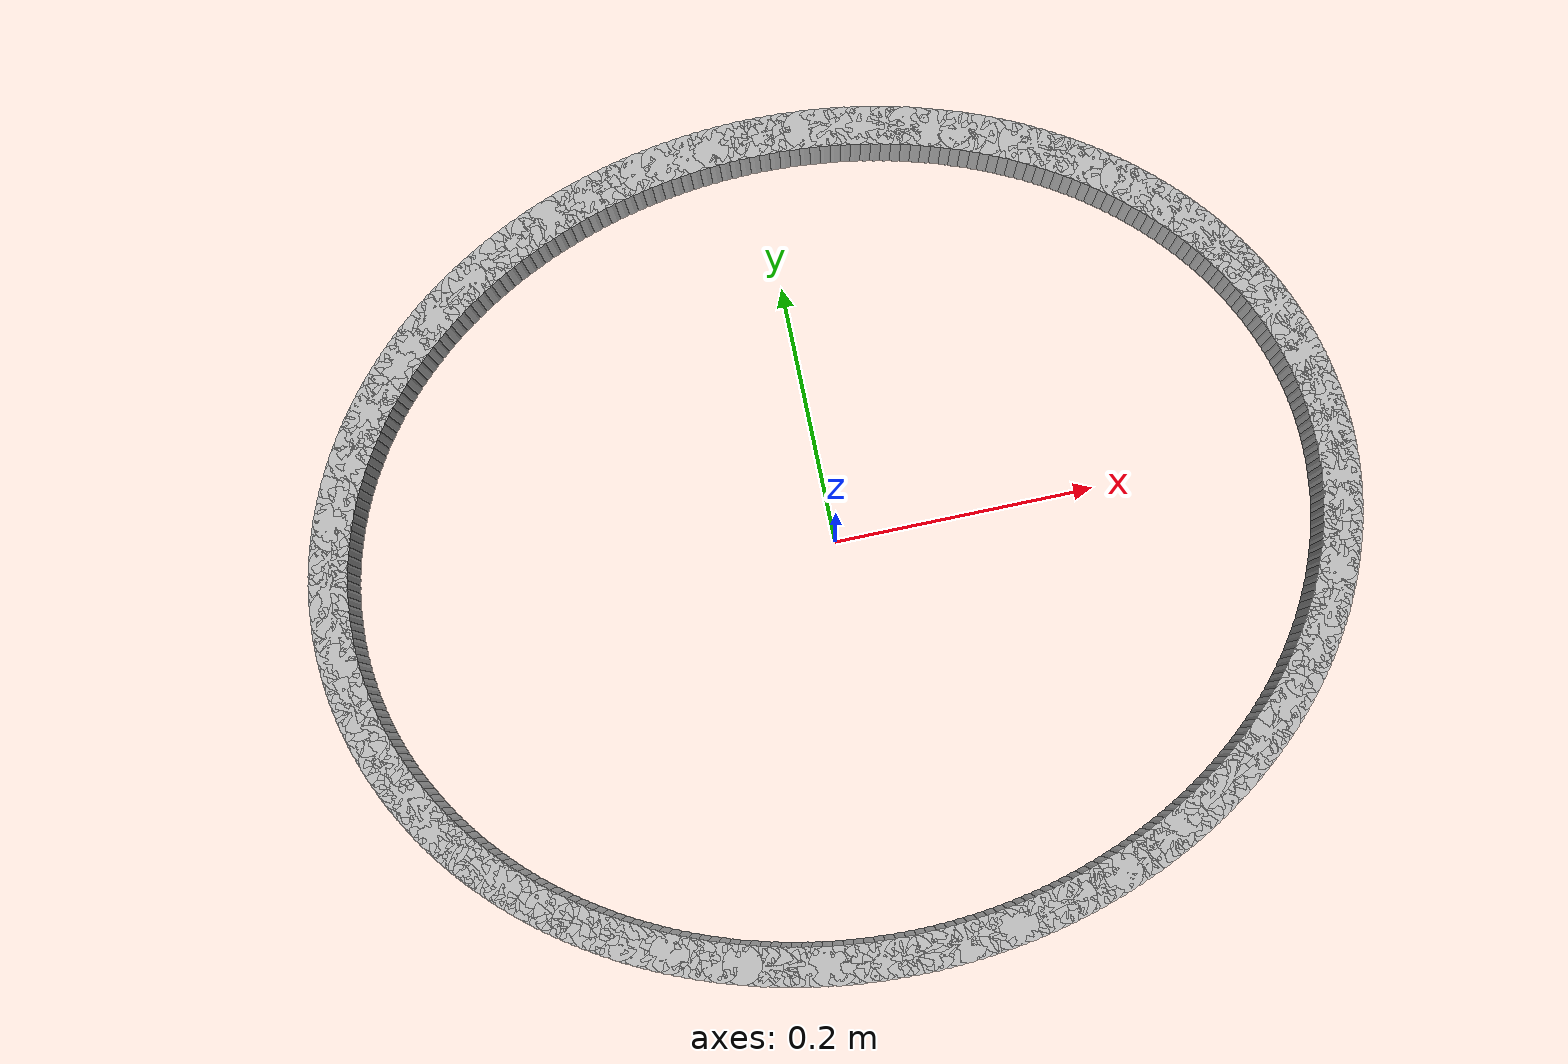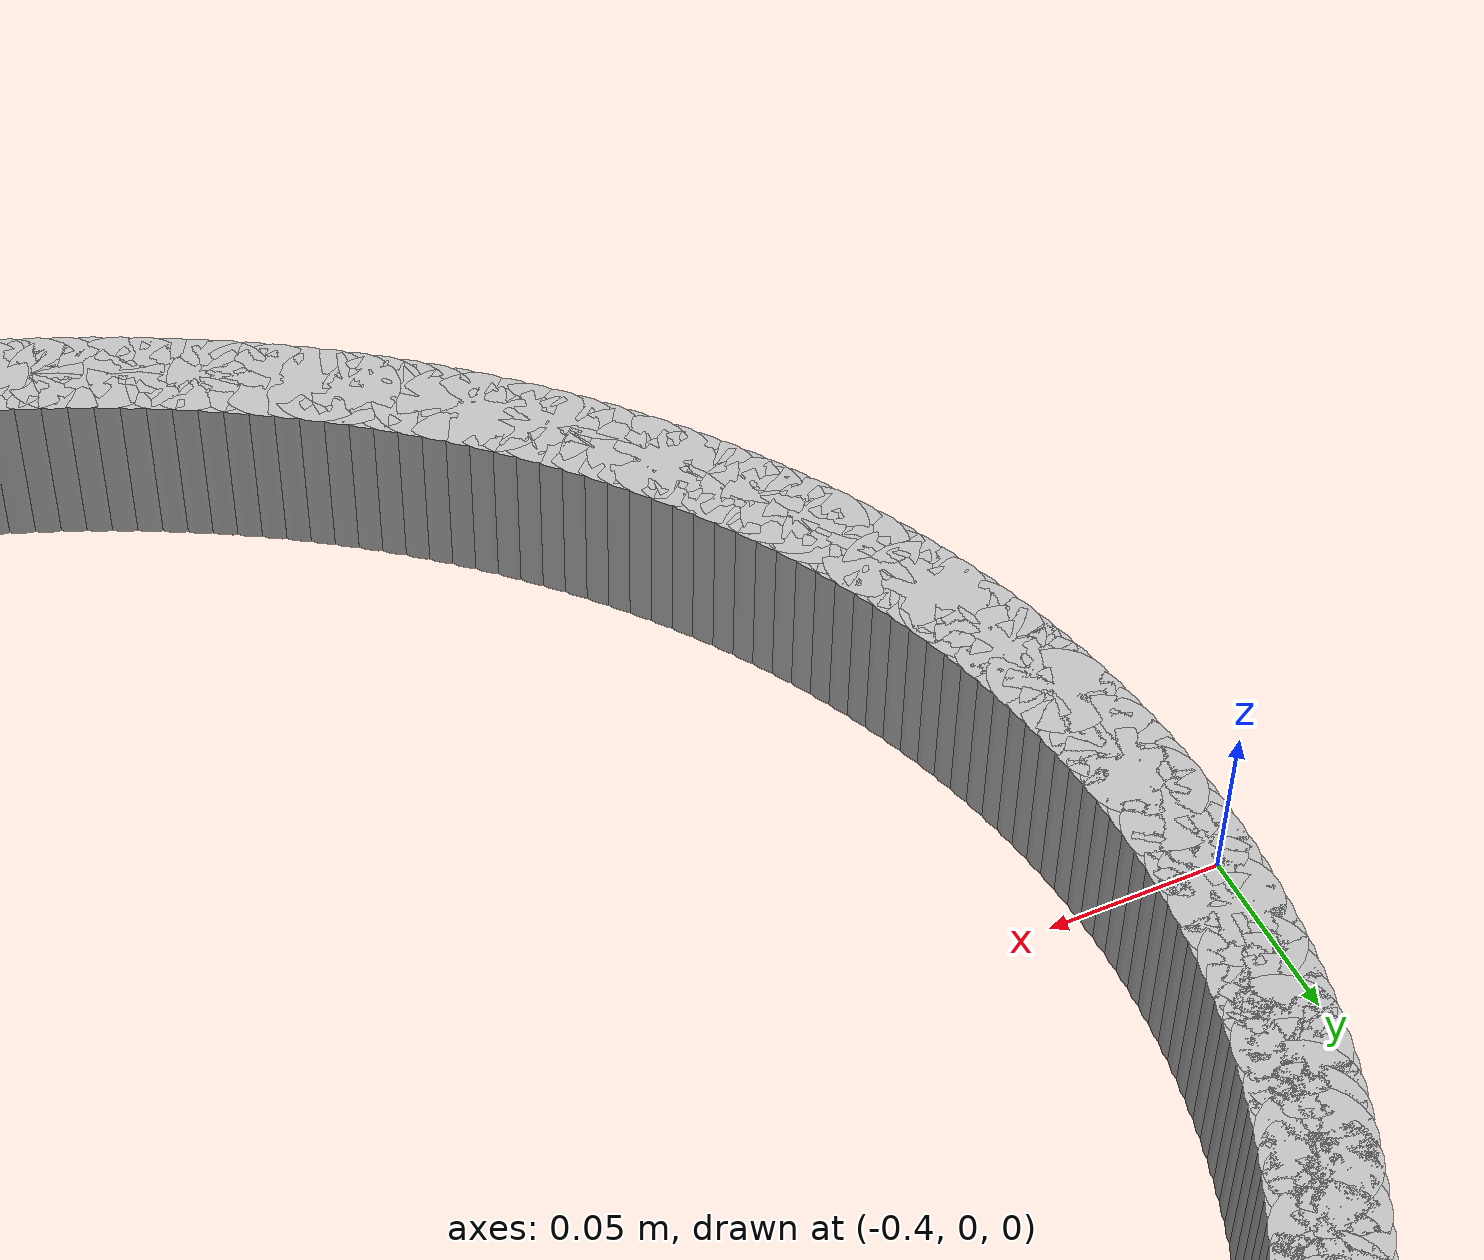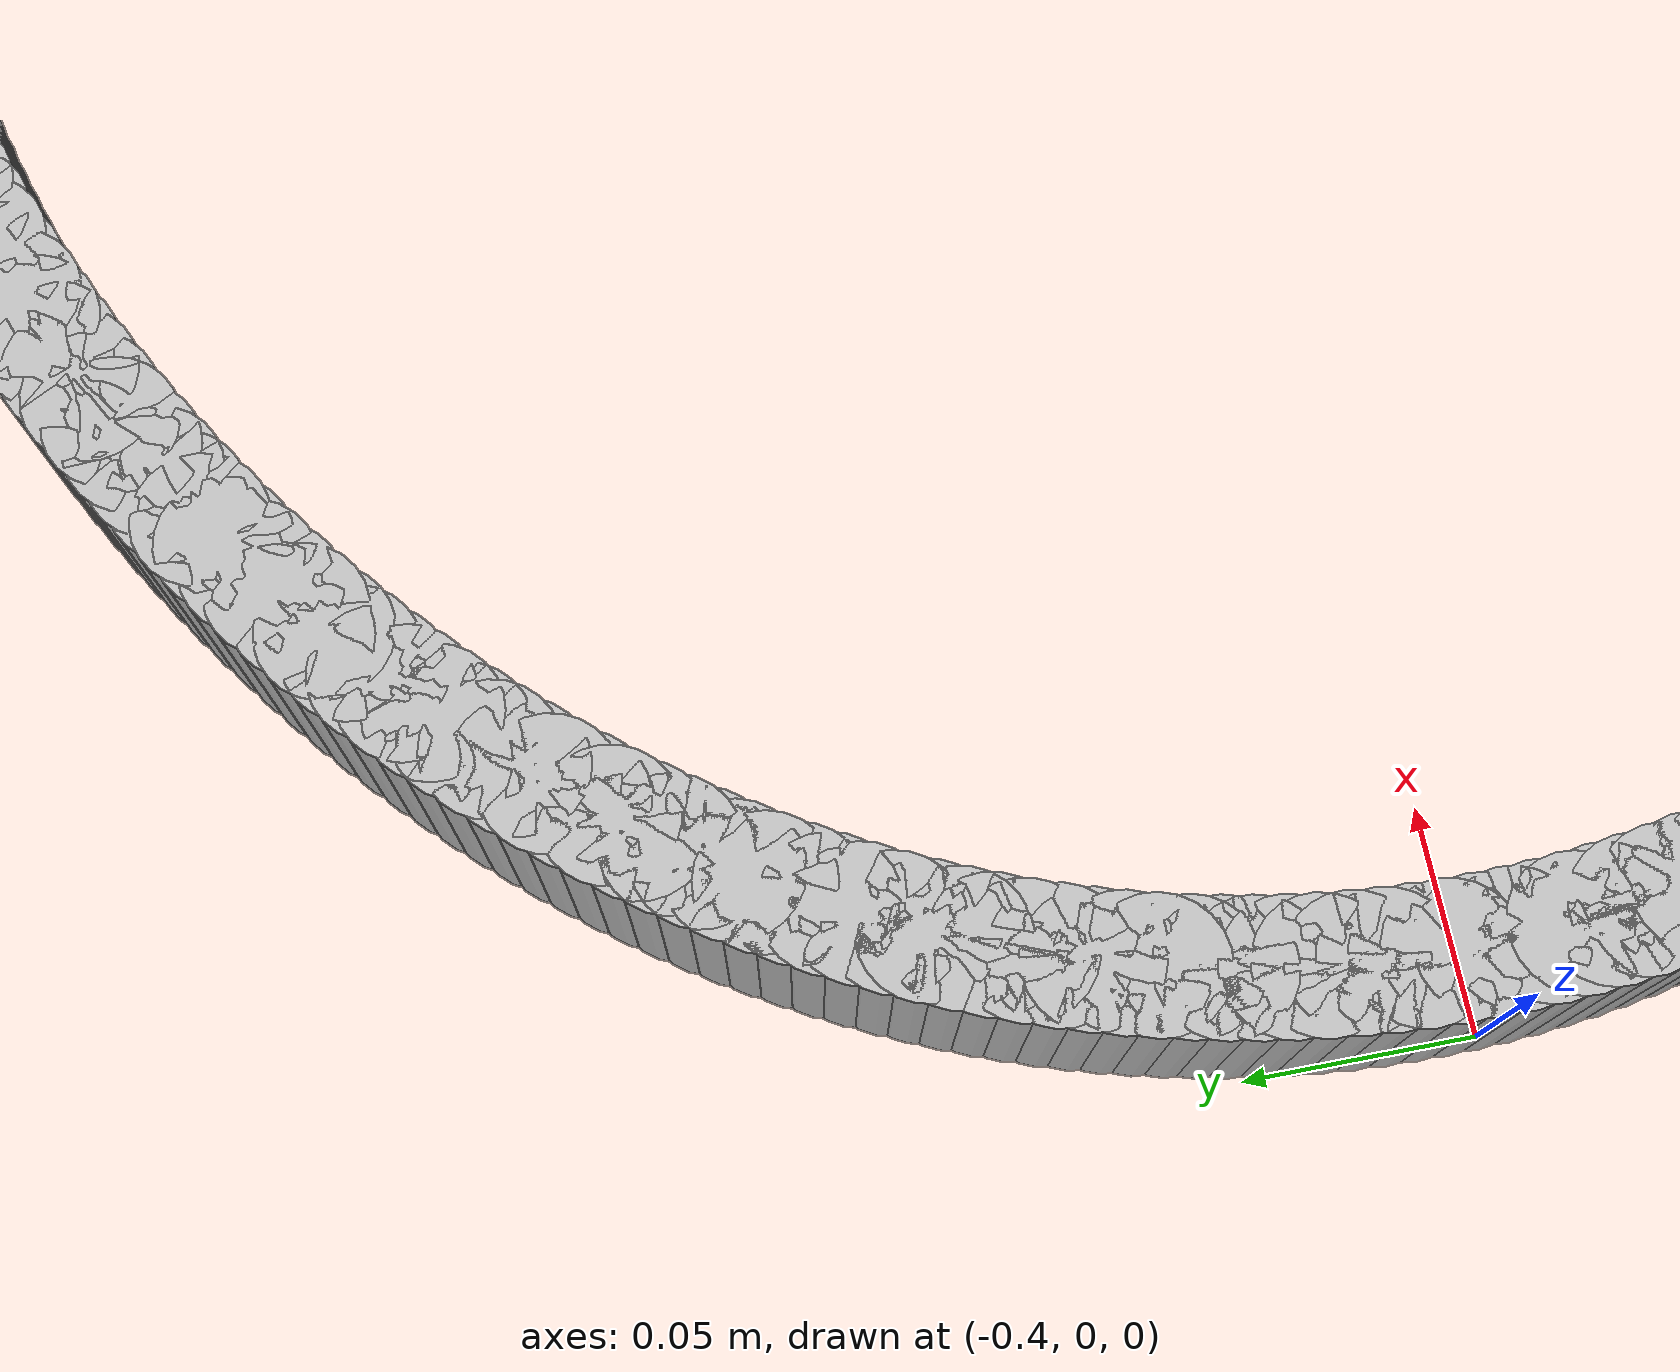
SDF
<?xml version='1.0'?>
<sdf version='1.6'>
    <model name='approximate_elliptical_ring'>
        <static>false</static>
        <link name='ring'>
            <inertial>
                <mass>1.0</mass>
                <inertia>
                    <ixx>0.1</ixx>
                    <iyy>0.1</iyy>
                    <izz>0.1</izz>
                </inertia>
            </inertial>
        </link>

        <link name='segment_0'>
            <pose>0.385 0.0 0 0 0 0.0</pose>
            <collision name='collision'>
                <geometry>
                    <cylinder>
                        <radius>0.015000000000000013</radius>
                        <length>0.05</length>
                    </cylinder>
                </geometry>
            </collision>
            <visual name='visual'>
                <geometry>
                    <cylinder>
                        <radius>0.015000000000000013</radius>
                        <length>0.05</length>
                    </cylinder>
                </geometry>
            </visual>
        </link>

        <link name='segment_1'>
            <pose>0.38491556313781555 0.006596862263257441 0 0 0 0.020943951023931952</pose>
            <collision name='collision'>
                <geometry>
                    <cylinder>
                        <radius>0.015000000000000013</radius>
                        <length>0.05</length>
                    </cylinder>
                </geometry>
            </collision>
            <visual name='visual'>
                <geometry>
                    <cylinder>
                        <radius>0.015000000000000013</radius>
                        <length>0.05</length>
                    </cylinder>
                </geometry>
            </visual>
        </link>

        <link name='segment_2'>
            <pose>0.3846622895880605 0.013190830924697881 0 0 0 0.041887902047863905</pose>
            <collision name='collision'>
                <geometry>
                    <cylinder>
                        <radius>0.015000000000000013</radius>
                        <length>0.05</length>
                    </cylinder>
                </geometry>
            </collision>
            <visual name='visual'>
                <geometry>
                    <cylinder>
                        <radius>0.015000000000000013</radius>
                        <length>0.05</length>
                    </cylinder>
                </geometry>
            </visual>
        </link>

        <link name='segment_3'>
            <pose>0.38424029044488456 0.01977901365173371 0 0 0 0.06283185307179585</pose>
            <collision name='collision'>
                <geometry>
                    <cylinder>
                        <radius>0.015000000000000013</radius>
                        <length>0.05</length>
                    </cylinder>
                </geometry>
            </collision>
            <visual name='visual'>
                <geometry>
                    <cylinder>
                        <radius>0.015000000000000013</radius>
                        <length>0.05</length>
                    </cylinder>
                </geometry>
            </visual>
        </link>

        <link name='segment_4'>
            <pose>0.3836497508110592 0.026358520649679376 0 0 0 0.08377580409572781</pose>
            <collision name='collision'>
                <geometry>
                    <cylinder>
                        <radius>0.015000000000000013</radius>
                        <length>0.05</length>
                    </cylinder>
                </geometry>
            </collision>
            <visual name='visual'>
                <geometry>
                    <cylinder>
                        <radius>0.015000000000000013</radius>
                        <length>0.05</length>
                    </cylinder>
                </geometry>
            </visual>
        </link>

        <link name='segment_5'>
            <pose>0.38289092971678523 0.032926465929310846 0 0 0 0.10471975511965978</pose>
            <collision name='collision'>
                <geometry>
                    <cylinder>
                        <radius>0.015000000000000013</radius>
                        <length>0.05</length>
                    </cylinder>
                </geometry>
            </collision>
            <visual name='visual'>
                <geometry>
                    <cylinder>
                        <radius>0.015000000000000013</radius>
                        <length>0.05</length>
                    </cylinder>
                </geometry>
            </visual>
        </link>

        <link name='segment_6'>
            <pose>0.38196416000607397 0.03947996857275583 0 0 0 0.1256637061435917</pose>
            <collision name='collision'>
                <geometry>
                    <cylinder>
                        <radius>0.015000000000000013</radius>
                        <length>0.05</length>
                    </cylinder>
                </geometry>
            </collision>
            <visual name='visual'>
                <geometry>
                    <cylinder>
                        <radius>0.015000000000000013</radius>
                        <length>0.05</length>
                    </cylinder>
                </geometry>
            </visual>
        </link>

        <link name='segment_7'>
            <pose>0.38086984819075054 0.04601615399715966 0 0 0 0.1466076571675237</pose>
            <collision name='collision'>
                <geometry>
                    <cylinder>
                        <radius>0.015000000000000013</radius>
                        <length>0.05</length>
                    </cylinder>
                </geometry>
            </collision>
            <visual name='visual'>
                <geometry>
                    <cylinder>
                        <radius>0.015000000000000013</radius>
                        <length>0.05</length>
                    </cylinder>
                </geometry>
            </visual>
        </link>

        <link name='segment_8'>
            <pose>0.37960847427214445 0.05253215521557221 0 0 0 0.16755160819145562</pose>
            <collision name='collision'>
                <geometry>
                    <cylinder>
                        <radius>0.015000000000000013</radius>
                        <length>0.05</length>
                    </cylinder>
                </geometry>
            </collision>
            <visual name='visual'>
                <geometry>
                    <cylinder>
                        <radius>0.015000000000000013</radius>
                        <length>0.05</length>
                    </cylinder>
                </geometry>
            </visual>
        </link>

        <link name='segment_9'>
            <pose>0.3781805915305452 0.05902511409450325 0 0 0 0.18849555921538758</pose>
            <collision name='collision'>
                <geometry>
                    <cylinder>
                        <radius>0.015000000000000013</radius>
                        <length>0.05</length>
                    </cylinder>
                </geometry>
            </collision>
            <visual name='visual'>
                <geometry>
                    <cylinder>
                        <radius>0.015000000000000013</radius>
                        <length>0.05</length>
                    </cylinder>
                </geometry>
            </visual>
        </link>

        <link name='segment_10'>
            <pose>0.3765868262825152 0.0654921826075942 0 0 0 0.20943951023931956</pose>
            <collision name='collision'>
                <geometry>
                    <cylinder>
                        <radius>0.015000000000000013</radius>
                        <length>0.05</length>
                    </cylinder>
                </geometry>
            </collision>
            <visual name='visual'>
                <geometry>
                    <cylinder>
                        <radius>0.015000000000000013</radius>
                        <length>0.05</length>
                    </cylinder>
                </geometry>
            </visual>
        </link>

        <link name='segment_11'>
            <pose>0.3748278776061667 0.07193052408485655 0 0 0 0.2303834612632515</pose>
            <collision name='collision'>
                <geometry>
                    <cylinder>
                        <radius>0.015000000000000013</radius>
                        <length>0.05</length>
                    </cylinder>
                </geometry>
            </collision>
            <visual name='visual'>
                <geometry>
                    <cylinder>
                        <radius>0.015000000000000013</radius>
                        <length>0.05</length>
                    </cylinder>
                </geometry>
            </visual>
        </link>

        <link name='segment_12'>
            <pose>0.372904517034523 0.07833731445692925 0 0 0 0.2513274122871834</pose>
            <collision name='collision'>
                <geometry>
                    <cylinder>
                        <radius>0.015000000000000013</radius>
                        <length>0.05</length>
                    </cylinder>
                </geometry>
            </collision>
            <visual name='visual'>
                <geometry>
                    <cylinder>
                        <radius>0.015000000000000013</radius>
                        <length>0.05</length>
                    </cylinder>
                </geometry>
            </visual>
        </link>

        <link name='segment_13'>
            <pose>0.3708175882170984 0.08470974349380869 0 0 0 0.2722713633111154</pose>
            <collision name='collision'>
                <geometry>
                    <cylinder>
                        <radius>0.015000000000000013</radius>
                        <length>0.05</length>
                    </cylinder>
                </geometry>
            </collision>
            <visual name='visual'>
                <geometry>
                    <cylinder>
                        <radius>0.015000000000000013</radius>
                        <length>0.05</length>
                    </cylinder>
                </geometry>
            </visual>
        </link>

        <link name='segment_14'>
            <pose>0.3685680065498459 0.09104501603750856 0 0 0 0.2932153143350474</pose>
            <collision name='collision'>
                <geometry>
                    <cylinder>
                        <radius>0.015000000000000013</radius>
                        <length>0.05</length>
                    </cylinder>
                </geometry>
            </collision>
            <visual name='visual'>
                <geometry>
                    <cylinder>
                        <radius>0.015000000000000013</radius>
                        <length>0.05</length>
                    </cylinder>
                </geometry>
            </visual>
        </link>

        <link name='segment_15'>
            <pose>0.36615675877363413 0.09734035322810843 0 0 0 0.3141592653589793</pose>
            <collision name='collision'>
                <geometry>
                    <cylinder>
                        <radius>0.015000000000000013</radius>
                        <length>0.05</length>
                    </cylinder>
                </geometry>
            </collision>
            <visual name='visual'>
                <geometry>
                    <cylinder>
                        <radius>0.015000000000000013</radius>
                        <length>0.05</length>
                    </cylinder>
                </geometry>
            </visual>
        </link>

        <link name='segment_16'>
            <pose>0.3635849025414302 0.10359299372265372 0 0 0 0.33510321638291124</pose>
            <collision name='collision'>
                <geometry>
                    <cylinder>
                        <radius>0.015000000000000013</radius>
                        <length>0.05</length>
                    </cylinder>
                </geometry>
            </collision>
            <visual name='visual'>
                <geometry>
                    <cylinder>
                        <radius>0.015000000000000013</radius>
                        <length>0.05</length>
                    </cylinder>
                </geometry>
            </visual>
        </link>

        <link name='segment_17'>
            <pose>0.36085356595437823 0.10980019490637179 0 0 0 0.3560471674068432</pose>
            <collision name='collision'>
                <geometry>
                    <cylinder>
                        <radius>0.015000000000000013</radius>
                        <length>0.05</length>
                    </cylinder>
                </geometry>
            </collision>
            <visual name='visual'>
                <geometry>
                    <cylinder>
                        <radius>0.015000000000000013</radius>
                        <length>0.05</length>
                    </cylinder>
                </geometry>
            </visual>
        </link>

        <link name='segment_18'>
            <pose>0.3579639470669768 0.11595923409567355 0 0 0 0.37699111843077515</pose>
            <collision name='collision'>
                <geometry>
                    <cylinder>
                        <radius>0.015000000000000013</radius>
                        <length>0.05</length>
                    </cylinder>
                </geometry>
            </collision>
            <visual name='visual'>
                <geometry>
                    <cylinder>
                        <radius>0.015000000000000013</radius>
                        <length>0.05</length>
                    </cylinder>
                </geometry>
            </visual>
        </link>

        <link name='segment_19'>
            <pose>0.35491731336157273 0.12206740973241244 0 0 0 0.39793506945470714</pose>
            <collision name='collision'>
                <geometry>
                    <cylinder>
                        <radius>0.015000000000000013</radius>
                        <length>0.05</length>
                    </cylinder>
                </geometry>
            </collision>
            <visual name='visual'>
                <geometry>
                    <cylinder>
                        <radius>0.015000000000000013</radius>
                        <length>0.05</length>
                    </cylinder>
                </geometry>
            </visual>
        </link>

        <link name='segment_20'>
            <pose>0.35171500119240134 0.12812204256887708 0 0 0 0.4188790204786391</pose>
            <collision name='collision'>
                <geometry>
                    <cylinder>
                        <radius>0.015000000000000013</radius>
                        <length>0.05</length>
                    </cylinder>
                </geometry>
            </collision>
            <visual name='visual'>
                <geometry>
                    <cylinder>
                        <radius>0.015000000000000013</radius>
                        <length>0.05</length>
                    </cylinder>
                </geometry>
            </visual>
        </link>

        <link name='segment_21'>
            <pose>0.34835841519941757 0.13412047684299788 0 0 0 0.43982297150257105</pose>
            <collision name='collision'>
                <geometry>
                    <cylinder>
                        <radius>0.015000000000000013</radius>
                        <length>0.05</length>
                    </cylinder>
                </geometry>
            </collision>
            <visual name='visual'>
                <geometry>
                    <cylinder>
                        <radius>0.015000000000000013</radius>
                        <length>0.05</length>
                    </cylinder>
                </geometry>
            </visual>
        </link>

        <link name='segment_22'>
            <pose>0.34484902769217396 0.14006008144325216 0 0 0 0.460766922526503</pose>
            <collision name='collision'>
                <geometry>
                    <cylinder>
                        <radius>0.015000000000000013</radius>
                        <length>0.05</length>
                    </cylinder>
                </geometry>
            </collision>
            <visual name='visual'>
                <geometry>
                    <cylinder>
                        <radius>0.015000000000000013</radius>
                        <length>0.05</length>
                    </cylinder>
                </geometry>
            </visual>
        </link>

        <link name='segment_23'>
            <pose>0.3411883780040177 0.14593825106275643 0 0 0 0.4817108735504349</pose>
            <collision name='collision'>
                <geometry>
                    <cylinder>
                        <radius>0.015000000000000013</radius>
                        <length>0.05</length>
                    </cylinder>
                </geometry>
            </collision>
            <visual name='visual'>
                <geometry>
                    <cylinder>
                        <radius>0.015000000000000013</radius>
                        <length>0.05</length>
                    </cylinder>
                </geometry>
            </visual>
        </link>

        <link name='segment_24'>
            <pose>0.3373780718168875 0.1517524073420403 0 0 0 0.5026548245743668</pose>
            <collision name='collision'>
                <geometry>
                    <cylinder>
                        <radius>0.015000000000000013</radius>
                        <length>0.05</length>
                    </cylinder>
                </geometry>
            </collision>
            <visual name='visual'>
                <geometry>
                    <cylinder>
                        <radius>0.015000000000000013</radius>
                        <length>0.05</length>
                    </cylinder>
                </geometry>
            </visual>
        </link>

        <link name='segment_25'>
            <pose>0.33341978045700893 0.15749999999999997 0 0 0 0.5235987755982988</pose>
            <collision name='collision'>
                <geometry>
                    <cylinder>
                        <radius>0.015000000000000013</radius>
                        <length>0.05</length>
                    </cylinder>
                </geometry>
            </collision>
            <visual name='visual'>
                <geometry>
                    <cylinder>
                        <radius>0.015000000000000013</radius>
                        <length>0.05</length>
                    </cylinder>
                </geometry>
            </visual>
        </link>

        <link name='segment_26'>
            <pose>0.32931524016179503 0.163178507952536 0 0 0 0.5445427266222308</pose>
            <collision name='collision'>
                <geometry>
                    <cylinder>
                        <radius>0.015000000000000013</radius>
                        <length>0.05</length>
                    </cylinder>
                </geometry>
            </collision>
            <visual name='visual'>
                <geometry>
                    <cylinder>
                        <radius>0.015000000000000013</radius>
                        <length>0.05</length>
                    </cylinder>
                </geometry>
            </visual>
        </link>

        <link name='segment_27'>
            <pose>0.3250662513182758 0.16878544041838395 0 0 0 0.5654866776461628</pose>
            <collision name='collision'>
                <geometry>
                    <cylinder>
                        <radius>0.015000000000000013</radius>
                        <length>0.05</length>
                    </cylinder>
                </geometry>
            </collision>
            <visual name='visual'>
                <geometry>
                    <cylinder>
                        <radius>0.015000000000000013</radius>
                        <length>0.05</length>
                    </cylinder>
                </geometry>
            </visual>
        </link>

        <link name='segment_28'>
            <pose>0.3206746776733883 0.1743183380116534 0 0 0 0.5864306286700948</pose>
            <collision name='collision'>
                <geometry>
                    <cylinder>
                        <radius>0.015000000000000013</radius>
                        <length>0.05</length>
                    </cylinder>
                </geometry>
            </collision>
            <visual name='visual'>
                <geometry>
                    <cylinder>
                        <radius>0.015000000000000013</radius>
                        <length>0.05</length>
                    </cylinder>
                </geometry>
            </visual>
        </link>

        <link name='segment_29'>
            <pose>0.3161424455164761 0.17977477382059595 0 0 0 0.6073745796940266</pose>
            <collision name='collision'>
                <geometry>
                    <cylinder>
                        <radius>0.015000000000000013</radius>
                        <length>0.05</length>
                    </cylinder>
                </geometry>
            </collision>
            <visual name='visual'>
                <geometry>
                    <cylinder>
                        <radius>0.015000000000000013</radius>
                        <length>0.05</length>
                    </cylinder>
                </geometry>
            </visual>
        </link>

        <link name='segment_30'>
            <pose>0.3114715428343548 0.18515235447212905 0 0 0 0.6283185307179586</pose>
            <collision name='collision'>
                <geometry>
                    <cylinder>
                        <radius>0.015000000000000013</radius>
                        <length>0.05</length>
                    </cylinder>
                </geometry>
            </collision>
            <visual name='visual'>
                <geometry>
                    <cylinder>
                        <radius>0.015000000000000013</radius>
                        <length>0.05</length>
                    </cylinder>
                </geometry>
            </visual>
        </link>

        <link name='segment_31'>
            <pose>0.3066640184393156 0.19044872118164805 0 0 0 0.6492624817418905</pose>
            <collision name='collision'>
                <geometry>
                    <cylinder>
                        <radius>0.015000000000000013</radius>
                        <length>0.05</length>
                    </cylinder>
                </geometry>
            </collision>
            <visual name='visual'>
                <geometry>
                    <cylinder>
                        <radius>0.015000000000000013</radius>
                        <length>0.05</length>
                    </cylinder>
                </geometry>
            </visual>
        </link>

        <link name='segment_32'>
            <pose>0.30172198107044834 0.19566155078766775 0 0 0 0.6702064327658225</pose>
            <collision name='collision'>
                <geometry>
                    <cylinder>
                        <radius>0.015000000000000013</radius>
                        <length>0.05</length>
                    </cylinder>
                </geometry>
            </collision>
            <visual name='visual'>
                <geometry>
                    <cylinder>
                        <radius>0.015000000000000013</radius>
                        <length>0.05</length>
                    </cylinder>
                </geometry>
            </visual>
        </link>

        <link name='segment_33'>
            <pose>0.29664759846867883 0.20078855677083726 0 0 0 0.6911503837897546</pose>
            <collision name='collision'>
                <geometry>
                    <cylinder>
                        <radius>0.015000000000000013</radius>
                        <length>0.05</length>
                    </cylinder>
                </geometry>
            </collision>
            <visual name='visual'>
                <geometry>
                    <cylinder>
                        <radius>0.015000000000000013</radius>
                        <length>0.05</length>
                    </cylinder>
                </geometry>
            </visual>
        </link>

        <link name='segment_34'>
            <pose>0.2914430964259262 0.20582749025688318 0 0 0 0.7120943348136864</pose>
            <collision name='collision'>
                <geometry>
                    <cylinder>
                        <radius>0.015000000000000013</radius>
                        <length>0.05</length>
                    </cylinder>
                </geometry>
            </collision>
            <visual name='visual'>
                <geometry>
                    <cylinder>
                        <radius>0.015000000000000013</radius>
                        <length>0.05</length>
                    </cylinder>
                </geometry>
            </visual>
        </link>

        <link name='segment_35'>
            <pose>0.2861107578087968 0.21077614100304035 0 0 0 0.7330382858376184</pose>
            <collision name='collision'>
                <geometry>
                    <cylinder>
                        <radius>0.015000000000000013</radius>
                        <length>0.05</length>
                    </cylinder>
                </geometry>
            </collision>
            <visual name='visual'>
                <geometry>
                    <cylinder>
                        <radius>0.015000000000000013</radius>
                        <length>0.05</length>
                    </cylinder>
                </geometry>
            </visual>
        </link>

        <link name='segment_36'>
            <pose>0.2806529215572435 0.21563233836753692 0 0 0 0.7539822368615503</pose>
            <collision name='collision'>
                <geometry>
                    <cylinder>
                        <radius>0.015000000000000013</radius>
                        <length>0.05</length>
                    </cylinder>
                </geometry>
            </collision>
            <visual name='visual'>
                <geometry>
                    <cylinder>
                        <radius>0.015000000000000013</radius>
                        <length>0.05</length>
                    </cylinder>
                </geometry>
            </visual>
        </link>

        <link name='segment_37'>
            <pose>0.2750719816586293 0.2203939522617101 0 0 0 0.7749261878854823</pose>
            <collision name='collision'>
                <geometry>
                    <cylinder>
                        <radius>0.015000000000000013</radius>
                        <length>0.05</length>
                    </cylinder>
                </geometry>
            </collision>
            <visual name='visual'>
                <geometry>
                    <cylinder>
                        <radius>0.015000000000000013</radius>
                        <length>0.05</length>
                    </cylinder>
                </geometry>
            </visual>
        </link>

        <link name='segment_38'>
            <pose>0.2693703860976457 0.22505889408433305 0 0 0 0.7958701389094143</pose>
            <collision name='collision'>
                <geometry>
                    <cylinder>
                        <radius>0.015000000000000013</radius>
                        <length>0.05</length>
                    </cylinder>
                </geometry>
            </collision>
            <visual name='visual'>
                <geometry>
                    <cylinder>
                        <radius>0.015000000000000013</radius>
                        <length>0.05</length>
                    </cylinder>
                </geometry>
            </visual>
        </link>

        <link name='segment_39'>
            <pose>0.2635506357825452 0.2296251176377446 0 0 0 0.8168140899333461</pose>
            <collision name='collision'>
                <geometry>
                    <cylinder>
                        <radius>0.015000000000000013</radius>
                        <length>0.05</length>
                    </cylinder>
                </geometry>
            </collision>
            <visual name='visual'>
                <geometry>
                    <cylinder>
                        <radius>0.015000000000000013</radius>
                        <length>0.05</length>
                    </cylinder>
                </geometry>
            </visual>
        </link>

        <link name='segment_40'>
            <pose>0.2576152834481604 0.2340906200253792 0 0 0 0.8377580409572782</pose>
            <collision name='collision'>
                <geometry>
                    <cylinder>
                        <radius>0.015000000000000013</radius>
                        <length>0.05</length>
                    </cylinder>
                </geometry>
            </collision>
            <visual name='visual'>
                <geometry>
                    <cylinder>
                        <radius>0.015000000000000013</radius>
                        <length>0.05</length>
                    </cylinder>
                </geometry>
            </visual>
        </link>

        <link name='segment_41'>
            <pose>0.2515669325361906 0.23845344253030326 0 0 0 0.8587019919812101</pose>
            <collision name='collision'>
                <geometry>
                    <cylinder>
                        <radius>0.015000000000000013</radius>
                        <length>0.05</length>
                    </cylinder>
                </geometry>
            </collision>
            <visual name='visual'>
                <geometry>
                    <cylinder>
                        <radius>0.015000000000000013</radius>
                        <length>0.05</length>
                    </cylinder>
                </geometry>
            </visual>
        </link>

        <link name='segment_42'>
            <pose>0.24540823605324555 0.2427116714743736 0 0 0 0.8796459430051421</pose>
            <collision name='collision'>
                <geometry>
                    <cylinder>
                        <radius>0.015000000000000013</radius>
                        <length>0.05</length>
                    </cylinder>
                </geometry>
            </collision>
            <visual name='visual'>
                <geometry>
                    <cylinder>
                        <radius>0.015000000000000013</radius>
                        <length>0.05</length>
                    </cylinder>
                </geometry>
            </visual>
        </link>

        <link name='segment_43'>
            <pose>0.23914189540714947 0.24686343905763955 0 0 0 0.9005898940290741</pose>
            <collision name='collision'>
                <geometry>
                    <cylinder>
                        <radius>0.015000000000000013</radius>
                        <length>0.05</length>
                    </cylinder>
                </geometry>
            </collision>
            <visual name='visual'>
                <geometry>
                    <cylinder>
                        <radius>0.015000000000000013</radius>
                        <length>0.05</length>
                    </cylinder>
                </geometry>
            </visual>
        </link>

        <link name='segment_44'>
            <pose>0.23277065922201437 0.25090692417762184 0 0 0 0.921533845053006</pose>
            <collision name='collision'>
                <geometry>
                    <cylinder>
                        <radius>0.015000000000000013</radius>
                        <length>0.05</length>
                    </cylinder>
                </geometry>
            </collision>
            <visual name='visual'>
                <geometry>
                    <cylinder>
                        <radius>0.015000000000000013</radius>
                        <length>0.05</length>
                    </cylinder>
                </geometry>
            </visual>
        </link>

        <link name='segment_45'>
            <pose>0.22629732213260217 0.25484035322810844 0 0 0 0.9424777960769379</pose>
            <collision name='collision'>
                <geometry>
                    <cylinder>
                        <radius>0.015000000000000013</radius>
                        <length>0.05</length>
                    </cylinder>
                </geometry>
            </collision>
            <visual name='visual'>
                <geometry>
                    <cylinder>
                        <radius>0.015000000000000013</radius>
                        <length>0.05</length>
                    </cylinder>
                </geometry>
            </visual>
        </link>

        <link name='segment_46'>
            <pose>0.21972472355850625 0.2586620008771167 0 0 0 0.9634217471008698</pose>
            <collision name='collision'>
                <geometry>
                    <cylinder>
                        <radius>0.015000000000000013</radius>
                        <length>0.05</length>
                    </cylinder>
                </geometry>
            </collision>
            <visual name='visual'>
                <geometry>
                    <cylinder>
                        <radius>0.015000000000000013</radius>
                        <length>0.05</length>
                    </cylinder>
                </geometry>
            </visual>
        </link>

        <link name='segment_47'>
            <pose>0.2130557464586875 0.26237019082368135 0 0 0 0.9843656981248018</pose>
            <collision name='collision'>
                <geometry>
                    <cylinder>
                        <radius>0.015000000000000013</radius>
                        <length>0.05</length>
                    </cylinder>
                </geometry>
            </collision>
            <visual name='visual'>
                <geometry>
                    <cylinder>
                        <radius>0.015000000000000013</radius>
                        <length>0.05</length>
                    </cylinder>
                </geometry>
            </visual>
        </link>

        <link name='segment_48'>
            <pose>0.20629331606691376 0.2659632965331347 0 0 0 1.0053096491487337</pose>
            <collision name='collision'>
                <geometry>
                    <cylinder>
                        <radius>0.015000000000000013</radius>
                        <length>0.05</length>
                    </cylinder>
                </geometry>
            </collision>
            <visual name='visual'>
                <geometry>
                    <cylinder>
                        <radius>0.015000000000000013</radius>
                        <length>0.05</length>
                    </cylinder>
                </geometry>
            </visual>
        </link>

        <link name='segment_49'>
            <pose>0.19944039860865517 0.2694397419505596 0 0 0 1.0262536001726656</pose>
            <collision name='collision'>
                <geometry>
                    <cylinder>
                        <radius>0.015000000000000013</radius>
                        <length>0.05</length>
                    </cylinder>
                </geometry>
            </collision>
            <visual name='visual'>
                <geometry>
                    <cylinder>
                        <radius>0.015000000000000013</radius>
                        <length>0.05</length>
                    </cylinder>
                </geometry>
            </visual>
        </link>

        <link name='segment_50'>
            <pose>0.19250000000000006 0.27279800219209815 0 0 0 1.0471975511965976</pose>
            <collision name='collision'>
                <geometry>
                    <cylinder>
                        <radius>0.015000000000000013</radius>
                        <length>0.05</length>
                    </cylinder>
                </geometry>
            </collision>
            <visual name='visual'>
                <geometry>
                    <cylinder>
                        <radius>0.015000000000000013</radius>
                        <length>0.05</length>
                    </cylinder>
                </geometry>
            </visual>
        </link>

        <link name='segment_51'>
            <pose>0.1854751645291604 0.27603660421381704 0 0 0 1.0681415022205296</pose>
            <collision name='collision'>
                <geometry>
                    <cylinder>
                        <radius>0.015000000000000013</radius>
                        <length>0.05</length>
                    </cylinder>
                </geometry>
            </collision>
            <visual name='visual'>
                <geometry>
                    <cylinder>
                        <radius>0.015000000000000013</radius>
                        <length>0.05</length>
                    </cylinder>
                </geometry>
            </visual>
        </link>

        <link name='segment_52'>
            <pose>0.17836897352114678 0.27915412745783263 0 0 0 1.0890854532444616</pose>
            <collision name='collision'>
                <geometry>
                    <cylinder>
                        <radius>0.015000000000000013</radius>
                        <length>0.05</length>
                    </cylinder>
                </geometry>
            </collision>
            <visual name='visual'>
                <geometry>
                    <cylinder>
                        <radius>0.015000000000000013</radius>
                        <length>0.05</length>
                    </cylinder>
                </geometry>
            </visual>
        </link>

        <link name='segment_53'>
            <pose>0.1711845439861971 0.2821492044754151 0 0 0 1.1100294042683936</pose>
            <collision name='collision'>
                <geometry>
                    <cylinder>
                        <radius>0.015000000000000013</radius>
                        <length>0.05</length>
                    </cylinder>
                </geometry>
            </collision>
            <visual name='visual'>
                <geometry>
                    <cylinder>
                        <radius>0.015000000000000013</radius>
                        <length>0.05</length>
                    </cylinder>
                </geometry>
            </visual>
        </link>

        <link name='segment_54'>
            <pose>0.16392502725255298 0.2850205215267962 0 0 0 1.1309733552923256</pose>
            <collision name='collision'>
                <geometry>
                    <cylinder>
                        <radius>0.015000000000000013</radius>
                        <length>0.05</length>
                    </cylinder>
                </geometry>
            </collision>
            <visual name='visual'>
                <geometry>
                    <cylinder>
                        <radius>0.015000000000000013</radius>
                        <length>0.05</length>
                    </cylinder>
                </geometry>
            </visual>
        </link>

        <link name='segment_55'>
            <pose>0.1565936075841831 0.28776681915741925 0 0 0 1.1519173063162575</pose>
            <collision name='collision'>
                <geometry>
                    <cylinder>
                        <radius>0.015000000000000013</radius>
                        <length>0.05</length>
                    </cylinder>
                </geometry>
            </collision>
            <visual name='visual'>
                <geometry>
                    <cylinder>
                        <radius>0.015000000000000013</radius>
                        <length>0.05</length>
                    </cylinder>
                </geometry>
            </visual>
        </link>

        <link name='segment_56'>
            <pose>0.14919350078405963 0.29038689275037766 0 0 0 1.1728612573401895</pose>
            <collision name='collision'>
                <geometry>
                    <cylinder>
                        <radius>0.015000000000000013</radius>
                        <length>0.05</length>
                    </cylinder>
                </geometry>
            </collision>
            <visual name='visual'>
                <geometry>
                    <cylinder>
                        <radius>0.015000000000000013</radius>
                        <length>0.05</length>
                    </cylinder>
                </geometry>
            </visual>
        </link>

        <link name='segment_57'>
            <pose>0.14172795278360106 0.29287959305479916 0 0 0 1.1938052083641213</pose>
            <collision name='collision'>
                <geometry>
                    <cylinder>
                        <radius>0.015000000000000013</radius>
                        <length>0.05</length>
                    </cylinder>
                </geometry>
            </collision>
            <visual name='visual'>
                <geometry>
                    <cylinder>
                        <radius>0.015000000000000013</radius>
                        <length>0.05</length>
                    </cylinder>
                </geometry>
            </visual>
        </link>

        <link name='segment_58'>
            <pose>0.1342002382188989 0.2952438266899458 0 0 0 1.2147491593880533</pose>
            <collision name='collision'>
                <geometry>
                    <cylinder>
                        <radius>0.015000000000000013</radius>
                        <length>0.05</length>
                    </cylinder>
                </geometry>
            </collision>
            <visual name='visual'>
                <geometry>
                    <cylinder>
                        <radius>0.015000000000000013</radius>
                        <length>0.05</length>
                    </cylinder>
                </geometry>
            </visual>
        </link>

        <link name='segment_59'>
            <pose>0.12661365899435456 0.2974785566248065 0 0 0 1.2356931104119853</pose>
            <collision name='collision'>
                <geometry>
                    <cylinder>
                        <radius>0.015000000000000013</radius>
                        <length>0.05</length>
                    </cylinder>
                </geometry>
            </collision>
            <visual name='visual'>
                <geometry>
                    <cylinder>
                        <radius>0.015000000000000013</radius>
                        <length>0.05</length>
                    </cylinder>
                </geometry>
            </visual>
        </link>

        <link name='segment_60'>
            <pose>0.11897154283435477 0.2995828026329734 0 0 0 1.2566370614359172</pose>
            <collision name='collision'>
                <geometry>
                    <cylinder>
                        <radius>0.015000000000000013</radius>
                        <length>0.05</length>
                    </cylinder>
                </geometry>
            </collision>
            <visual name='visual'>
                <geometry>
                    <cylinder>
                        <radius>0.015000000000000013</radius>
                        <length>0.05</length>
                    </cylinder>
                </geometry>
            </visual>
        </link>

        <link name='segment_61'>
            <pose>0.11127724182362157 0.3015556417226012 0 0 0 1.2775810124598492</pose>
            <collision name='collision'>
                <geometry>
                    <cylinder>
                        <radius>0.015000000000000013</radius>
                        <length>0.05</length>
                    </cylinder>
                </geometry>
            </collision>
            <visual name='visual'>
                <geometry>
                    <cylinder>
                        <radius>0.015000000000000013</radius>
                        <length>0.05</length>
                    </cylinder>
                </geometry>
            </visual>
        </link>

        <link name='segment_62'>
            <pose>0.10353413093687738 0.3033962085412623 0 0 0 1.298524963483781</pose>
            <collision name='collision'>
                <geometry>
                    <cylinder>
                        <radius>0.015000000000000013</radius>
                        <length>0.05</length>
                    </cylinder>
                </geometry>
            </collision>
            <visual name='visual'>
                <geometry>
                    <cylinder>
                        <radius>0.015000000000000013</radius>
                        <length>0.05</length>
                    </cylinder>
                </geometry>
            </visual>
        </link>

        <link name='segment_63'>
            <pose>0.09574560655846916 0.30510369575551877 0 0 0 1.319468914507713</pose>
            <collision name='collision'>
                <geometry>
                    <cylinder>
                        <radius>0.015000000000000013</radius>
                        <length>0.05</length>
                    </cylinder>
                </geometry>
            </collision>
            <visual name='visual'>
                <geometry>
                    <cylinder>
                        <radius>0.015000000000000013</radius>
                        <length>0.05</length>
                    </cylinder>
                </geometry>
            </visual>
        </link>

        <link name='segment_64'>
            <pose>0.08791508499260252 0.30667735440504545 0 0 0 1.340412865531645</pose>
            <collision name='collision'>
                <geometry>
                    <cylinder>
                        <radius>0.015000000000000013</radius>
                        <length>0.05</length>
                    </cylinder>
                </geometry>
            </collision>
            <visual name='visual'>
                <geometry>
                    <cylinder>
                        <radius>0.015000000000000013</radius>
                        <length>0.05</length>
                    </cylinder>
                </geometry>
            </visual>
        </link>

        <link name='segment_65'>
            <pose>0.0800460009648374 0.3081164942311488 0 0 0 1.361356816555577</pose>
            <collision name='collision'>
                <geometry>
                    <cylinder>
                        <radius>0.015000000000000013</radius>
                        <length>0.05</length>
                    </cylinder>
                </geometry>
            </collision>
            <visual name='visual'>
                <geometry>
                    <cylinder>
                        <radius>0.015000000000000013</radius>
                        <length>0.05</length>
                    </cylinder>
                </geometry>
            </visual>
        </link>

        <link name='segment_66'>
            <pose>0.07214180611550394 0.309420483979537 0 0 0 1.3823007675795091</pose>
            <collision name='collision'>
                <geometry>
                    <cylinder>
                        <radius>0.015000000000000013</radius>
                        <length>0.05</length>
                    </cylinder>
                </geometry>
            </collision>
            <visual name='visual'>
                <geometry>
                    <cylinder>
                        <radius>0.015000000000000013</radius>
                        <length>0.05</length>
                    </cylinder>
                </geometry>
            </visual>
        </link>

        <link name='segment_67'>
            <pose>0.0642059674856994 0.31058875167720906 0 0 0 1.403244718603441</pose>
            <collision name='collision'>
                <geometry>
                    <cylinder>
                        <radius>0.015000000000000013</radius>
                        <length>0.05</length>
                    </cylinder>
                </geometry>
            </collision>
            <visual name='visual'>
                <geometry>
                    <cylinder>
                        <radius>0.015000000000000013</radius>
                        <length>0.05</length>
                    </cylinder>
                </geometry>
            </visual>
        </link>

        <link name='segment_68'>
            <pose>0.05624196599652848 0.31162078488334133 0 0 0 1.424188669627373</pose>
            <collision name='collision'>
                <geometry>
                    <cylinder>
                        <radius>0.015000000000000013</radius>
                        <length>0.05</length>
                    </cylinder>
                </geometry>
            </collision>
            <visual name='visual'>
                <geometry>
                    <cylinder>
                        <radius>0.015000000000000013</radius>
                        <length>0.05</length>
                    </cylinder>
                </geometry>
            </visual>
        </link>

        <link name='segment_69'>
            <pose>0.04825329492225714 0.31251613091406055 0 0 0 1.4451326206513049</pose>
            <collision name='collision'>
                <geometry>
                    <cylinder>
                        <radius>0.015000000000000013</radius>
                        <length>0.05</length>
                    </cylinder>
                </geometry>
            </collision>
            <visual name='visual'>
                <geometry>
                    <cylinder>
                        <radius>0.015000000000000013</radius>
                        <length>0.05</length>
                    </cylinder>
                </geometry>
            </visual>
        </link>

        <link name='segment_70'>
            <pose>0.04024345835804658 0.31327439704100607 0 0 0 1.4660765716752369</pose>
            <collision name='collision'>
                <geometry>
                    <cylinder>
                        <radius>0.015000000000000013</radius>
                        <length>0.05</length>
                    </cylinder>
                </geometry>
            </collision>
            <visual name='visual'>
                <geometry>
                    <cylinder>
                        <radius>0.015000000000000013</radius>
                        <length>0.05</length>
                    </cylinder>
                </geometry>
            </visual>
        </link>

        <link name='segment_71'>
            <pose>0.032215969682941444 0.31389525066359386 0 0 0 1.4870205226991688</pose>
            <collision name='collision'>
                <geometry>
                    <cylinder>
                        <radius>0.015000000000000013</radius>
                        <length>0.05</length>
                    </cylinder>
                </geometry>
            </collision>
            <visual name='visual'>
                <geometry>
                    <cylinder>
                        <radius>0.015000000000000013</radius>
                        <length>0.05</length>
                    </cylinder>
                </geometry>
            </visual>
        </link>

        <link name='segment_72'>
            <pose>0.02417435001878571 0.3143784194549055 0 0 0 1.5079644737231006</pose>
            <collision name='collision'>
                <geometry>
                    <cylinder>
                        <radius>0.015000000000000013</radius>
                        <length>0.05</length>
                    </cylinder>
                </geometry>
            </collision>
            <visual name='visual'>
                <geometry>
                    <cylinder>
                        <radius>0.015000000000000013</radius>
                        <length>0.05</length>
                    </cylinder>
                </geometry>
            </visual>
        </link>

        <link name='segment_73'>
            <pose>0.016122126685741905 0.3147236914811404 0 0 0 1.5289084247470326</pose>
            <collision name='collision'>
                <geometry>
                    <cylinder>
                        <radius>0.015000000000000013</radius>
                        <length>0.05</length>
                    </cylinder>
                </geometry>
            </collision>
            <visual name='visual'>
                <geometry>
                    <cylinder>
                        <radius>0.015000000000000013</radius>
                        <length>0.05</length>
                    </cylinder>
                </geometry>
            </visual>
        </link>

        <link name='segment_74'>
            <pose>0.008062831655092464 0.31493091529457634 0 0 0 1.5498523757709646</pose>
            <collision name='collision'>
                <geometry>
                    <cylinder>
                        <radius>0.015000000000000013</radius>
                        <length>0.05</length>
                    </cylinder>
                </geometry>
            </collision>
            <visual name='visual'>
                <geometry>
                    <cylinder>
                        <radius>0.015000000000000013</radius>
                        <length>0.05</length>
                    </cylinder>
                </geometry>
            </visual>
        </link>

        <link name='segment_75'>
            <pose>2.357445088358655e-17 0.315 0 0 0 1.5707963267948966</pose>
            <collision name='collision'>
                <geometry>
                    <cylinder>
                        <radius>0.015000000000000013</radius>
                        <length>0.05</length>
                    </cylinder>
                </geometry>
            </collision>
            <visual name='visual'>
                <geometry>
                    <cylinder>
                        <radius>0.015000000000000013</radius>
                        <length>0.05</length>
                    </cylinder>
                </geometry>
            </visual>
        </link>

        <link name='segment_76'>
            <pose>-0.008062831655092417 0.31493091529457634 0 0 0 1.5917402778188285</pose>
            <collision name='collision'>
                <geometry>
                    <cylinder>
                        <radius>0.015000000000000013</radius>
                        <length>0.05</length>
                    </cylinder>
                </geometry>
            </collision>
            <visual name='visual'>
                <geometry>
                    <cylinder>
                        <radius>0.015000000000000013</radius>
                        <length>0.05</length>
                    </cylinder>
                </geometry>
            </visual>
        </link>

        <link name='segment_77'>
            <pose>-0.01612212668574177 0.3147236914811404 0 0 0 1.6126842288427603</pose>
            <collision name='collision'>
                <geometry>
                    <cylinder>
                        <radius>0.015000000000000013</radius>
                        <length>0.05</length>
                    </cylinder>
                </geometry>
            </collision>
            <visual name='visual'>
                <geometry>
                    <cylinder>
                        <radius>0.015000000000000013</radius>
                        <length>0.05</length>
                    </cylinder>
                </geometry>
            </visual>
        </link>

        <link name='segment_78'>
            <pose>-0.024174350018785574 0.3143784194549055 0 0 0 1.6336281798666923</pose>
            <collision name='collision'>
                <geometry>
                    <cylinder>
                        <radius>0.015000000000000013</radius>
                        <length>0.05</length>
                    </cylinder>
                </geometry>
            </collision>
            <visual name='visual'>
                <geometry>
                    <cylinder>
                        <radius>0.015000000000000013</radius>
                        <length>0.05</length>
                    </cylinder>
                </geometry>
            </visual>
        </link>

        <link name='segment_79'>
            <pose>-0.0322159696829414 0.31389525066359386 0 0 0 1.6545721308906243</pose>
            <collision name='collision'>
                <geometry>
                    <cylinder>
                        <radius>0.015000000000000013</radius>
                        <length>0.05</length>
                    </cylinder>
                </geometry>
            </collision>
            <visual name='visual'>
                <geometry>
                    <cylinder>
                        <radius>0.015000000000000013</radius>
                        <length>0.05</length>
                    </cylinder>
                </geometry>
            </visual>
        </link>

        <link name='segment_80'>
            <pose>-0.040243458358046616 0.31327439704100607 0 0 0 1.6755160819145565</pose>
            <collision name='collision'>
                <geometry>
                    <cylinder>
                        <radius>0.015000000000000013</radius>
                        <length>0.05</length>
                    </cylinder>
                </geometry>
            </collision>
            <visual name='visual'>
                <geometry>
                    <cylinder>
                        <radius>0.015000000000000013</radius>
                        <length>0.05</length>
                    </cylinder>
                </geometry>
            </visual>
        </link>

        <link name='segment_81'>
            <pose>-0.04825329492225718 0.3125161309140605 0 0 0 1.6964600329384885</pose>
            <collision name='collision'>
                <geometry>
                    <cylinder>
                        <radius>0.015000000000000013</radius>
                        <length>0.05</length>
                    </cylinder>
                </geometry>
            </collision>
            <visual name='visual'>
                <geometry>
                    <cylinder>
                        <radius>0.015000000000000013</radius>
                        <length>0.05</length>
                    </cylinder>
                </geometry>
            </visual>
        </link>

        <link name='segment_82'>
            <pose>-0.05624196599652844 0.31162078488334133 0 0 0 1.7174039839624202</pose>
            <collision name='collision'>
                <geometry>
                    <cylinder>
                        <radius>0.015000000000000013</radius>
                        <length>0.05</length>
                    </cylinder>
                </geometry>
            </collision>
            <visual name='visual'>
                <geometry>
                    <cylinder>
                        <radius>0.015000000000000013</radius>
                        <length>0.05</length>
                    </cylinder>
                </geometry>
            </visual>
        </link>

        <link name='segment_83'>
            <pose>-0.06420596748569936 0.31058875167720906 0 0 0 1.7383479349863522</pose>
            <collision name='collision'>
                <geometry>
                    <cylinder>
                        <radius>0.015000000000000013</radius>
                        <length>0.05</length>
                    </cylinder>
                </geometry>
            </collision>
            <visual name='visual'>
                <geometry>
                    <cylinder>
                        <radius>0.015000000000000013</radius>
                        <length>0.05</length>
                    </cylinder>
                </geometry>
            </visual>
        </link>

        <link name='segment_84'>
            <pose>-0.07214180611550397 0.309420483979537 0 0 0 1.7592918860102842</pose>
            <collision name='collision'>
                <geometry>
                    <cylinder>
                        <radius>0.015000000000000013</radius>
                        <length>0.05</length>
                    </cylinder>
                </geometry>
            </collision>
            <visual name='visual'>
                <geometry>
                    <cylinder>
                        <radius>0.015000000000000013</radius>
                        <length>0.05</length>
                    </cylinder>
                </geometry>
            </visual>
        </link>

        <link name='segment_85'>
            <pose>-0.08004600096483735 0.3081164942311488 0 0 0 1.7802358370342162</pose>
            <collision name='collision'>
                <geometry>
                    <cylinder>
                        <radius>0.015000000000000013</radius>
                        <length>0.05</length>
                    </cylinder>
                </geometry>
            </collision>
            <visual name='visual'>
                <geometry>
                    <cylinder>
                        <radius>0.015000000000000013</radius>
                        <length>0.05</length>
                    </cylinder>
                </geometry>
            </visual>
        </link>

        <link name='segment_86'>
            <pose>-0.08791508499260248 0.3066773544050455 0 0 0 1.8011797880581482</pose>
            <collision name='collision'>
                <geometry>
                    <cylinder>
                        <radius>0.015000000000000013</radius>
                        <length>0.05</length>
                    </cylinder>
                </geometry>
            </collision>
            <visual name='visual'>
                <geometry>
                    <cylinder>
                        <radius>0.015000000000000013</radius>
                        <length>0.05</length>
                    </cylinder>
                </geometry>
            </visual>
        </link>

        <link name='segment_87'>
            <pose>-0.09574560655846903 0.3051036957555188 0 0 0 1.82212373908208</pose>
            <collision name='collision'>
                <geometry>
                    <cylinder>
                        <radius>0.015000000000000013</radius>
                        <length>0.05</length>
                    </cylinder>
                </geometry>
            </collision>
            <visual name='visual'>
                <geometry>
                    <cylinder>
                        <radius>0.015000000000000013</radius>
                        <length>0.05</length>
                    </cylinder>
                </geometry>
            </visual>
        </link>

        <link name='segment_88'>
            <pose>-0.10353413093687726 0.3033962085412623 0 0 0 1.843067690106012</pose>
            <collision name='collision'>
                <geometry>
                    <cylinder>
                        <radius>0.015000000000000013</radius>
                        <length>0.05</length>
                    </cylinder>
                </geometry>
            </collision>
            <visual name='visual'>
                <geometry>
                    <cylinder>
                        <radius>0.015000000000000013</radius>
                        <length>0.05</length>
                    </cylinder>
                </geometry>
            </visual>
        </link>

        <link name='segment_89'>
            <pose>-0.11127724182362153 0.3015556417226012 0 0 0 1.8640116411299439</pose>
            <collision name='collision'>
                <geometry>
                    <cylinder>
                        <radius>0.015000000000000013</radius>
                        <length>0.05</length>
                    </cylinder>
                </geometry>
            </collision>
            <visual name='visual'>
                <geometry>
                    <cylinder>
                        <radius>0.015000000000000013</radius>
                        <length>0.05</length>
                    </cylinder>
                </geometry>
            </visual>
        </link>

        <link name='segment_90'>
            <pose>-0.11897154283435472 0.2995828026329734 0 0 0 1.8849555921538759</pose>
            <collision name='collision'>
                <geometry>
                    <cylinder>
                        <radius>0.015000000000000013</radius>
                        <length>0.05</length>
                    </cylinder>
                </geometry>
            </collision>
            <visual name='visual'>
                <geometry>
                    <cylinder>
                        <radius>0.015000000000000013</radius>
                        <length>0.05</length>
                    </cylinder>
                </geometry>
            </visual>
        </link>

        <link name='segment_91'>
            <pose>-0.12661365899435453 0.29747855662480654 0 0 0 1.9058995431778079</pose>
            <collision name='collision'>
                <geometry>
                    <cylinder>
                        <radius>0.015000000000000013</radius>
                        <length>0.05</length>
                    </cylinder>
                </geometry>
            </collision>
            <visual name='visual'>
                <geometry>
                    <cylinder>
                        <radius>0.015000000000000013</radius>
                        <length>0.05</length>
                    </cylinder>
                </geometry>
            </visual>
        </link>

        <link name='segment_92'>
            <pose>-0.1342002382188988 0.29524382668994587 0 0 0 1.9268434942017396</pose>
            <collision name='collision'>
                <geometry>
                    <cylinder>
                        <radius>0.015000000000000013</radius>
                        <length>0.05</length>
                    </cylinder>
                </geometry>
            </collision>
            <visual name='visual'>
                <geometry>
                    <cylinder>
                        <radius>0.015000000000000013</radius>
                        <length>0.05</length>
                    </cylinder>
                </geometry>
            </visual>
        </link>

        <link name='segment_93'>
            <pose>-0.14172795278360092 0.2928795930547992 0 0 0 1.9477874452256716</pose>
            <collision name='collision'>
                <geometry>
                    <cylinder>
                        <radius>0.015000000000000013</radius>
                        <length>0.05</length>
                    </cylinder>
                </geometry>
            </collision>
            <visual name='visual'>
                <geometry>
                    <cylinder>
                        <radius>0.015000000000000013</radius>
                        <length>0.05</length>
                    </cylinder>
                </geometry>
            </visual>
        </link>

        <link name='segment_94'>
            <pose>-0.1491935007840596 0.2903868927503777 0 0 0 1.9687313962496036</pose>
            <collision name='collision'>
                <geometry>
                    <cylinder>
                        <radius>0.015000000000000013</radius>
                        <length>0.05</length>
                    </cylinder>
                </geometry>
            </collision>
            <visual name='visual'>
                <geometry>
                    <cylinder>
                        <radius>0.015000000000000013</radius>
                        <length>0.05</length>
                    </cylinder>
                </geometry>
            </visual>
        </link>

        <link name='segment_95'>
            <pose>-0.15659360758418311 0.28776681915741925 0 0 0 1.9896753472735358</pose>
            <collision name='collision'>
                <geometry>
                    <cylinder>
                        <radius>0.015000000000000013</radius>
                        <length>0.05</length>
                    </cylinder>
                </geometry>
            </collision>
            <visual name='visual'>
                <geometry>
                    <cylinder>
                        <radius>0.015000000000000013</radius>
                        <length>0.05</length>
                    </cylinder>
                </geometry>
            </visual>
        </link>

        <link name='segment_96'>
            <pose>-0.16392502725255284 0.2850205215267962 0 0 0 2.0106192982974673</pose>
            <collision name='collision'>
                <geometry>
                    <cylinder>
                        <radius>0.015000000000000013</radius>
                        <length>0.05</length>
                    </cylinder>
                </geometry>
            </collision>
            <visual name='visual'>
                <geometry>
                    <cylinder>
                        <radius>0.015000000000000013</radius>
                        <length>0.05</length>
                    </cylinder>
                </geometry>
            </visual>
        </link>

        <link name='segment_97'>
            <pose>-0.17118454398619698 0.2821492044754151 0 0 0 2.0315632493213993</pose>
            <collision name='collision'>
                <geometry>
                    <cylinder>
                        <radius>0.015000000000000013</radius>
                        <length>0.05</length>
                    </cylinder>
                </geometry>
            </collision>
            <visual name='visual'>
                <geometry>
                    <cylinder>
                        <radius>0.015000000000000013</radius>
                        <length>0.05</length>
                    </cylinder>
                </geometry>
            </visual>
        </link>

        <link name='segment_98'>
            <pose>-0.1783689735211467 0.2791541274578327 0 0 0 2.0525072003453313</pose>
            <collision name='collision'>
                <geometry>
                    <cylinder>
                        <radius>0.015000000000000013</radius>
                        <length>0.05</length>
                    </cylinder>
                </geometry>
            </collision>
            <visual name='visual'>
                <geometry>
                    <cylinder>
                        <radius>0.015000000000000013</radius>
                        <length>0.05</length>
                    </cylinder>
                </geometry>
            </visual>
        </link>

        <link name='segment_99'>
            <pose>-0.1854751645291603 0.27603660421381704 0 0 0 2.0734511513692633</pose>
            <collision name='collision'>
                <geometry>
                    <cylinder>
                        <radius>0.015000000000000013</radius>
                        <length>0.05</length>
                    </cylinder>
                </geometry>
            </collision>
            <visual name='visual'>
                <geometry>
                    <cylinder>
                        <radius>0.015000000000000013</radius>
                        <length>0.05</length>
                    </cylinder>
                </geometry>
            </visual>
        </link>

        <link name='segment_100'>
            <pose>-0.19249999999999992 0.2727980021920982 0 0 0 2.0943951023931953</pose>
            <collision name='collision'>
                <geometry>
                    <cylinder>
                        <radius>0.015000000000000013</radius>
                        <length>0.05</length>
                    </cylinder>
                </geometry>
            </collision>
            <visual name='visual'>
                <geometry>
                    <cylinder>
                        <radius>0.015000000000000013</radius>
                        <length>0.05</length>
                    </cylinder>
                </geometry>
            </visual>
        </link>

        <link name='segment_101'>
            <pose>-0.1994403986086551 0.26943974195055964 0 0 0 2.1153390534171272</pose>
            <collision name='collision'>
                <geometry>
                    <cylinder>
                        <radius>0.015000000000000013</radius>
                        <length>0.05</length>
                    </cylinder>
                </geometry>
            </collision>
            <visual name='visual'>
                <geometry>
                    <cylinder>
                        <radius>0.015000000000000013</radius>
                        <length>0.05</length>
                    </cylinder>
                </geometry>
            </visual>
        </link>

        <link name='segment_102'>
            <pose>-0.20629331606691365 0.2659632965331348 0 0 0 2.1362830044410592</pose>
            <collision name='collision'>
                <geometry>
                    <cylinder>
                        <radius>0.015000000000000013</radius>
                        <length>0.05</length>
                    </cylinder>
                </geometry>
            </collision>
            <visual name='visual'>
                <geometry>
                    <cylinder>
                        <radius>0.015000000000000013</radius>
                        <length>0.05</length>
                    </cylinder>
                </geometry>
            </visual>
        </link>

        <link name='segment_103'>
            <pose>-0.21305574645868744 0.26237019082368135 0 0 0 2.157226955464991</pose>
            <collision name='collision'>
                <geometry>
                    <cylinder>
                        <radius>0.015000000000000013</radius>
                        <length>0.05</length>
                    </cylinder>
                </geometry>
            </collision>
            <visual name='visual'>
                <geometry>
                    <cylinder>
                        <radius>0.015000000000000013</radius>
                        <length>0.05</length>
                    </cylinder>
                </geometry>
            </visual>
        </link>

        <link name='segment_104'>
            <pose>-0.21972472355850617 0.2586620008771168 0 0 0 2.178170906488923</pose>
            <collision name='collision'>
                <geometry>
                    <cylinder>
                        <radius>0.015000000000000013</radius>
                        <length>0.05</length>
                    </cylinder>
                </geometry>
            </collision>
            <visual name='visual'>
                <geometry>
                    <cylinder>
                        <radius>0.015000000000000013</radius>
                        <length>0.05</length>
                    </cylinder>
                </geometry>
            </visual>
        </link>

        <link name='segment_105'>
            <pose>-0.22629732213260212 0.25484035322810844 0 0 0 2.199114857512855</pose>
            <collision name='collision'>
                <geometry>
                    <cylinder>
                        <radius>0.015000000000000013</radius>
                        <length>0.05</length>
                    </cylinder>
                </geometry>
            </collision>
            <visual name='visual'>
                <geometry>
                    <cylinder>
                        <radius>0.015000000000000013</radius>
                        <length>0.05</length>
                    </cylinder>
                </geometry>
            </visual>
        </link>

        <link name='segment_106'>
            <pose>-0.23277065922201431 0.25090692417762184 0 0 0 2.220058808536787</pose>
            <collision name='collision'>
                <geometry>
                    <cylinder>
                        <radius>0.015000000000000013</radius>
                        <length>0.05</length>
                    </cylinder>
                </geometry>
            </collision>
            <visual name='visual'>
                <geometry>
                    <cylinder>
                        <radius>0.015000000000000013</radius>
                        <length>0.05</length>
                    </cylinder>
                </geometry>
            </visual>
        </link>

        <link name='segment_107'>
            <pose>-0.23914189540714947 0.24686343905763955 0 0 0 2.241002759560719</pose>
            <collision name='collision'>
                <geometry>
                    <cylinder>
                        <radius>0.015000000000000013</radius>
                        <length>0.05</length>
                    </cylinder>
                </geometry>
            </collision>
            <visual name='visual'>
                <geometry>
                    <cylinder>
                        <radius>0.015000000000000013</radius>
                        <length>0.05</length>
                    </cylinder>
                </geometry>
            </visual>
        </link>

        <link name='segment_108'>
            <pose>-0.24540823605324555 0.2427116714743736 0 0 0 2.261946710584651</pose>
            <collision name='collision'>
                <geometry>
                    <cylinder>
                        <radius>0.015000000000000013</radius>
                        <length>0.05</length>
                    </cylinder>
                </geometry>
            </collision>
            <visual name='visual'>
                <geometry>
                    <cylinder>
                        <radius>0.015000000000000013</radius>
                        <length>0.05</length>
                    </cylinder>
                </geometry>
            </visual>
        </link>

        <link name='segment_109'>
            <pose>-0.2515669325361905 0.23845344253030337 0 0 0 2.2828906616085827</pose>
            <collision name='collision'>
                <geometry>
                    <cylinder>
                        <radius>0.015000000000000013</radius>
                        <length>0.05</length>
                    </cylinder>
                </geometry>
            </collision>
            <visual name='visual'>
                <geometry>
                    <cylinder>
                        <radius>0.015000000000000013</radius>
                        <length>0.05</length>
                    </cylinder>
                </geometry>
            </visual>
        </link>

        <link name='segment_110'>
            <pose>-0.2576152834481604 0.2340906200253792 0 0 0 2.303834612632515</pose>
            <collision name='collision'>
                <geometry>
                    <cylinder>
                        <radius>0.015000000000000013</radius>
                        <length>0.05</length>
                    </cylinder>
                </geometry>
            </collision>
            <visual name='visual'>
                <geometry>
                    <cylinder>
                        <radius>0.015000000000000013</radius>
                        <length>0.05</length>
                    </cylinder>
                </geometry>
            </visual>
        </link>

        <link name='segment_111'>
            <pose>-0.26355063578254506 0.2296251176377447 0 0 0 2.3247785636564466</pose>
            <collision name='collision'>
                <geometry>
                    <cylinder>
                        <radius>0.015000000000000013</radius>
                        <length>0.05</length>
                    </cylinder>
                </geometry>
            </collision>
            <visual name='visual'>
                <geometry>
                    <cylinder>
                        <radius>0.015000000000000013</radius>
                        <length>0.05</length>
                    </cylinder>
                </geometry>
            </visual>
        </link>

        <link name='segment_112'>
            <pose>-0.26937038609764574 0.22505889408433302 0 0 0 2.345722514680379</pose>
            <collision name='collision'>
                <geometry>
                    <cylinder>
                        <radius>0.015000000000000013</radius>
                        <length>0.05</length>
                    </cylinder>
                </geometry>
            </collision>
            <visual name='visual'>
                <geometry>
                    <cylinder>
                        <radius>0.015000000000000013</radius>
                        <length>0.05</length>
                    </cylinder>
                </geometry>
            </visual>
        </link>

        <link name='segment_113'>
            <pose>-0.2750719816586292 0.22039395226171019 0 0 0 2.3666664657043106</pose>
            <collision name='collision'>
                <geometry>
                    <cylinder>
                        <radius>0.015000000000000013</radius>
                        <length>0.05</length>
                    </cylinder>
                </geometry>
            </collision>
            <visual name='visual'>
                <geometry>
                    <cylinder>
                        <radius>0.015000000000000013</radius>
                        <length>0.05</length>
                    </cylinder>
                </geometry>
            </visual>
        </link>

        <link name='segment_114'>
            <pose>-0.28065292155724336 0.21563233836753698 0 0 0 2.3876104167282426</pose>
            <collision name='collision'>
                <geometry>
                    <cylinder>
                        <radius>0.015000000000000013</radius>
                        <length>0.05</length>
                    </cylinder>
                </geometry>
            </collision>
            <visual name='visual'>
                <geometry>
                    <cylinder>
                        <radius>0.015000000000000013</radius>
                        <length>0.05</length>
                    </cylinder>
                </geometry>
            </visual>
        </link>

        <link name='segment_115'>
            <pose>-0.2861107578087967 0.21077614100304037 0 0 0 2.4085543677521746</pose>
            <collision name='collision'>
                <geometry>
                    <cylinder>
                        <radius>0.015000000000000013</radius>
                        <length>0.05</length>
                    </cylinder>
                </geometry>
            </collision>
            <visual name='visual'>
                <geometry>
                    <cylinder>
                        <radius>0.015000000000000013</radius>
                        <length>0.05</length>
                    </cylinder>
                </geometry>
            </visual>
        </link>

        <link name='segment_116'>
            <pose>-0.2914430964259262 0.20582749025688327 0 0 0 2.4294983187761066</pose>
            <collision name='collision'>
                <geometry>
                    <cylinder>
                        <radius>0.015000000000000013</radius>
                        <length>0.05</length>
                    </cylinder>
                </geometry>
            </collision>
            <visual name='visual'>
                <geometry>
                    <cylinder>
                        <radius>0.015000000000000013</radius>
                        <length>0.05</length>
                    </cylinder>
                </geometry>
            </visual>
        </link>

        <link name='segment_117'>
            <pose>-0.2966475984686789 0.2007885567708372 0 0 0 2.450442269800039</pose>
            <collision name='collision'>
                <geometry>
                    <cylinder>
                        <radius>0.015000000000000013</radius>
                        <length>0.05</length>
                    </cylinder>
                </geometry>
            </collision>
            <visual name='visual'>
                <geometry>
                    <cylinder>
                        <radius>0.015000000000000013</radius>
                        <length>0.05</length>
                    </cylinder>
                </geometry>
            </visual>
        </link>

        <link name='segment_118'>
            <pose>-0.3017219810704483 0.1956615507876678 0 0 0 2.4713862208239705</pose>
            <collision name='collision'>
                <geometry>
                    <cylinder>
                        <radius>0.015000000000000013</radius>
                        <length>0.05</length>
                    </cylinder>
                </geometry>
            </collision>
            <visual name='visual'>
                <geometry>
                    <cylinder>
                        <radius>0.015000000000000013</radius>
                        <length>0.05</length>
                    </cylinder>
                </geometry>
            </visual>
        </link>

        <link name='segment_119'>
            <pose>-0.30666401843931557 0.1904487211816481 0 0 0 2.4923301718479025</pose>
            <collision name='collision'>
                <geometry>
                    <cylinder>
                        <radius>0.015000000000000013</radius>
                        <length>0.05</length>
                    </cylinder>
                </geometry>
            </collision>
            <visual name='visual'>
                <geometry>
                    <cylinder>
                        <radius>0.015000000000000013</radius>
                        <length>0.05</length>
                    </cylinder>
                </geometry>
            </visual>
        </link>

        <link name='segment_120'>
            <pose>-0.31147154283435474 0.18515235447212908 0 0 0 2.5132741228718345</pose>
            <collision name='collision'>
                <geometry>
                    <cylinder>
                        <radius>0.015000000000000013</radius>
                        <length>0.05</length>
                    </cylinder>
                </geometry>
            </collision>
            <visual name='visual'>
                <geometry>
                    <cylinder>
                        <radius>0.015000000000000013</radius>
                        <length>0.05</length>
                    </cylinder>
                </geometry>
            </visual>
        </link>

        <link name='segment_121'>
            <pose>-0.3161424455164761 0.17977477382059598 0 0 0 2.5342180738957665</pose>
            <collision name='collision'>
                <geometry>
                    <cylinder>
                        <radius>0.015000000000000013</radius>
                        <length>0.05</length>
                    </cylinder>
                </geometry>
            </collision>
            <visual name='visual'>
                <geometry>
                    <cylinder>
                        <radius>0.015000000000000013</radius>
                        <length>0.05</length>
                    </cylinder>
                </geometry>
            </visual>
        </link>

        <link name='segment_122'>
            <pose>-0.3206746776733883 0.1743183380116534 0 0 0 2.5551620249196985</pose>
            <collision name='collision'>
                <geometry>
                    <cylinder>
                        <radius>0.015000000000000013</radius>
                        <length>0.05</length>
                    </cylinder>
                </geometry>
            </collision>
            <visual name='visual'>
                <geometry>
                    <cylinder>
                        <radius>0.015000000000000013</radius>
                        <length>0.05</length>
                    </cylinder>
                </geometry>
            </visual>
        </link>

        <link name='segment_123'>
            <pose>-0.3250662513182758 0.16878544041838395 0 0 0 2.5761059759436304</pose>
            <collision name='collision'>
                <geometry>
                    <cylinder>
                        <radius>0.015000000000000013</radius>
                        <length>0.05</length>
                    </cylinder>
                </geometry>
            </collision>
            <visual name='visual'>
                <geometry>
                    <cylinder>
                        <radius>0.015000000000000013</radius>
                        <length>0.05</length>
                    </cylinder>
                </geometry>
            </visual>
        </link>

        <link name='segment_124'>
            <pose>-0.329315240161795 0.16317850795253613 0 0 0 2.597049926967562</pose>
            <collision name='collision'>
                <geometry>
                    <cylinder>
                        <radius>0.015000000000000013</radius>
                        <length>0.05</length>
                    </cylinder>
                </geometry>
            </collision>
            <visual name='visual'>
                <geometry>
                    <cylinder>
                        <radius>0.015000000000000013</radius>
                        <length>0.05</length>
                    </cylinder>
                </geometry>
            </visual>
        </link>

        <link name='segment_125'>
            <pose>-0.33341978045700893 0.15749999999999997 0 0 0 2.6179938779914944</pose>
            <collision name='collision'>
                <geometry>
                    <cylinder>
                        <radius>0.015000000000000013</radius>
                        <length>0.05</length>
                    </cylinder>
                </geometry>
            </collision>
            <visual name='visual'>
                <geometry>
                    <cylinder>
                        <radius>0.015000000000000013</radius>
                        <length>0.05</length>
                    </cylinder>
                </geometry>
            </visual>
        </link>

        <link name='segment_126'>
            <pose>-0.3373780718168874 0.1517524073420404 0 0 0 2.638937829015426</pose>
            <collision name='collision'>
                <geometry>
                    <cylinder>
                        <radius>0.015000000000000013</radius>
                        <length>0.05</length>
                    </cylinder>
                </geometry>
            </collision>
            <visual name='visual'>
                <geometry>
                    <cylinder>
                        <radius>0.015000000000000013</radius>
                        <length>0.05</length>
                    </cylinder>
                </geometry>
            </visual>
        </link>

        <link name='segment_127'>
            <pose>-0.3411883780040177 0.1459382510627564 0 0 0 2.6598817800393584</pose>
            <collision name='collision'>
                <geometry>
                    <cylinder>
                        <radius>0.015000000000000013</radius>
                        <length>0.05</length>
                    </cylinder>
                </geometry>
            </collision>
            <visual name='visual'>
                <geometry>
                    <cylinder>
                        <radius>0.015000000000000013</radius>
                        <length>0.05</length>
                    </cylinder>
                </geometry>
            </visual>
        </link>

        <link name='segment_128'>
            <pose>-0.3448490276921739 0.14006008144325224 0 0 0 2.68082573106329</pose>
            <collision name='collision'>
                <geometry>
                    <cylinder>
                        <radius>0.015000000000000013</radius>
                        <length>0.05</length>
                    </cylinder>
                </geometry>
            </collision>
            <visual name='visual'>
                <geometry>
                    <cylinder>
                        <radius>0.015000000000000013</radius>
                        <length>0.05</length>
                    </cylinder>
                </geometry>
            </visual>
        </link>

        <link name='segment_129'>
            <pose>-0.34835841519941746 0.13412047684299797 0 0 0 2.701769682087222</pose>
            <collision name='collision'>
                <geometry>
                    <cylinder>
                        <radius>0.015000000000000013</radius>
                        <length>0.05</length>
                    </cylinder>
                </geometry>
            </collision>
            <visual name='visual'>
                <geometry>
                    <cylinder>
                        <radius>0.015000000000000013</radius>
                        <length>0.05</length>
                    </cylinder>
                </geometry>
            </visual>
        </link>

        <link name='segment_130'>
            <pose>-0.3517150011924013 0.12812204256887713 0 0 0 2.722713633111154</pose>
            <collision name='collision'>
                <geometry>
                    <cylinder>
                        <radius>0.015000000000000013</radius>
                        <length>0.05</length>
                    </cylinder>
                </geometry>
            </collision>
            <visual name='visual'>
                <geometry>
                    <cylinder>
                        <radius>0.015000000000000013</radius>
                        <length>0.05</length>
                    </cylinder>
                </geometry>
            </visual>
        </link>

        <link name='segment_131'>
            <pose>-0.3549173133615727 0.1220674097324125 0 0 0 2.743657584135086</pose>
            <collision name='collision'>
                <geometry>
                    <cylinder>
                        <radius>0.015000000000000013</radius>
                        <length>0.05</length>
                    </cylinder>
                </geometry>
            </collision>
            <visual name='visual'>
                <geometry>
                    <cylinder>
                        <radius>0.015000000000000013</radius>
                        <length>0.05</length>
                    </cylinder>
                </geometry>
            </visual>
        </link>

        <link name='segment_132'>
            <pose>-0.3579639470669768 0.11595923409567349 0 0 0 2.7646015351590183</pose>
            <collision name='collision'>
                <geometry>
                    <cylinder>
                        <radius>0.015000000000000013</radius>
                        <length>0.05</length>
                    </cylinder>
                </geometry>
            </collision>
            <visual name='visual'>
                <geometry>
                    <cylinder>
                        <radius>0.015000000000000013</radius>
                        <length>0.05</length>
                    </cylinder>
                </geometry>
            </visual>
        </link>

        <link name='segment_133'>
            <pose>-0.36085356595437823 0.10980019490637183 0 0 0 2.78554548618295</pose>
            <collision name='collision'>
                <geometry>
                    <cylinder>
                        <radius>0.015000000000000013</radius>
                        <length>0.05</length>
                    </cylinder>
                </geometry>
            </collision>
            <visual name='visual'>
                <geometry>
                    <cylinder>
                        <radius>0.015000000000000013</radius>
                        <length>0.05</length>
                    </cylinder>
                </geometry>
            </visual>
        </link>

        <link name='segment_134'>
            <pose>-0.36358490254143017 0.10359299372265378 0 0 0 2.806489437206882</pose>
            <collision name='collision'>
                <geometry>
                    <cylinder>
                        <radius>0.015000000000000013</radius>
                        <length>0.05</length>
                    </cylinder>
                </geometry>
            </collision>
            <visual name='visual'>
                <geometry>
                    <cylinder>
                        <radius>0.015000000000000013</radius>
                        <length>0.05</length>
                    </cylinder>
                </geometry>
            </visual>
        </link>

        <link name='segment_135'>
            <pose>-0.36615675877363413 0.09734035322810847 0 0 0 2.827433388230814</pose>
            <collision name='collision'>
                <geometry>
                    <cylinder>
                        <radius>0.015000000000000013</radius>
                        <length>0.05</length>
                    </cylinder>
                </geometry>
            </collision>
            <visual name='visual'>
                <geometry>
                    <cylinder>
                        <radius>0.015000000000000013</radius>
                        <length>0.05</length>
                    </cylinder>
                </geometry>
            </visual>
        </link>

        <link name='segment_136'>
            <pose>-0.3685680065498459 0.09104501603750857 0 0 0 2.848377339254746</pose>
            <collision name='collision'>
                <geometry>
                    <cylinder>
                        <radius>0.015000000000000013</radius>
                        <length>0.05</length>
                    </cylinder>
                </geometry>
            </collision>
            <visual name='visual'>
                <geometry>
                    <cylinder>
                        <radius>0.015000000000000013</radius>
                        <length>0.05</length>
                    </cylinder>
                </geometry>
            </visual>
        </link>

        <link name='segment_137'>
            <pose>-0.37081758821709837 0.08470974349380872 0 0 0 2.8693212902786778</pose>
            <collision name='collision'>
                <geometry>
                    <cylinder>
                        <radius>0.015000000000000013</radius>
                        <length>0.05</length>
                    </cylinder>
                </geometry>
            </collision>
            <visual name='visual'>
                <geometry>
                    <cylinder>
                        <radius>0.015000000000000013</radius>
                        <length>0.05</length>
                    </cylinder>
                </geometry>
            </visual>
        </link>

        <link name='segment_138'>
            <pose>-0.372904517034523 0.07833731445692926 0 0 0 2.8902652413026098</pose>
            <collision name='collision'>
                <geometry>
                    <cylinder>
                        <radius>0.015000000000000013</radius>
                        <length>0.05</length>
                    </cylinder>
                </geometry>
            </collision>
            <visual name='visual'>
                <geometry>
                    <cylinder>
                        <radius>0.015000000000000013</radius>
                        <length>0.05</length>
                    </cylinder>
                </geometry>
            </visual>
        </link>

        <link name='segment_139'>
            <pose>-0.3748278776061667 0.07193052408485669 0 0 0 2.9112091923265413</pose>
            <collision name='collision'>
                <geometry>
                    <cylinder>
                        <radius>0.015000000000000013</radius>
                        <length>0.05</length>
                    </cylinder>
                </geometry>
            </collision>
            <visual name='visual'>
                <geometry>
                    <cylinder>
                        <radius>0.015000000000000013</radius>
                        <length>0.05</length>
                    </cylinder>
                </geometry>
            </visual>
        </link>

        <link name='segment_140'>
            <pose>-0.3765868262825152 0.06549218260759418 0 0 0 2.9321531433504737</pose>
            <collision name='collision'>
                <geometry>
                    <cylinder>
                        <radius>0.015000000000000013</radius>
                        <length>0.05</length>
                    </cylinder>
                </geometry>
            </collision>
            <visual name='visual'>
                <geometry>
                    <cylinder>
                        <radius>0.015000000000000013</radius>
                        <length>0.05</length>
                    </cylinder>
                </geometry>
            </visual>
        </link>

        <link name='segment_141'>
            <pose>-0.3781805915305451 0.05902511409450338 0 0 0 2.9530970943744053</pose>
            <collision name='collision'>
                <geometry>
                    <cylinder>
                        <radius>0.015000000000000013</radius>
                        <length>0.05</length>
                    </cylinder>
                </geometry>
            </collision>
            <visual name='visual'>
                <geometry>
                    <cylinder>
                        <radius>0.015000000000000013</radius>
                        <length>0.05</length>
                    </cylinder>
                </geometry>
            </visual>
        </link>

        <link name='segment_142'>
            <pose>-0.37960847427214445 0.05253215521557218 0 0 0 2.9740410453983377</pose>
            <collision name='collision'>
                <geometry>
                    <cylinder>
                        <radius>0.015000000000000013</radius>
                        <length>0.05</length>
                    </cylinder>
                </geometry>
            </collision>
            <visual name='visual'>
                <geometry>
                    <cylinder>
                        <radius>0.015000000000000013</radius>
                        <length>0.05</length>
                    </cylinder>
                </geometry>
            </visual>
        </link>

        <link name='segment_143'>
            <pose>-0.3808698481907505 0.046016153997159755 0 0 0 2.9949849964222692</pose>
            <collision name='collision'>
                <geometry>
                    <cylinder>
                        <radius>0.015000000000000013</radius>
                        <length>0.05</length>
                    </cylinder>
                </geometry>
            </collision>
            <visual name='visual'>
                <geometry>
                    <cylinder>
                        <radius>0.015000000000000013</radius>
                        <length>0.05</length>
                    </cylinder>
                </geometry>
            </visual>
        </link>

        <link name='segment_144'>
            <pose>-0.38196416000607397 0.03947996857275593 0 0 0 3.015928947446201</pose>
            <collision name='collision'>
                <geometry>
                    <cylinder>
                        <radius>0.015000000000000013</radius>
                        <length>0.05</length>
                    </cylinder>
                </geometry>
            </collision>
            <visual name='visual'>
                <geometry>
                    <cylinder>
                        <radius>0.015000000000000013</radius>
                        <length>0.05</length>
                    </cylinder>
                </geometry>
            </visual>
        </link>

        <link name='segment_145'>
            <pose>-0.38289092971678523 0.03292646592931093 0 0 0 3.036872898470133</pose>
            <collision name='collision'>
                <geometry>
                    <cylinder>
                        <radius>0.015000000000000013</radius>
                        <length>0.05</length>
                    </cylinder>
                </geometry>
            </collision>
            <visual name='visual'>
                <geometry>
                    <cylinder>
                        <radius>0.015000000000000013</radius>
                        <length>0.05</length>
                    </cylinder>
                </geometry>
            </visual>
        </link>

        <link name='segment_146'>
            <pose>-0.3836497508110592 0.026358520649679456 0 0 0 3.057816849494065</pose>
            <collision name='collision'>
                <geometry>
                    <cylinder>
                        <radius>0.015000000000000013</radius>
                        <length>0.05</length>
                    </cylinder>
                </geometry>
            </collision>
            <visual name='visual'>
                <geometry>
                    <cylinder>
                        <radius>0.015000000000000013</radius>
                        <length>0.05</length>
                    </cylinder>
                </geometry>
            </visual>
        </link>

        <link name='segment_147'>
            <pose>-0.38424029044488456 0.019779013651733637 0 0 0 3.0787608005179976</pose>
            <collision name='collision'>
                <geometry>
                    <cylinder>
                        <radius>0.015000000000000013</radius>
                        <length>0.05</length>
                    </cylinder>
                </geometry>
            </collision>
            <visual name='visual'>
                <geometry>
                    <cylinder>
                        <radius>0.015000000000000013</radius>
                        <length>0.05</length>
                    </cylinder>
                </geometry>
            </visual>
        </link>

        <link name='segment_148'>
            <pose>-0.3846622895880605 0.01319083092469794 0 0 0 3.099704751541929</pose>
            <collision name='collision'>
                <geometry>
                    <cylinder>
                        <radius>0.015000000000000013</radius>
                        <length>0.05</length>
                    </cylinder>
                </geometry>
            </collision>
            <visual name='visual'>
                <geometry>
                    <cylinder>
                        <radius>0.015000000000000013</radius>
                        <length>0.05</length>
                    </cylinder>
                </geometry>
            </visual>
        </link>

        <link name='segment_149'>
            <pose>-0.38491556313781555 0.00659686226325749 0 0 0 3.120648702565861</pose>
            <collision name='collision'>
                <geometry>
                    <cylinder>
                        <radius>0.015000000000000013</radius>
                        <length>0.05</length>
                    </cylinder>
                </geometry>
            </collision>
            <visual name='visual'>
                <geometry>
                    <cylinder>
                        <radius>0.015000000000000013</radius>
                        <length>0.05</length>
                    </cylinder>
                </geometry>
            </visual>
        </link>

        <link name='segment_150'>
            <pose>-0.385 3.8576374173141627e-17 0 0 0 3.141592653589793</pose>
            <collision name='collision'>
                <geometry>
                    <cylinder>
                        <radius>0.015000000000000013</radius>
                        <length>0.05</length>
                    </cylinder>
                </geometry>
            </collision>
            <visual name='visual'>
                <geometry>
                    <cylinder>
                        <radius>0.015000000000000013</radius>
                        <length>0.05</length>
                    </cylinder>
                </geometry>
            </visual>
        </link>

        <link name='segment_151'>
            <pose>-0.38491556313781555 -0.0065968622632574135 0 0 0 3.162536604613725</pose>
            <collision name='collision'>
                <geometry>
                    <cylinder>
                        <radius>0.015000000000000013</radius>
                        <length>0.05</length>
                    </cylinder>
                </geometry>
            </collision>
            <visual name='visual'>
                <geometry>
                    <cylinder>
                        <radius>0.015000000000000013</radius>
                        <length>0.05</length>
                    </cylinder>
                </geometry>
            </visual>
        </link>

        <link name='segment_152'>
            <pose>-0.3846622895880605 -0.013190830924697864 0 0 0 3.183480555637657</pose>
            <collision name='collision'>
                <geometry>
                    <cylinder>
                        <radius>0.015000000000000013</radius>
                        <length>0.05</length>
                    </cylinder>
                </geometry>
            </collision>
            <visual name='visual'>
                <geometry>
                    <cylinder>
                        <radius>0.015000000000000013</radius>
                        <length>0.05</length>
                    </cylinder>
                </geometry>
            </visual>
        </link>

        <link name='segment_153'>
            <pose>-0.38424029044488456 -0.019779013651733703 0 0 0 3.204424506661589</pose>
            <collision name='collision'>
                <geometry>
                    <cylinder>
                        <radius>0.015000000000000013</radius>
                        <length>0.05</length>
                    </cylinder>
                </geometry>
            </collision>
            <visual name='visual'>
                <geometry>
                    <cylinder>
                        <radius>0.015000000000000013</radius>
                        <length>0.05</length>
                    </cylinder>
                </geometry>
            </visual>
        </link>

        <link name='segment_154'>
            <pose>-0.3836497508110592 -0.026358520649679237 0 0 0 3.2253684576855206</pose>
            <collision name='collision'>
                <geometry>
                    <cylinder>
                        <radius>0.015000000000000013</radius>
                        <length>0.05</length>
                    </cylinder>
                </geometry>
            </collision>
            <visual name='visual'>
                <geometry>
                    <cylinder>
                        <radius>0.015000000000000013</radius>
                        <length>0.05</length>
                    </cylinder>
                </geometry>
            </visual>
        </link>

        <link name='segment_155'>
            <pose>-0.38289092971678523 -0.03292646592931085 0 0 0 3.246312408709453</pose>
            <collision name='collision'>
                <geometry>
                    <cylinder>
                        <radius>0.015000000000000013</radius>
                        <length>0.05</length>
                    </cylinder>
                </geometry>
            </collision>
            <visual name='visual'>
                <geometry>
                    <cylinder>
                        <radius>0.015000000000000013</radius>
                        <length>0.05</length>
                    </cylinder>
                </geometry>
            </visual>
        </link>

        <link name='segment_156'>
            <pose>-0.38196416000607397 -0.03947996857275571 0 0 0 3.2672563597333846</pose>
            <collision name='collision'>
                <geometry>
                    <cylinder>
                        <radius>0.015000000000000013</radius>
                        <length>0.05</length>
                    </cylinder>
                </geometry>
            </collision>
            <visual name='visual'>
                <geometry>
                    <cylinder>
                        <radius>0.015000000000000013</radius>
                        <length>0.05</length>
                    </cylinder>
                </geometry>
            </visual>
        </link>

        <link name='segment_157'>
            <pose>-0.38086984819075054 -0.046016153997159685 0 0 0 3.288200310757317</pose>
            <collision name='collision'>
                <geometry>
                    <cylinder>
                        <radius>0.015000000000000013</radius>
                        <length>0.05</length>
                    </cylinder>
                </geometry>
            </collision>
            <visual name='visual'>
                <geometry>
                    <cylinder>
                        <radius>0.015000000000000013</radius>
                        <length>0.05</length>
                    </cylinder>
                </geometry>
            </visual>
        </link>

        <link name='segment_158'>
            <pose>-0.37960847427214445 -0.05253215521557211 0 0 0 3.3091442617812485</pose>
            <collision name='collision'>
                <geometry>
                    <cylinder>
                        <radius>0.015000000000000013</radius>
                        <length>0.05</length>
                    </cylinder>
                </geometry>
            </collision>
            <visual name='visual'>
                <geometry>
                    <cylinder>
                        <radius>0.015000000000000013</radius>
                        <length>0.05</length>
                    </cylinder>
                </geometry>
            </visual>
        </link>

        <link name='segment_159'>
            <pose>-0.3781805915305452 -0.05902511409450316 0 0 0 3.3300882128051805</pose>
            <collision name='collision'>
                <geometry>
                    <cylinder>
                        <radius>0.015000000000000013</radius>
                        <length>0.05</length>
                    </cylinder>
                </geometry>
            </collision>
            <visual name='visual'>
                <geometry>
                    <cylinder>
                        <radius>0.015000000000000013</radius>
                        <length>0.05</length>
                    </cylinder>
                </geometry>
            </visual>
        </link>

        <link name='segment_160'>
            <pose>-0.37658682628251516 -0.06549218260759425 0 0 0 3.351032163829113</pose>
            <collision name='collision'>
                <geometry>
                    <cylinder>
                        <radius>0.015000000000000013</radius>
                        <length>0.05</length>
                    </cylinder>
                </geometry>
            </collision>
            <visual name='visual'>
                <geometry>
                    <cylinder>
                        <radius>0.015000000000000013</radius>
                        <length>0.05</length>
                    </cylinder>
                </geometry>
            </visual>
        </link>

        <link name='segment_161'>
            <pose>-0.3748278776061667 -0.07193052408485648 0 0 0 3.3719761148530445</pose>
            <collision name='collision'>
                <geometry>
                    <cylinder>
                        <radius>0.015000000000000013</radius>
                        <length>0.05</length>
                    </cylinder>
                </geometry>
            </collision>
            <visual name='visual'>
                <geometry>
                    <cylinder>
                        <radius>0.015000000000000013</radius>
                        <length>0.05</length>
                    </cylinder>
                </geometry>
            </visual>
        </link>

        <link name='segment_162'>
            <pose>-0.372904517034523 -0.07833731445692933 0 0 0 3.392920065876977</pose>
            <collision name='collision'>
                <geometry>
                    <cylinder>
                        <radius>0.015000000000000013</radius>
                        <length>0.05</length>
                    </cylinder>
                </geometry>
            </collision>
            <visual name='visual'>
                <geometry>
                    <cylinder>
                        <radius>0.015000000000000013</radius>
                        <length>0.05</length>
                    </cylinder>
                </geometry>
            </visual>
        </link>

        <link name='segment_163'>
            <pose>-0.3708175882170984 -0.08470974349380865 0 0 0 3.4138640169009085</pose>
            <collision name='collision'>
                <geometry>
                    <cylinder>
                        <radius>0.015000000000000013</radius>
                        <length>0.05</length>
                    </cylinder>
                </geometry>
            </collision>
            <visual name='visual'>
                <geometry>
                    <cylinder>
                        <radius>0.015000000000000013</radius>
                        <length>0.05</length>
                    </cylinder>
                </geometry>
            </visual>
        </link>

        <link name='segment_164'>
            <pose>-0.36856800654984595 -0.0910450160375085 0 0 0 3.4348079679248404</pose>
            <collision name='collision'>
                <geometry>
                    <cylinder>
                        <radius>0.015000000000000013</radius>
                        <length>0.05</length>
                    </cylinder>
                </geometry>
            </collision>
            <visual name='visual'>
                <geometry>
                    <cylinder>
                        <radius>0.015000000000000013</radius>
                        <length>0.05</length>
                    </cylinder>
                </geometry>
            </visual>
        </link>

        <link name='segment_165'>
            <pose>-0.3661567587736342 -0.0973403532281084 0 0 0 3.4557519189487724</pose>
            <collision name='collision'>
                <geometry>
                    <cylinder>
                        <radius>0.015000000000000013</radius>
                        <length>0.05</length>
                    </cylinder>
                </geometry>
            </collision>
            <visual name='visual'>
                <geometry>
                    <cylinder>
                        <radius>0.015000000000000013</radius>
                        <length>0.05</length>
                    </cylinder>
                </geometry>
            </visual>
        </link>

        <link name='segment_166'>
            <pose>-0.3635849025414302 -0.10359299372265368 0 0 0 3.4766958699727044</pose>
            <collision name='collision'>
                <geometry>
                    <cylinder>
                        <radius>0.015000000000000013</radius>
                        <length>0.05</length>
                    </cylinder>
                </geometry>
            </collision>
            <visual name='visual'>
                <geometry>
                    <cylinder>
                        <radius>0.015000000000000013</radius>
                        <length>0.05</length>
                    </cylinder>
                </geometry>
            </visual>
        </link>

        <link name='segment_167'>
            <pose>-0.3608535659543783 -0.10980019490637176 0 0 0 3.4976398209966364</pose>
            <collision name='collision'>
                <geometry>
                    <cylinder>
                        <radius>0.015000000000000013</radius>
                        <length>0.05</length>
                    </cylinder>
                </geometry>
            </collision>
            <visual name='visual'>
                <geometry>
                    <cylinder>
                        <radius>0.015000000000000013</radius>
                        <length>0.05</length>
                    </cylinder>
                </geometry>
            </visual>
        </link>

        <link name='segment_168'>
            <pose>-0.3579639470669768 -0.11595923409567355 0 0 0 3.5185837720205684</pose>
            <collision name='collision'>
                <geometry>
                    <cylinder>
                        <radius>0.015000000000000013</radius>
                        <length>0.05</length>
                    </cylinder>
                </geometry>
            </collision>
            <visual name='visual'>
                <geometry>
                    <cylinder>
                        <radius>0.015000000000000013</radius>
                        <length>0.05</length>
                    </cylinder>
                </geometry>
            </visual>
        </link>

        <link name='segment_169'>
            <pose>-0.3549173133615728 -0.1220674097324123 0 0 0 3.5395277230445</pose>
            <collision name='collision'>
                <geometry>
                    <cylinder>
                        <radius>0.015000000000000013</radius>
                        <length>0.05</length>
                    </cylinder>
                </geometry>
            </collision>
            <visual name='visual'>
                <geometry>
                    <cylinder>
                        <radius>0.015000000000000013</radius>
                        <length>0.05</length>
                    </cylinder>
                </geometry>
            </visual>
        </link>

        <link name='segment_170'>
            <pose>-0.35171500119240134 -0.12812204256887708 0 0 0 3.5604716740684323</pose>
            <collision name='collision'>
                <geometry>
                    <cylinder>
                        <radius>0.015000000000000013</radius>
                        <length>0.05</length>
                    </cylinder>
                </geometry>
            </collision>
            <visual name='visual'>
                <geometry>
                    <cylinder>
                        <radius>0.015000000000000013</radius>
                        <length>0.05</length>
                    </cylinder>
                </geometry>
            </visual>
        </link>

        <link name='segment_171'>
            <pose>-0.34835841519941757 -0.13412047684299777 0 0 0 3.581415625092364</pose>
            <collision name='collision'>
                <geometry>
                    <cylinder>
                        <radius>0.015000000000000013</radius>
                        <length>0.05</length>
                    </cylinder>
                </geometry>
            </collision>
            <visual name='visual'>
                <geometry>
                    <cylinder>
                        <radius>0.015000000000000013</radius>
                        <length>0.05</length>
                    </cylinder>
                </geometry>
            </visual>
        </link>

        <link name='segment_172'>
            <pose>-0.34484902769217396 -0.1400600814432522 0 0 0 3.6023595761162963</pose>
            <collision name='collision'>
                <geometry>
                    <cylinder>
                        <radius>0.015000000000000013</radius>
                        <length>0.05</length>
                    </cylinder>
                </geometry>
            </collision>
            <visual name='visual'>
                <geometry>
                    <cylinder>
                        <radius>0.015000000000000013</radius>
                        <length>0.05</length>
                    </cylinder>
                </geometry>
            </visual>
        </link>

        <link name='segment_173'>
            <pose>-0.34118837800401774 -0.14593825106275635 0 0 0 3.623303527140228</pose>
            <collision name='collision'>
                <geometry>
                    <cylinder>
                        <radius>0.015000000000000013</radius>
                        <length>0.05</length>
                    </cylinder>
                </geometry>
            </collision>
            <visual name='visual'>
                <geometry>
                    <cylinder>
                        <radius>0.015000000000000013</radius>
                        <length>0.05</length>
                    </cylinder>
                </geometry>
            </visual>
        </link>

        <link name='segment_174'>
            <pose>-0.3373780718168875 -0.15175240734204024 0 0 0 3.64424747816416</pose>
            <collision name='collision'>
                <geometry>
                    <cylinder>
                        <radius>0.015000000000000013</radius>
                        <length>0.05</length>
                    </cylinder>
                </geometry>
            </collision>
            <visual name='visual'>
                <geometry>
                    <cylinder>
                        <radius>0.015000000000000013</radius>
                        <length>0.05</length>
                    </cylinder>
                </geometry>
            </visual>
        </link>

        <link name='segment_175'>
            <pose>-0.3334197804570089 -0.15750000000000003 0 0 0 3.6651914291880923</pose>
            <collision name='collision'>
                <geometry>
                    <cylinder>
                        <radius>0.015000000000000013</radius>
                        <length>0.05</length>
                    </cylinder>
                </geometry>
            </collision>
            <visual name='visual'>
                <geometry>
                    <cylinder>
                        <radius>0.015000000000000013</radius>
                        <length>0.05</length>
                    </cylinder>
                </geometry>
            </visual>
        </link>

        <link name='segment_176'>
            <pose>-0.32931524016179514 -0.16317850795253594 0 0 0 3.686135380212024</pose>
            <collision name='collision'>
                <geometry>
                    <cylinder>
                        <radius>0.015000000000000013</radius>
                        <length>0.05</length>
                    </cylinder>
                </geometry>
            </collision>
            <visual name='visual'>
                <geometry>
                    <cylinder>
                        <radius>0.015000000000000013</radius>
                        <length>0.05</length>
                    </cylinder>
                </geometry>
            </visual>
        </link>

        <link name='segment_177'>
            <pose>-0.32506625131827577 -0.16878544041838398 0 0 0 3.7070793312359562</pose>
            <collision name='collision'>
                <geometry>
                    <cylinder>
                        <radius>0.015000000000000013</radius>
                        <length>0.05</length>
                    </cylinder>
                </geometry>
            </collision>
            <visual name='visual'>
                <geometry>
                    <cylinder>
                        <radius>0.015000000000000013</radius>
                        <length>0.05</length>
                    </cylinder>
                </geometry>
            </visual>
        </link>

        <link name='segment_178'>
            <pose>-0.32067467767338836 -0.17431833801165333 0 0 0 3.7280232822598878</pose>
            <collision name='collision'>
                <geometry>
                    <cylinder>
                        <radius>0.015000000000000013</radius>
                        <length>0.05</length>
                    </cylinder>
                </geometry>
            </collision>
            <visual name='visual'>
                <geometry>
                    <cylinder>
                        <radius>0.015000000000000013</radius>
                        <length>0.05</length>
                    </cylinder>
                </geometry>
            </visual>
        </link>

        <link name='segment_179'>
            <pose>-0.3161424455164761 -0.17977477382059595 0 0 0 3.7489672332838198</pose>
            <collision name='collision'>
                <geometry>
                    <cylinder>
                        <radius>0.015000000000000013</radius>
                        <length>0.05</length>
                    </cylinder>
                </geometry>
            </collision>
            <visual name='visual'>
                <geometry>
                    <cylinder>
                        <radius>0.015000000000000013</radius>
                        <length>0.05</length>
                    </cylinder>
                </geometry>
            </visual>
        </link>

        <link name='segment_180'>
            <pose>-0.3114715428343548 -0.185152354472129 0 0 0 3.7699111843077517</pose>
            <collision name='collision'>
                <geometry>
                    <cylinder>
                        <radius>0.015000000000000013</radius>
                        <length>0.05</length>
                    </cylinder>
                </geometry>
            </collision>
            <visual name='visual'>
                <geometry>
                    <cylinder>
                        <radius>0.015000000000000013</radius>
                        <length>0.05</length>
                    </cylinder>
                </geometry>
            </visual>
        </link>

        <link name='segment_181'>
            <pose>-0.3066640184393156 -0.19044872118164805 0 0 0 3.7908551353316837</pose>
            <collision name='collision'>
                <geometry>
                    <cylinder>
                        <radius>0.015000000000000013</radius>
                        <length>0.05</length>
                    </cylinder>
                </geometry>
            </collision>
            <visual name='visual'>
                <geometry>
                    <cylinder>
                        <radius>0.015000000000000013</radius>
                        <length>0.05</length>
                    </cylinder>
                </geometry>
            </visual>
        </link>

        <link name='segment_182'>
            <pose>-0.30172198107044834 -0.19566155078766775 0 0 0 3.8117990863556157</pose>
            <collision name='collision'>
                <geometry>
                    <cylinder>
                        <radius>0.015000000000000013</radius>
                        <length>0.05</length>
                    </cylinder>
                </geometry>
            </collision>
            <visual name='visual'>
                <geometry>
                    <cylinder>
                        <radius>0.015000000000000013</radius>
                        <length>0.05</length>
                    </cylinder>
                </geometry>
            </visual>
        </link>

        <link name='segment_183'>
            <pose>-0.2966475984686789 -0.20078855677083723 0 0 0 3.8327430373795477</pose>
            <collision name='collision'>
                <geometry>
                    <cylinder>
                        <radius>0.015000000000000013</radius>
                        <length>0.05</length>
                    </cylinder>
                </geometry>
            </collision>
            <visual name='visual'>
                <geometry>
                    <cylinder>
                        <radius>0.015000000000000013</radius>
                        <length>0.05</length>
                    </cylinder>
                </geometry>
            </visual>
        </link>

        <link name='segment_184'>
            <pose>-0.29144309642592636 -0.2058274902568831 0 0 0 3.8536869884034792</pose>
            <collision name='collision'>
                <geometry>
                    <cylinder>
                        <radius>0.015000000000000013</radius>
                        <length>0.05</length>
                    </cylinder>
                </geometry>
            </collision>
            <visual name='visual'>
                <geometry>
                    <cylinder>
                        <radius>0.015000000000000013</radius>
                        <length>0.05</length>
                    </cylinder>
                </geometry>
            </visual>
        </link>

        <link name='segment_185'>
            <pose>-0.2861107578087968 -0.21077614100304035 0 0 0 3.8746309394274117</pose>
            <collision name='collision'>
                <geometry>
                    <cylinder>
                        <radius>0.015000000000000013</radius>
                        <length>0.05</length>
                    </cylinder>
                </geometry>
            </collision>
            <visual name='visual'>
                <geometry>
                    <cylinder>
                        <radius>0.015000000000000013</radius>
                        <length>0.05</length>
                    </cylinder>
                </geometry>
            </visual>
        </link>

        <link name='segment_186'>
            <pose>-0.28065292155724353 -0.21563233836753684 0 0 0 3.895574890451343</pose>
            <collision name='collision'>
                <geometry>
                    <cylinder>
                        <radius>0.015000000000000013</radius>
                        <length>0.05</length>
                    </cylinder>
                </geometry>
            </collision>
            <visual name='visual'>
                <geometry>
                    <cylinder>
                        <radius>0.015000000000000013</radius>
                        <length>0.05</length>
                    </cylinder>
                </geometry>
            </visual>
        </link>

        <link name='segment_187'>
            <pose>-0.2750719816586293 -0.2203939522617101 0 0 0 3.9165188414752756</pose>
            <collision name='collision'>
                <geometry>
                    <cylinder>
                        <radius>0.015000000000000013</radius>
                        <length>0.05</length>
                    </cylinder>
                </geometry>
            </collision>
            <visual name='visual'>
                <geometry>
                    <cylinder>
                        <radius>0.015000000000000013</radius>
                        <length>0.05</length>
                    </cylinder>
                </geometry>
            </visual>
        </link>

        <link name='segment_188'>
            <pose>-0.2693703860976458 -0.225058894084333 0 0 0 3.937462792499207</pose>
            <collision name='collision'>
                <geometry>
                    <cylinder>
                        <radius>0.015000000000000013</radius>
                        <length>0.05</length>
                    </cylinder>
                </geometry>
            </collision>
            <visual name='visual'>
                <geometry>
                    <cylinder>
                        <radius>0.015000000000000013</radius>
                        <length>0.05</length>
                    </cylinder>
                </geometry>
            </visual>
        </link>

        <link name='segment_189'>
            <pose>-0.26355063578254523 -0.22962511763774457 0 0 0 3.958406743523139</pose>
            <collision name='collision'>
                <geometry>
                    <cylinder>
                        <radius>0.015000000000000013</radius>
                        <length>0.05</length>
                    </cylinder>
                </geometry>
            </collision>
            <visual name='visual'>
                <geometry>
                    <cylinder>
                        <radius>0.015000000000000013</radius>
                        <length>0.05</length>
                    </cylinder>
                </geometry>
            </visual>
        </link>

        <link name='segment_190'>
            <pose>-0.25761528344816037 -0.23409062002537923 0 0 0 3.9793506945470716</pose>
            <collision name='collision'>
                <geometry>
                    <cylinder>
                        <radius>0.015000000000000013</radius>
                        <length>0.05</length>
                    </cylinder>
                </geometry>
            </collision>
            <visual name='visual'>
                <geometry>
                    <cylinder>
                        <radius>0.015000000000000013</radius>
                        <length>0.05</length>
                    </cylinder>
                </geometry>
            </visual>
        </link>

        <link name='segment_191'>
            <pose>-0.25156693253619067 -0.23845344253030323 0 0 0 4.000294645571003</pose>
            <collision name='collision'>
                <geometry>
                    <cylinder>
                        <radius>0.015000000000000013</radius>
                        <length>0.05</length>
                    </cylinder>
                </geometry>
            </collision>
            <visual name='visual'>
                <geometry>
                    <cylinder>
                        <radius>0.015000000000000013</radius>
                        <length>0.05</length>
                    </cylinder>
                </geometry>
            </visual>
        </link>

        <link name='segment_192'>
            <pose>-0.24540823605324572 -0.24271167147437347 0 0 0 4.021238596594935</pose>
            <collision name='collision'>
                <geometry>
                    <cylinder>
                        <radius>0.015000000000000013</radius>
                        <length>0.05</length>
                    </cylinder>
                </geometry>
            </collision>
            <visual name='visual'>
                <geometry>
                    <cylinder>
                        <radius>0.015000000000000013</radius>
                        <length>0.05</length>
                    </cylinder>
                </geometry>
            </visual>
        </link>

        <link name='segment_193'>
            <pose>-0.23914189540714956 -0.2468634390576395 0 0 0 4.042182547618867</pose>
            <collision name='collision'>
                <geometry>
                    <cylinder>
                        <radius>0.015000000000000013</radius>
                        <length>0.05</length>
                    </cylinder>
                </geometry>
            </collision>
            <visual name='visual'>
                <geometry>
                    <cylinder>
                        <radius>0.015000000000000013</radius>
                        <length>0.05</length>
                    </cylinder>
                </geometry>
            </visual>
        </link>

        <link name='segment_194'>
            <pose>-0.23277065922201454 -0.2509069241776217 0 0 0 4.063126498642799</pose>
            <collision name='collision'>
                <geometry>
                    <cylinder>
                        <radius>0.015000000000000013</radius>
                        <length>0.05</length>
                    </cylinder>
                </geometry>
            </collision>
            <visual name='visual'>
                <geometry>
                    <cylinder>
                        <radius>0.015000000000000013</radius>
                        <length>0.05</length>
                    </cylinder>
                </geometry>
            </visual>
        </link>

        <link name='segment_195'>
            <pose>-0.2262973221326022 -0.25484035322810844 0 0 0 4.084070449666731</pose>
            <collision name='collision'>
                <geometry>
                    <cylinder>
                        <radius>0.015000000000000013</radius>
                        <length>0.05</length>
                    </cylinder>
                </geometry>
            </collision>
            <visual name='visual'>
                <geometry>
                    <cylinder>
                        <radius>0.015000000000000013</radius>
                        <length>0.05</length>
                    </cylinder>
                </geometry>
            </visual>
        </link>

        <link name='segment_196'>
            <pose>-0.2197247235585064 -0.25866200087711666 0 0 0 4.105014400690663</pose>
            <collision name='collision'>
                <geometry>
                    <cylinder>
                        <radius>0.015000000000000013</radius>
                        <length>0.05</length>
                    </cylinder>
                </geometry>
            </collision>
            <visual name='visual'>
                <geometry>
                    <cylinder>
                        <radius>0.015000000000000013</radius>
                        <length>0.05</length>
                    </cylinder>
                </geometry>
            </visual>
        </link>

        <link name='segment_197'>
            <pose>-0.21305574645868752 -0.26237019082368135 0 0 0 4.125958351714595</pose>
            <collision name='collision'>
                <geometry>
                    <cylinder>
                        <radius>0.015000000000000013</radius>
                        <length>0.05</length>
                    </cylinder>
                </geometry>
            </collision>
            <visual name='visual'>
                <geometry>
                    <cylinder>
                        <radius>0.015000000000000013</radius>
                        <length>0.05</length>
                    </cylinder>
                </geometry>
            </visual>
        </link>

        <link name='segment_198'>
            <pose>-0.2062933160669139 -0.26596329653313466 0 0 0 4.146902302738527</pose>
            <collision name='collision'>
                <geometry>
                    <cylinder>
                        <radius>0.015000000000000013</radius>
                        <length>0.05</length>
                    </cylinder>
                </geometry>
            </collision>
            <visual name='visual'>
                <geometry>
                    <cylinder>
                        <radius>0.015000000000000013</radius>
                        <length>0.05</length>
                    </cylinder>
                </geometry>
            </visual>
        </link>

        <link name='segment_199'>
            <pose>-0.19944039860865517 -0.2694397419505596 0 0 0 4.167846253762459</pose>
            <collision name='collision'>
                <geometry>
                    <cylinder>
                        <radius>0.015000000000000013</radius>
                        <length>0.05</length>
                    </cylinder>
                </geometry>
            </collision>
            <visual name='visual'>
                <geometry>
                    <cylinder>
                        <radius>0.015000000000000013</radius>
                        <length>0.05</length>
                    </cylinder>
                </geometry>
            </visual>
        </link>

        <link name='segment_200'>
            <pose>-0.19250000000000017 -0.2727980021920981 0 0 0 4.1887902047863905</pose>
            <collision name='collision'>
                <geometry>
                    <cylinder>
                        <radius>0.015000000000000013</radius>
                        <length>0.05</length>
                    </cylinder>
                </geometry>
            </collision>
            <visual name='visual'>
                <geometry>
                    <cylinder>
                        <radius>0.015000000000000013</radius>
                        <length>0.05</length>
                    </cylinder>
                </geometry>
            </visual>
        </link>

        <link name='segment_201'>
            <pose>-0.18547516452916038 -0.27603660421381704 0 0 0 4.209734155810323</pose>
            <collision name='collision'>
                <geometry>
                    <cylinder>
                        <radius>0.015000000000000013</radius>
                        <length>0.05</length>
                    </cylinder>
                </geometry>
            </collision>
            <visual name='visual'>
                <geometry>
                    <cylinder>
                        <radius>0.015000000000000013</radius>
                        <length>0.05</length>
                    </cylinder>
                </geometry>
            </visual>
        </link>

        <link name='segment_202'>
            <pose>-0.17836897352114692 -0.2791541274578326 0 0 0 4.2306781068342545</pose>
            <collision name='collision'>
                <geometry>
                    <cylinder>
                        <radius>0.015000000000000013</radius>
                        <length>0.05</length>
                    </cylinder>
                </geometry>
            </collision>
            <visual name='visual'>
                <geometry>
                    <cylinder>
                        <radius>0.015000000000000013</radius>
                        <length>0.05</length>
                    </cylinder>
                </geometry>
            </visual>
        </link>

        <link name='segment_203'>
            <pose>-0.17118454398619706 -0.2821492044754151 0 0 0 4.251622057858187</pose>
            <collision name='collision'>
                <geometry>
                    <cylinder>
                        <radius>0.015000000000000013</radius>
                        <length>0.05</length>
                    </cylinder>
                </geometry>
            </collision>
            <visual name='visual'>
                <geometry>
                    <cylinder>
                        <radius>0.015000000000000013</radius>
                        <length>0.05</length>
                    </cylinder>
                </geometry>
            </visual>
        </link>

        <link name='segment_204'>
            <pose>-0.1639250272525531 -0.2850205215267961 0 0 0 4.2725660088821185</pose>
            <collision name='collision'>
                <geometry>
                    <cylinder>
                        <radius>0.015000000000000013</radius>
                        <length>0.05</length>
                    </cylinder>
                </geometry>
            </collision>
            <visual name='visual'>
                <geometry>
                    <cylinder>
                        <radius>0.015000000000000013</radius>
                        <length>0.05</length>
                    </cylinder>
                </geometry>
            </visual>
        </link>

        <link name='segment_205'>
            <pose>-0.15659360758418303 -0.2877668191574193 0 0 0 4.293509959906051</pose>
            <collision name='collision'>
                <geometry>
                    <cylinder>
                        <radius>0.015000000000000013</radius>
                        <length>0.05</length>
                    </cylinder>
                </geometry>
            </collision>
            <visual name='visual'>
                <geometry>
                    <cylinder>
                        <radius>0.015000000000000013</radius>
                        <length>0.05</length>
                    </cylinder>
                </geometry>
            </visual>
        </link>

        <link name='segment_206'>
            <pose>-0.14919350078405974 -0.29038689275037766 0 0 0 4.314453910929982</pose>
            <collision name='collision'>
                <geometry>
                    <cylinder>
                        <radius>0.015000000000000013</radius>
                        <length>0.05</length>
                    </cylinder>
                </geometry>
            </collision>
            <visual name='visual'>
                <geometry>
                    <cylinder>
                        <radius>0.015000000000000013</radius>
                        <length>0.05</length>
                    </cylinder>
                </geometry>
            </visual>
        </link>

        <link name='segment_207'>
            <pose>-0.14172795278360126 -0.2928795930547991 0 0 0 4.335397861953914</pose>
            <collision name='collision'>
                <geometry>
                    <cylinder>
                        <radius>0.015000000000000013</radius>
                        <length>0.05</length>
                    </cylinder>
                </geometry>
            </collision>
            <visual name='visual'>
                <geometry>
                    <cylinder>
                        <radius>0.015000000000000013</radius>
                        <length>0.05</length>
                    </cylinder>
                </geometry>
            </visual>
        </link>

        <link name='segment_208'>
            <pose>-0.13420023821889895 -0.2952438266899458 0 0 0 4.356341812977846</pose>
            <collision name='collision'>
                <geometry>
                    <cylinder>
                        <radius>0.015000000000000013</radius>
                        <length>0.05</length>
                    </cylinder>
                </geometry>
            </collision>
            <visual name='visual'>
                <geometry>
                    <cylinder>
                        <radius>0.015000000000000013</radius>
                        <length>0.05</length>
                    </cylinder>
                </geometry>
            </visual>
        </link>

        <link name='segment_209'>
            <pose>-0.12661365899435478 -0.2974785566248065 0 0 0 4.377285764001778</pose>
            <collision name='collision'>
                <geometry>
                    <cylinder>
                        <radius>0.015000000000000013</radius>
                        <length>0.05</length>
                    </cylinder>
                </geometry>
            </collision>
            <visual name='visual'>
                <geometry>
                    <cylinder>
                        <radius>0.015000000000000013</radius>
                        <length>0.05</length>
                    </cylinder>
                </geometry>
            </visual>
        </link>

        <link name='segment_210'>
            <pose>-0.11897154283435482 -0.2995828026329734 0 0 0 4.39822971502571</pose>
            <collision name='collision'>
                <geometry>
                    <cylinder>
                        <radius>0.015000000000000013</radius>
                        <length>0.05</length>
                    </cylinder>
                </geometry>
            </collision>
            <visual name='visual'>
                <geometry>
                    <cylinder>
                        <radius>0.015000000000000013</radius>
                        <length>0.05</length>
                    </cylinder>
                </geometry>
            </visual>
        </link>

        <link name='segment_211'>
            <pose>-0.1112772418236218 -0.30155564172260113 0 0 0 4.419173666049642</pose>
            <collision name='collision'>
                <geometry>
                    <cylinder>
                        <radius>0.015000000000000013</radius>
                        <length>0.05</length>
                    </cylinder>
                </geometry>
            </collision>
            <visual name='visual'>
                <geometry>
                    <cylinder>
                        <radius>0.015000000000000013</radius>
                        <length>0.05</length>
                    </cylinder>
                </geometry>
            </visual>
        </link>

        <link name='segment_212'>
            <pose>-0.10353413093687734 -0.3033962085412623 0 0 0 4.440117617073574</pose>
            <collision name='collision'>
                <geometry>
                    <cylinder>
                        <radius>0.015000000000000013</radius>
                        <length>0.05</length>
                    </cylinder>
                </geometry>
            </collision>
            <visual name='visual'>
                <geometry>
                    <cylinder>
                        <radius>0.015000000000000013</radius>
                        <length>0.05</length>
                    </cylinder>
                </geometry>
            </visual>
        </link>

        <link name='segment_213'>
            <pose>-0.0957456065584693 -0.30510369575551877 0 0 0 4.461061568097506</pose>
            <collision name='collision'>
                <geometry>
                    <cylinder>
                        <radius>0.015000000000000013</radius>
                        <length>0.05</length>
                    </cylinder>
                </geometry>
            </collision>
            <visual name='visual'>
                <geometry>
                    <cylinder>
                        <radius>0.015000000000000013</radius>
                        <length>0.05</length>
                    </cylinder>
                </geometry>
            </visual>
        </link>

        <link name='segment_214'>
            <pose>-0.08791508499260249 -0.3066773544050455 0 0 0 4.482005519121438</pose>
            <collision name='collision'>
                <geometry>
                    <cylinder>
                        <radius>0.015000000000000013</radius>
                        <length>0.05</length>
                    </cylinder>
                </geometry>
            </collision>
            <visual name='visual'>
                <geometry>
                    <cylinder>
                        <radius>0.015000000000000013</radius>
                        <length>0.05</length>
                    </cylinder>
                </geometry>
            </visual>
        </link>

        <link name='segment_215'>
            <pose>-0.08004600096483752 -0.3081164942311488 0 0 0 4.50294947014537</pose>
            <collision name='collision'>
                <geometry>
                    <cylinder>
                        <radius>0.015000000000000013</radius>
                        <length>0.05</length>
                    </cylinder>
                </geometry>
            </collision>
            <visual name='visual'>
                <geometry>
                    <cylinder>
                        <radius>0.015000000000000013</radius>
                        <length>0.05</length>
                    </cylinder>
                </geometry>
            </visual>
        </link>

        <link name='segment_216'>
            <pose>-0.07214180611550398 -0.309420483979537 0 0 0 4.523893421169302</pose>
            <collision name='collision'>
                <geometry>
                    <cylinder>
                        <radius>0.015000000000000013</radius>
                        <length>0.05</length>
                    </cylinder>
                </geometry>
            </collision>
            <visual name='visual'>
                <geometry>
                    <cylinder>
                        <radius>0.015000000000000013</radius>
                        <length>0.05</length>
                    </cylinder>
                </geometry>
            </visual>
        </link>

        <link name='segment_217'>
            <pose>-0.06420596748569952 -0.31058875167720906 0 0 0 4.544837372193234</pose>
            <collision name='collision'>
                <geometry>
                    <cylinder>
                        <radius>0.015000000000000013</radius>
                        <length>0.05</length>
                    </cylinder>
                </geometry>
            </collision>
            <visual name='visual'>
                <geometry>
                    <cylinder>
                        <radius>0.015000000000000013</radius>
                        <length>0.05</length>
                    </cylinder>
                </geometry>
            </visual>
        </link>

        <link name='segment_218'>
            <pose>-0.05624196599652879 -0.3116207848833413 0 0 0 4.565781323217165</pose>
            <collision name='collision'>
                <geometry>
                    <cylinder>
                        <radius>0.015000000000000013</radius>
                        <length>0.05</length>
                    </cylinder>
                </geometry>
            </collision>
            <visual name='visual'>
                <geometry>
                    <cylinder>
                        <radius>0.015000000000000013</radius>
                        <length>0.05</length>
                    </cylinder>
                </geometry>
            </visual>
        </link>

        <link name='segment_219'>
            <pose>-0.04825329492225694 -0.31251613091406055 0 0 0 4.586725274241099</pose>
            <collision name='collision'>
                <geometry>
                    <cylinder>
                        <radius>0.015000000000000013</radius>
                        <length>0.05</length>
                    </cylinder>
                </geometry>
            </collision>
            <visual name='visual'>
                <geometry>
                    <cylinder>
                        <radius>0.015000000000000013</radius>
                        <length>0.05</length>
                    </cylinder>
                </geometry>
            </visual>
        </link>

        <link name='segment_220'>
            <pose>-0.04024345835804655 -0.3132743970410061 0 0 0 4.60766922526503</pose>
            <collision name='collision'>
                <geometry>
                    <cylinder>
                        <radius>0.015000000000000013</radius>
                        <length>0.05</length>
                    </cylinder>
                </geometry>
            </collision>
            <visual name='visual'>
                <geometry>
                    <cylinder>
                        <radius>0.015000000000000013</radius>
                        <length>0.05</length>
                    </cylinder>
                </geometry>
            </visual>
        </link>

        <link name='segment_221'>
            <pose>-0.03221596968294158 -0.31389525066359386 0 0 0 4.628613176288962</pose>
            <collision name='collision'>
                <geometry>
                    <cylinder>
                        <radius>0.015000000000000013</radius>
                        <length>0.05</length>
                    </cylinder>
                </geometry>
            </collision>
            <visual name='visual'>
                <geometry>
                    <cylinder>
                        <radius>0.015000000000000013</radius>
                        <length>0.05</length>
                    </cylinder>
                </geometry>
            </visual>
        </link>

        <link name='segment_222'>
            <pose>-0.02417435001878593 -0.3143784194549055 0 0 0 4.649557127312893</pose>
            <collision name='collision'>
                <geometry>
                    <cylinder>
                        <radius>0.015000000000000013</radius>
                        <length>0.05</length>
                    </cylinder>
                </geometry>
            </collision>
            <visual name='visual'>
                <geometry>
                    <cylinder>
                        <radius>0.015000000000000013</radius>
                        <length>0.05</length>
                    </cylinder>
                </geometry>
            </visual>
        </link>

        <link name='segment_223'>
            <pose>-0.01612212668574195 -0.3147236914811404 0 0 0 4.670501078336826</pose>
            <collision name='collision'>
                <geometry>
                    <cylinder>
                        <radius>0.015000000000000013</radius>
                        <length>0.05</length>
                    </cylinder>
                </geometry>
            </collision>
            <visual name='visual'>
                <geometry>
                    <cylinder>
                        <radius>0.015000000000000013</radius>
                        <length>0.05</length>
                    </cylinder>
                </geometry>
            </visual>
        </link>

        <link name='segment_224'>
            <pose>-0.008062831655092341 -0.31493091529457634 0 0 0 4.691445029360758</pose>
            <collision name='collision'>
                <geometry>
                    <cylinder>
                        <radius>0.015000000000000013</radius>
                        <length>0.05</length>
                    </cylinder>
                </geometry>
            </collision>
            <visual name='visual'>
                <geometry>
                    <cylinder>
                        <radius>0.015000000000000013</radius>
                        <length>0.05</length>
                    </cylinder>
                </geometry>
            </visual>
        </link>

        <link name='segment_225'>
            <pose>-7.072335265075965e-17 -0.315 0 0 0 4.71238898038469</pose>
            <collision name='collision'>
                <geometry>
                    <cylinder>
                        <radius>0.015000000000000013</radius>
                        <length>0.05</length>
                    </cylinder>
                </geometry>
            </collision>
            <visual name='visual'>
                <geometry>
                    <cylinder>
                        <radius>0.015000000000000013</radius>
                        <length>0.05</length>
                    </cylinder>
                </geometry>
            </visual>
        </link>

        <link name='segment_226'>
            <pose>0.008062831655092199 -0.31493091529457634 0 0 0 4.733332931408621</pose>
            <collision name='collision'>
                <geometry>
                    <cylinder>
                        <radius>0.015000000000000013</radius>
                        <length>0.05</length>
                    </cylinder>
                </geometry>
            </collision>
            <visual name='visual'>
                <geometry>
                    <cylinder>
                        <radius>0.015000000000000013</radius>
                        <length>0.05</length>
                    </cylinder>
                </geometry>
            </visual>
        </link>

        <link name='segment_227'>
            <pose>0.01612212668574181 -0.3147236914811404 0 0 0 4.754276882432554</pose>
            <collision name='collision'>
                <geometry>
                    <cylinder>
                        <radius>0.015000000000000013</radius>
                        <length>0.05</length>
                    </cylinder>
                </geometry>
            </collision>
            <visual name='visual'>
                <geometry>
                    <cylinder>
                        <radius>0.015000000000000013</radius>
                        <length>0.05</length>
                    </cylinder>
                </geometry>
            </visual>
        </link>

        <link name='segment_228'>
            <pose>0.024174350018785443 -0.3143784194549055 0 0 0 4.775220833456485</pose>
            <collision name='collision'>
                <geometry>
                    <cylinder>
                        <radius>0.015000000000000013</radius>
                        <length>0.05</length>
                    </cylinder>
                </geometry>
            </collision>
            <visual name='visual'>
                <geometry>
                    <cylinder>
                        <radius>0.015000000000000013</radius>
                        <length>0.05</length>
                    </cylinder>
                </geometry>
            </visual>
        </link>

        <link name='segment_229'>
            <pose>0.032215969682941444 -0.31389525066359386 0 0 0 4.796164784480418</pose>
            <collision name='collision'>
                <geometry>
                    <cylinder>
                        <radius>0.015000000000000013</radius>
                        <length>0.05</length>
                    </cylinder>
                </geometry>
            </collision>
            <visual name='visual'>
                <geometry>
                    <cylinder>
                        <radius>0.015000000000000013</radius>
                        <length>0.05</length>
                    </cylinder>
                </geometry>
            </visual>
        </link>

        <link name='segment_230'>
            <pose>0.0402434583580464 -0.3132743970410061 0 0 0 4.817108735504349</pose>
            <collision name='collision'>
                <geometry>
                    <cylinder>
                        <radius>0.015000000000000013</radius>
                        <length>0.05</length>
                    </cylinder>
                </geometry>
            </collision>
            <visual name='visual'>
                <geometry>
                    <cylinder>
                        <radius>0.015000000000000013</radius>
                        <length>0.05</length>
                    </cylinder>
                </geometry>
            </visual>
        </link>

        <link name='segment_231'>
            <pose>0.04825329492225713 -0.31251613091406055 0 0 0 4.838052686528282</pose>
            <collision name='collision'>
                <geometry>
                    <cylinder>
                        <radius>0.015000000000000013</radius>
                        <length>0.05</length>
                    </cylinder>
                </geometry>
            </collision>
            <visual name='visual'>
                <geometry>
                    <cylinder>
                        <radius>0.015000000000000013</radius>
                        <length>0.05</length>
                    </cylinder>
                </geometry>
            </visual>
        </link>

        <link name='segment_232'>
            <pose>0.056241965996528316 -0.31162078488334133 0 0 0 4.858996637552213</pose>
            <collision name='collision'>
                <geometry>
                    <cylinder>
                        <radius>0.015000000000000013</radius>
                        <length>0.05</length>
                    </cylinder>
                </geometry>
            </collision>
            <visual name='visual'>
                <geometry>
                    <cylinder>
                        <radius>0.015000000000000013</radius>
                        <length>0.05</length>
                    </cylinder>
                </geometry>
            </visual>
        </link>

        <link name='segment_233'>
            <pose>0.06420596748569907 -0.3105887516772091 0 0 0 4.879940588576145</pose>
            <collision name='collision'>
                <geometry>
                    <cylinder>
                        <radius>0.015000000000000013</radius>
                        <length>0.05</length>
                    </cylinder>
                </geometry>
            </collision>
            <visual name='visual'>
                <geometry>
                    <cylinder>
                        <radius>0.015000000000000013</radius>
                        <length>0.05</length>
                    </cylinder>
                </geometry>
            </visual>
        </link>

        <link name='segment_234'>
            <pose>0.07214180611550418 -0.3094204839795369 0 0 0 4.900884539600078</pose>
            <collision name='collision'>
                <geometry>
                    <cylinder>
                        <radius>0.015000000000000013</radius>
                        <length>0.05</length>
                    </cylinder>
                </geometry>
            </collision>
            <visual name='visual'>
                <geometry>
                    <cylinder>
                        <radius>0.015000000000000013</radius>
                        <length>0.05</length>
                    </cylinder>
                </geometry>
            </visual>
        </link>

        <link name='segment_235'>
            <pose>0.08004600096483738 -0.3081164942311488 0 0 0 4.9218284906240095</pose>
            <collision name='collision'>
                <geometry>
                    <cylinder>
                        <radius>0.015000000000000013</radius>
                        <length>0.05</length>
                    </cylinder>
                </geometry>
            </collision>
            <visual name='visual'>
                <geometry>
                    <cylinder>
                        <radius>0.015000000000000013</radius>
                        <length>0.05</length>
                    </cylinder>
                </geometry>
            </visual>
        </link>

        <link name='segment_236'>
            <pose>0.08791508499260235 -0.3066773544050455 0 0 0 4.942772441647941</pose>
            <collision name='collision'>
                <geometry>
                    <cylinder>
                        <radius>0.015000000000000013</radius>
                        <length>0.05</length>
                    </cylinder>
                </geometry>
            </collision>
            <visual name='visual'>
                <geometry>
                    <cylinder>
                        <radius>0.015000000000000013</radius>
                        <length>0.05</length>
                    </cylinder>
                </geometry>
            </visual>
        </link>

        <link name='segment_237'>
            <pose>0.09574560655846882 -0.3051036957555189 0 0 0 4.963716392671873</pose>
            <collision name='collision'>
                <geometry>
                    <cylinder>
                        <radius>0.015000000000000013</radius>
                        <length>0.05</length>
                    </cylinder>
                </geometry>
            </collision>
            <visual name='visual'>
                <geometry>
                    <cylinder>
                        <radius>0.015000000000000013</radius>
                        <length>0.05</length>
                    </cylinder>
                </geometry>
            </visual>
        </link>

        <link name='segment_238'>
            <pose>0.10353413093687722 -0.3033962085412623 0 0 0 4.984660343695805</pose>
            <collision name='collision'>
                <geometry>
                    <cylinder>
                        <radius>0.015000000000000013</radius>
                        <length>0.05</length>
                    </cylinder>
                </geometry>
            </collision>
            <visual name='visual'>
                <geometry>
                    <cylinder>
                        <radius>0.015000000000000013</radius>
                        <length>0.05</length>
                    </cylinder>
                </geometry>
            </visual>
        </link>

        <link name='segment_239'>
            <pose>0.11127724182362164 -0.3015556417226012 0 0 0 5.0056042947197374</pose>
            <collision name='collision'>
                <geometry>
                    <cylinder>
                        <radius>0.015000000000000013</radius>
                        <length>0.05</length>
                    </cylinder>
                </geometry>
            </collision>
            <visual name='visual'>
                <geometry>
                    <cylinder>
                        <radius>0.015000000000000013</radius>
                        <length>0.05</length>
                    </cylinder>
                </geometry>
            </visual>
        </link>

        <link name='segment_240'>
            <pose>0.11897154283435468 -0.2995828026329734 0 0 0 5.026548245743669</pose>
            <collision name='collision'>
                <geometry>
                    <cylinder>
                        <radius>0.015000000000000013</radius>
                        <length>0.05</length>
                    </cylinder>
                </geometry>
            </collision>
            <visual name='visual'>
                <geometry>
                    <cylinder>
                        <radius>0.015000000000000013</radius>
                        <length>0.05</length>
                    </cylinder>
                </geometry>
            </visual>
        </link>

        <link name='segment_241'>
            <pose>0.12661365899435434 -0.2974785566248066 0 0 0 5.0474921967676005</pose>
            <collision name='collision'>
                <geometry>
                    <cylinder>
                        <radius>0.015000000000000013</radius>
                        <length>0.05</length>
                    </cylinder>
                </geometry>
            </collision>
            <visual name='visual'>
                <geometry>
                    <cylinder>
                        <radius>0.015000000000000013</radius>
                        <length>0.05</length>
                    </cylinder>
                </geometry>
            </visual>
        </link>

        <link name='segment_242'>
            <pose>0.13420023821889882 -0.29524382668994587 0 0 0 5.068436147791533</pose>
            <collision name='collision'>
                <geometry>
                    <cylinder>
                        <radius>0.015000000000000013</radius>
                        <length>0.05</length>
                    </cylinder>
                </geometry>
            </collision>
            <visual name='visual'>
                <geometry>
                    <cylinder>
                        <radius>0.015000000000000013</radius>
                        <length>0.05</length>
                    </cylinder>
                </geometry>
            </visual>
        </link>

        <link name='segment_243'>
            <pose>0.1417279527836008 -0.29287959305479927 0 0 0 5.0893800988154645</pose>
            <collision name='collision'>
                <geometry>
                    <cylinder>
                        <radius>0.015000000000000013</radius>
                        <length>0.05</length>
                    </cylinder>
                </geometry>
            </collision>
            <visual name='visual'>
                <geometry>
                    <cylinder>
                        <radius>0.015000000000000013</radius>
                        <length>0.05</length>
                    </cylinder>
                </geometry>
            </visual>
        </link>

        <link name='segment_244'>
            <pose>0.1491935007840596 -0.29038689275037766 0 0 0 5.110324049839397</pose>
            <collision name='collision'>
                <geometry>
                    <cylinder>
                        <radius>0.015000000000000013</radius>
                        <length>0.05</length>
                    </cylinder>
                </geometry>
            </collision>
            <visual name='visual'>
                <geometry>
                    <cylinder>
                        <radius>0.015000000000000013</radius>
                        <length>0.05</length>
                    </cylinder>
                </geometry>
            </visual>
        </link>

        <link name='segment_245'>
            <pose>0.15659360758418292 -0.28776681915741936 0 0 0 5.1312680008633285</pose>
            <collision name='collision'>
                <geometry>
                    <cylinder>
                        <radius>0.015000000000000013</radius>
                        <length>0.05</length>
                    </cylinder>
                </geometry>
            </collision>
            <visual name='visual'>
                <geometry>
                    <cylinder>
                        <radius>0.015000000000000013</radius>
                        <length>0.05</length>
                    </cylinder>
                </geometry>
            </visual>
        </link>

        <link name='segment_246'>
            <pose>0.16392502725255295 -0.2850205215267962 0 0 0 5.152211951887261</pose>
            <collision name='collision'>
                <geometry>
                    <cylinder>
                        <radius>0.015000000000000013</radius>
                        <length>0.05</length>
                    </cylinder>
                </geometry>
            </collision>
            <visual name='visual'>
                <geometry>
                    <cylinder>
                        <radius>0.015000000000000013</radius>
                        <length>0.05</length>
                    </cylinder>
                </geometry>
            </visual>
        </link>

        <link name='segment_247'>
            <pose>0.17118454398619692 -0.2821492044754151 0 0 0 5.173155902911192</pose>
            <collision name='collision'>
                <geometry>
                    <cylinder>
                        <radius>0.015000000000000013</radius>
                        <length>0.05</length>
                    </cylinder>
                </geometry>
            </collision>
            <visual name='visual'>
                <geometry>
                    <cylinder>
                        <radius>0.015000000000000013</radius>
                        <length>0.05</length>
                    </cylinder>
                </geometry>
            </visual>
        </link>

        <link name='segment_248'>
            <pose>0.17836897352114647 -0.27915412745783275 0 0 0 5.194099853935124</pose>
            <collision name='collision'>
                <geometry>
                    <cylinder>
                        <radius>0.015000000000000013</radius>
                        <length>0.05</length>
                    </cylinder>
                </geometry>
            </collision>
            <visual name='visual'>
                <geometry>
                    <cylinder>
                        <radius>0.015000000000000013</radius>
                        <length>0.05</length>
                    </cylinder>
                </geometry>
            </visual>
        </link>

        <link name='segment_249'>
            <pose>0.18547516452916055 -0.276036604213817 0 0 0 5.215043804959057</pose>
            <collision name='collision'>
                <geometry>
                    <cylinder>
                        <radius>0.015000000000000013</radius>
                        <length>0.05</length>
                    </cylinder>
                </geometry>
            </collision>
            <visual name='visual'>
                <geometry>
                    <cylinder>
                        <radius>0.015000000000000013</radius>
                        <length>0.05</length>
                    </cylinder>
                </geometry>
            </visual>
        </link>

        <link name='segment_250'>
            <pose>0.19250000000000006 -0.27279800219209815 0 0 0 5.235987755982989</pose>
            <collision name='collision'>
                <geometry>
                    <cylinder>
                        <radius>0.015000000000000013</radius>
                        <length>0.05</length>
                    </cylinder>
                </geometry>
            </collision>
            <visual name='visual'>
                <geometry>
                    <cylinder>
                        <radius>0.015000000000000013</radius>
                        <length>0.05</length>
                    </cylinder>
                </geometry>
            </visual>
        </link>

        <link name='segment_251'>
            <pose>0.19944039860865503 -0.26943974195055964 0 0 0 5.25693170700692</pose>
            <collision name='collision'>
                <geometry>
                    <cylinder>
                        <radius>0.015000000000000013</radius>
                        <length>0.05</length>
                    </cylinder>
                </geometry>
            </collision>
            <visual name='visual'>
                <geometry>
                    <cylinder>
                        <radius>0.015000000000000013</radius>
                        <length>0.05</length>
                    </cylinder>
                </geometry>
            </visual>
        </link>

        <link name='segment_252'>
            <pose>0.20629331606691345 -0.2659632965331349 0 0 0 5.277875658030852</pose>
            <collision name='collision'>
                <geometry>
                    <cylinder>
                        <radius>0.015000000000000013</radius>
                        <length>0.05</length>
                    </cylinder>
                </geometry>
            </collision>
            <visual name='visual'>
                <geometry>
                    <cylinder>
                        <radius>0.015000000000000013</radius>
                        <length>0.05</length>
                    </cylinder>
                </geometry>
            </visual>
        </link>

        <link name='segment_253'>
            <pose>0.2130557464586874 -0.2623701908236814 0 0 0 5.298819609054784</pose>
            <collision name='collision'>
                <geometry>
                    <cylinder>
                        <radius>0.015000000000000013</radius>
                        <length>0.05</length>
                    </cylinder>
                </geometry>
            </collision>
            <visual name='visual'>
                <geometry>
                    <cylinder>
                        <radius>0.015000000000000013</radius>
                        <length>0.05</length>
                    </cylinder>
                </geometry>
            </visual>
        </link>

        <link name='segment_254'>
            <pose>0.21972472355850625 -0.2586620008771167 0 0 0 5.319763560078717</pose>
            <collision name='collision'>
                <geometry>
                    <cylinder>
                        <radius>0.015000000000000013</radius>
                        <length>0.05</length>
                    </cylinder>
                </geometry>
            </collision>
            <visual name='visual'>
                <geometry>
                    <cylinder>
                        <radius>0.015000000000000013</radius>
                        <length>0.05</length>
                    </cylinder>
                </geometry>
            </visual>
        </link>

        <link name='segment_255'>
            <pose>0.2262973221326021 -0.2548403532281085 0 0 0 5.340707511102648</pose>
            <collision name='collision'>
                <geometry>
                    <cylinder>
                        <radius>0.015000000000000013</radius>
                        <length>0.05</length>
                    </cylinder>
                </geometry>
            </collision>
            <visual name='visual'>
                <geometry>
                    <cylinder>
                        <radius>0.015000000000000013</radius>
                        <length>0.05</length>
                    </cylinder>
                </geometry>
            </visual>
        </link>

        <link name='segment_256'>
            <pose>0.23277065922201415 -0.25090692417762195 0 0 0 5.36165146212658</pose>
            <collision name='collision'>
                <geometry>
                    <cylinder>
                        <radius>0.015000000000000013</radius>
                        <length>0.05</length>
                    </cylinder>
                </geometry>
            </collision>
            <visual name='visual'>
                <geometry>
                    <cylinder>
                        <radius>0.015000000000000013</radius>
                        <length>0.05</length>
                    </cylinder>
                </geometry>
            </visual>
        </link>

        <link name='segment_257'>
            <pose>0.23914189540714942 -0.24686343905763955 0 0 0 5.382595413150512</pose>
            <collision name='collision'>
                <geometry>
                    <cylinder>
                        <radius>0.015000000000000013</radius>
                        <length>0.05</length>
                    </cylinder>
                </geometry>
            </collision>
            <visual name='visual'>
                <geometry>
                    <cylinder>
                        <radius>0.015000000000000013</radius>
                        <length>0.05</length>
                    </cylinder>
                </geometry>
            </visual>
        </link>

        <link name='segment_258'>
            <pose>0.24540823605324538 -0.24271167147437372 0 0 0 5.403539364174444</pose>
            <collision name='collision'>
                <geometry>
                    <cylinder>
                        <radius>0.015000000000000013</radius>
                        <length>0.05</length>
                    </cylinder>
                </geometry>
            </collision>
            <visual name='visual'>
                <geometry>
                    <cylinder>
                        <radius>0.015000000000000013</radius>
                        <length>0.05</length>
                    </cylinder>
                </geometry>
            </visual>
        </link>

        <link name='segment_259'>
            <pose>0.25156693253619056 -0.2384534425303033 0 0 0 5.424483315198376</pose>
            <collision name='collision'>
                <geometry>
                    <cylinder>
                        <radius>0.015000000000000013</radius>
                        <length>0.05</length>
                    </cylinder>
                </geometry>
            </collision>
            <visual name='visual'>
                <geometry>
                    <cylinder>
                        <radius>0.015000000000000013</radius>
                        <length>0.05</length>
                    </cylinder>
                </geometry>
            </visual>
        </link>

        <link name='segment_260'>
            <pose>0.25761528344816026 -0.23409062002537928 0 0 0 5.445427266222308</pose>
            <collision name='collision'>
                <geometry>
                    <cylinder>
                        <radius>0.015000000000000013</radius>
                        <length>0.05</length>
                    </cylinder>
                </geometry>
            </collision>
            <visual name='visual'>
                <geometry>
                    <cylinder>
                        <radius>0.015000000000000013</radius>
                        <length>0.05</length>
                    </cylinder>
                </geometry>
            </visual>
        </link>

        <link name='segment_261'>
            <pose>0.2635506357825451 -0.22962511763774465 0 0 0 5.46637121724624</pose>
            <collision name='collision'>
                <geometry>
                    <cylinder>
                        <radius>0.015000000000000013</radius>
                        <length>0.05</length>
                    </cylinder>
                </geometry>
            </collision>
            <visual name='visual'>
                <geometry>
                    <cylinder>
                        <radius>0.015000000000000013</radius>
                        <length>0.05</length>
                    </cylinder>
                </geometry>
            </visual>
        </link>

        <link name='segment_262'>
            <pose>0.2693703860976456 -0.22505889408433316 0 0 0 5.487315168270172</pose>
            <collision name='collision'>
                <geometry>
                    <cylinder>
                        <radius>0.015000000000000013</radius>
                        <length>0.05</length>
                    </cylinder>
                </geometry>
            </collision>
            <visual name='visual'>
                <geometry>
                    <cylinder>
                        <radius>0.015000000000000013</radius>
                        <length>0.05</length>
                    </cylinder>
                </geometry>
            </visual>
        </link>

        <link name='segment_263'>
            <pose>0.27507198165862906 -0.2203939522617103 0 0 0 5.508259119294103</pose>
            <collision name='collision'>
                <geometry>
                    <cylinder>
                        <radius>0.015000000000000013</radius>
                        <length>0.05</length>
                    </cylinder>
                </geometry>
            </collision>
            <visual name='visual'>
                <geometry>
                    <cylinder>
                        <radius>0.015000000000000013</radius>
                        <length>0.05</length>
                    </cylinder>
                </geometry>
            </visual>
        </link>

        <link name='segment_264'>
            <pose>0.2806529215572436 -0.2156323383675368 0 0 0 5.529203070318037</pose>
            <collision name='collision'>
                <geometry>
                    <cylinder>
                        <radius>0.015000000000000013</radius>
                        <length>0.05</length>
                    </cylinder>
                </geometry>
            </collision>
            <visual name='visual'>
                <geometry>
                    <cylinder>
                        <radius>0.015000000000000013</radius>
                        <length>0.05</length>
                    </cylinder>
                </geometry>
            </visual>
        </link>

        <link name='segment_265'>
            <pose>0.2861107578087968 -0.21077614100304032 0 0 0 5.550147021341968</pose>
            <collision name='collision'>
                <geometry>
                    <cylinder>
                        <radius>0.015000000000000013</radius>
                        <length>0.05</length>
                    </cylinder>
                </geometry>
            </collision>
            <visual name='visual'>
                <geometry>
                    <cylinder>
                        <radius>0.015000000000000013</radius>
                        <length>0.05</length>
                    </cylinder>
                </geometry>
            </visual>
        </link>

        <link name='segment_266'>
            <pose>0.29144309642592614 -0.2058274902568833 0 0 0 5.5710909723659</pose>
            <collision name='collision'>
                <geometry>
                    <cylinder>
                        <radius>0.015000000000000013</radius>
                        <length>0.05</length>
                    </cylinder>
                </geometry>
            </collision>
            <visual name='visual'>
                <geometry>
                    <cylinder>
                        <radius>0.015000000000000013</radius>
                        <length>0.05</length>
                    </cylinder>
                </geometry>
            </visual>
        </link>

        <link name='segment_267'>
            <pose>0.29664759846867866 -0.20078855677083746 0 0 0 5.592034923389831</pose>
            <collision name='collision'>
                <geometry>
                    <cylinder>
                        <radius>0.015000000000000013</radius>
                        <length>0.05</length>
                    </cylinder>
                </geometry>
            </collision>
            <visual name='visual'>
                <geometry>
                    <cylinder>
                        <radius>0.015000000000000013</radius>
                        <length>0.05</length>
                    </cylinder>
                </geometry>
            </visual>
        </link>

        <link name='segment_268'>
            <pose>0.3017219810704483 -0.19566155078766787 0 0 0 5.612978874413764</pose>
            <collision name='collision'>
                <geometry>
                    <cylinder>
                        <radius>0.015000000000000013</radius>
                        <length>0.05</length>
                    </cylinder>
                </geometry>
            </collision>
            <visual name='visual'>
                <geometry>
                    <cylinder>
                        <radius>0.015000000000000013</radius>
                        <length>0.05</length>
                    </cylinder>
                </geometry>
            </visual>
        </link>

        <link name='segment_269'>
            <pose>0.3066640184393156 -0.19044872118164805 0 0 0 5.633922825437696</pose>
            <collision name='collision'>
                <geometry>
                    <cylinder>
                        <radius>0.015000000000000013</radius>
                        <length>0.05</length>
                    </cylinder>
                </geometry>
            </collision>
            <visual name='visual'>
                <geometry>
                    <cylinder>
                        <radius>0.015000000000000013</radius>
                        <length>0.05</length>
                    </cylinder>
                </geometry>
            </visual>
        </link>

        <link name='segment_270'>
            <pose>0.31147154283435474 -0.1851523544721291 0 0 0 5.654866776461628</pose>
            <collision name='collision'>
                <geometry>
                    <cylinder>
                        <radius>0.015000000000000013</radius>
                        <length>0.05</length>
                    </cylinder>
                </geometry>
            </collision>
            <visual name='visual'>
                <geometry>
                    <cylinder>
                        <radius>0.015000000000000013</radius>
                        <length>0.05</length>
                    </cylinder>
                </geometry>
            </visual>
        </link>

        <link name='segment_271'>
            <pose>0.3161424455164759 -0.17977477382059617 0 0 0 5.675810727485559</pose>
            <collision name='collision'>
                <geometry>
                    <cylinder>
                        <radius>0.015000000000000013</radius>
                        <length>0.05</length>
                    </cylinder>
                </geometry>
            </collision>
            <visual name='visual'>
                <geometry>
                    <cylinder>
                        <radius>0.015000000000000013</radius>
                        <length>0.05</length>
                    </cylinder>
                </geometry>
            </visual>
        </link>

        <link name='segment_272'>
            <pose>0.3206746776733883 -0.17431833801165342 0 0 0 5.696754678509492</pose>
            <collision name='collision'>
                <geometry>
                    <cylinder>
                        <radius>0.015000000000000013</radius>
                        <length>0.05</length>
                    </cylinder>
                </geometry>
            </collision>
            <visual name='visual'>
                <geometry>
                    <cylinder>
                        <radius>0.015000000000000013</radius>
                        <length>0.05</length>
                    </cylinder>
                </geometry>
            </visual>
        </link>

        <link name='segment_273'>
            <pose>0.32506625131827566 -0.1687854404183841 0 0 0 5.717698629533423</pose>
            <collision name='collision'>
                <geometry>
                    <cylinder>
                        <radius>0.015000000000000013</radius>
                        <length>0.05</length>
                    </cylinder>
                </geometry>
            </collision>
            <visual name='visual'>
                <geometry>
                    <cylinder>
                        <radius>0.015000000000000013</radius>
                        <length>0.05</length>
                    </cylinder>
                </geometry>
            </visual>
        </link>

        <link name='segment_274'>
            <pose>0.32931524016179503 -0.16317850795253605 0 0 0 5.7386425805573555</pose>
            <collision name='collision'>
                <geometry>
                    <cylinder>
                        <radius>0.015000000000000013</radius>
                        <length>0.05</length>
                    </cylinder>
                </geometry>
            </collision>
            <visual name='visual'>
                <geometry>
                    <cylinder>
                        <radius>0.015000000000000013</radius>
                        <length>0.05</length>
                    </cylinder>
                </geometry>
            </visual>
        </link>

        <link name='segment_275'>
            <pose>0.33341978045700876 -0.15750000000000014 0 0 0 5.759586531581287</pose>
            <collision name='collision'>
                <geometry>
                    <cylinder>
                        <radius>0.015000000000000013</radius>
                        <length>0.05</length>
                    </cylinder>
                </geometry>
            </collision>
            <visual name='visual'>
                <geometry>
                    <cylinder>
                        <radius>0.015000000000000013</radius>
                        <length>0.05</length>
                    </cylinder>
                </geometry>
            </visual>
        </link>

        <link name='segment_276'>
            <pose>0.3373780718168875 -0.15175240734204032 0 0 0 5.7805304826052195</pose>
            <collision name='collision'>
                <geometry>
                    <cylinder>
                        <radius>0.015000000000000013</radius>
                        <length>0.05</length>
                    </cylinder>
                </geometry>
            </collision>
            <visual name='visual'>
                <geometry>
                    <cylinder>
                        <radius>0.015000000000000013</radius>
                        <length>0.05</length>
                    </cylinder>
                </geometry>
            </visual>
        </link>

        <link name='segment_277'>
            <pose>0.3411883780040176 -0.14593825106275657 0 0 0 5.801474433629151</pose>
            <collision name='collision'>
                <geometry>
                    <cylinder>
                        <radius>0.015000000000000013</radius>
                        <length>0.05</length>
                    </cylinder>
                </geometry>
            </collision>
            <visual name='visual'>
                <geometry>
                    <cylinder>
                        <radius>0.015000000000000013</radius>
                        <length>0.05</length>
                    </cylinder>
                </geometry>
            </visual>
        </link>

        <link name='segment_278'>
            <pose>0.3448490276921738 -0.1400600814432524 0 0 0 5.822418384653083</pose>
            <collision name='collision'>
                <geometry>
                    <cylinder>
                        <radius>0.015000000000000013</radius>
                        <length>0.05</length>
                    </cylinder>
                </geometry>
            </collision>
            <visual name='visual'>
                <geometry>
                    <cylinder>
                        <radius>0.015000000000000013</radius>
                        <length>0.05</length>
                    </cylinder>
                </geometry>
            </visual>
        </link>

        <link name='segment_279'>
            <pose>0.34835841519941757 -0.13412047684299774 0 0 0 5.843362335677016</pose>
            <collision name='collision'>
                <geometry>
                    <cylinder>
                        <radius>0.015000000000000013</radius>
                        <length>0.05</length>
                    </cylinder>
                </geometry>
            </collision>
            <visual name='visual'>
                <geometry>
                    <cylinder>
                        <radius>0.015000000000000013</radius>
                        <length>0.05</length>
                    </cylinder>
                </geometry>
            </visual>
        </link>

        <link name='segment_280'>
            <pose>0.3517150011924014 -0.12812204256887705 0 0 0 5.8643062867009474</pose>
            <collision name='collision'>
                <geometry>
                    <cylinder>
                        <radius>0.015000000000000013</radius>
                        <length>0.05</length>
                    </cylinder>
                </geometry>
            </collision>
            <visual name='visual'>
                <geometry>
                    <cylinder>
                        <radius>0.015000000000000013</radius>
                        <length>0.05</length>
                    </cylinder>
                </geometry>
            </visual>
        </link>

        <link name='segment_281'>
            <pose>0.3549173133615727 -0.12206740973241254 0 0 0 5.885250237724879</pose>
            <collision name='collision'>
                <geometry>
                    <cylinder>
                        <radius>0.015000000000000013</radius>
                        <length>0.05</length>
                    </cylinder>
                </geometry>
            </collision>
            <visual name='visual'>
                <geometry>
                    <cylinder>
                        <radius>0.015000000000000013</radius>
                        <length>0.05</length>
                    </cylinder>
                </geometry>
            </visual>
        </link>

        <link name='segment_282'>
            <pose>0.3579639470669767 -0.1159592340956738 0 0 0 5.9061941887488105</pose>
            <collision name='collision'>
                <geometry>
                    <cylinder>
                        <radius>0.015000000000000013</radius>
                        <length>0.05</length>
                    </cylinder>
                </geometry>
            </collision>
            <visual name='visual'>
                <geometry>
                    <cylinder>
                        <radius>0.015000000000000013</radius>
                        <length>0.05</length>
                    </cylinder>
                </geometry>
            </visual>
        </link>

        <link name='segment_283'>
            <pose>0.36085356595437823 -0.10980019490637188 0 0 0 5.927138139772743</pose>
            <collision name='collision'>
                <geometry>
                    <cylinder>
                        <radius>0.015000000000000013</radius>
                        <length>0.05</length>
                    </cylinder>
                </geometry>
            </collision>
            <visual name='visual'>
                <geometry>
                    <cylinder>
                        <radius>0.015000000000000013</radius>
                        <length>0.05</length>
                    </cylinder>
                </geometry>
            </visual>
        </link>

        <link name='segment_284'>
            <pose>0.3635849025414302 -0.10359299372265367 0 0 0 5.948082090796675</pose>
            <collision name='collision'>
                <geometry>
                    <cylinder>
                        <radius>0.015000000000000013</radius>
                        <length>0.05</length>
                    </cylinder>
                </geometry>
            </collision>
            <visual name='visual'>
                <geometry>
                    <cylinder>
                        <radius>0.015000000000000013</radius>
                        <length>0.05</length>
                    </cylinder>
                </geometry>
            </visual>
        </link>

        <link name='segment_285'>
            <pose>0.36615675877363413 -0.0973403532281085 0 0 0 5.969026041820607</pose>
            <collision name='collision'>
                <geometry>
                    <cylinder>
                        <radius>0.015000000000000013</radius>
                        <length>0.05</length>
                    </cylinder>
                </geometry>
            </collision>
            <visual name='visual'>
                <geometry>
                    <cylinder>
                        <radius>0.015000000000000013</radius>
                        <length>0.05</length>
                    </cylinder>
                </geometry>
            </visual>
        </link>

        <link name='segment_286'>
            <pose>0.36856800654984584 -0.09104501603750875 0 0 0 5.9899699928445385</pose>
            <collision name='collision'>
                <geometry>
                    <cylinder>
                        <radius>0.015000000000000013</radius>
                        <length>0.05</length>
                    </cylinder>
                </geometry>
            </collision>
            <visual name='visual'>
                <geometry>
                    <cylinder>
                        <radius>0.015000000000000013</radius>
                        <length>0.05</length>
                    </cylinder>
                </geometry>
            </visual>
        </link>

        <link name='segment_287'>
            <pose>0.37081758821709837 -0.08470974349380875 0 0 0 6.010913943868471</pose>
            <collision name='collision'>
                <geometry>
                    <cylinder>
                        <radius>0.015000000000000013</radius>
                        <length>0.05</length>
                    </cylinder>
                </geometry>
            </collision>
            <visual name='visual'>
                <geometry>
                    <cylinder>
                        <radius>0.015000000000000013</radius>
                        <length>0.05</length>
                    </cylinder>
                </geometry>
            </visual>
        </link>

        <link name='segment_288'>
            <pose>0.37290451703452293 -0.07833731445692943 0 0 0 6.031857894892402</pose>
            <collision name='collision'>
                <geometry>
                    <cylinder>
                        <radius>0.015000000000000013</radius>
                        <length>0.05</length>
                    </cylinder>
                </geometry>
            </collision>
            <visual name='visual'>
                <geometry>
                    <cylinder>
                        <radius>0.015000000000000013</radius>
                        <length>0.05</length>
                    </cylinder>
                </geometry>
            </visual>
        </link>

        <link name='segment_289'>
            <pose>0.3748278776061667 -0.07193052408485659 0 0 0 6.052801845916335</pose>
            <collision name='collision'>
                <geometry>
                    <cylinder>
                        <radius>0.015000000000000013</radius>
                        <length>0.05</length>
                    </cylinder>
                </geometry>
            </collision>
            <visual name='visual'>
                <geometry>
                    <cylinder>
                        <radius>0.015000000000000013</radius>
                        <length>0.05</length>
                    </cylinder>
                </geometry>
            </visual>
        </link>

        <link name='segment_290'>
            <pose>0.37658682628251516 -0.06549218260759436 0 0 0 6.073745796940266</pose>
            <collision name='collision'>
                <geometry>
                    <cylinder>
                        <radius>0.015000000000000013</radius>
                        <length>0.05</length>
                    </cylinder>
                </geometry>
            </collision>
            <visual name='visual'>
                <geometry>
                    <cylinder>
                        <radius>0.015000000000000013</radius>
                        <length>0.05</length>
                    </cylinder>
                </geometry>
            </visual>
        </link>

        <link name='segment_291'>
            <pose>0.3781805915305452 -0.05902511409450328 0 0 0 6.094689747964199</pose>
            <collision name='collision'>
                <geometry>
                    <cylinder>
                        <radius>0.015000000000000013</radius>
                        <length>0.05</length>
                    </cylinder>
                </geometry>
            </collision>
            <visual name='visual'>
                <geometry>
                    <cylinder>
                        <radius>0.015000000000000013</radius>
                        <length>0.05</length>
                    </cylinder>
                </geometry>
            </visual>
        </link>

        <link name='segment_292'>
            <pose>0.3796084742721444 -0.05253215521557236 0 0 0 6.11563369898813</pose>
            <collision name='collision'>
                <geometry>
                    <cylinder>
                        <radius>0.015000000000000013</radius>
                        <length>0.05</length>
                    </cylinder>
                </geometry>
            </collision>
            <visual name='visual'>
                <geometry>
                    <cylinder>
                        <radius>0.015000000000000013</radius>
                        <length>0.05</length>
                    </cylinder>
                </geometry>
            </visual>
        </link>

        <link name='segment_293'>
            <pose>0.3808698481907505 -0.04601615399715994 0 0 0 6.136577650012062</pose>
            <collision name='collision'>
                <geometry>
                    <cylinder>
                        <radius>0.015000000000000013</radius>
                        <length>0.05</length>
                    </cylinder>
                </geometry>
            </collision>
            <visual name='visual'>
                <geometry>
                    <cylinder>
                        <radius>0.015000000000000013</radius>
                        <length>0.05</length>
                    </cylinder>
                </geometry>
            </visual>
        </link>

        <link name='segment_294'>
            <pose>0.38196416000607397 -0.039479968572755694 0 0 0 6.157521601035995</pose>
            <collision name='collision'>
                <geometry>
                    <cylinder>
                        <radius>0.015000000000000013</radius>
                        <length>0.05</length>
                    </cylinder>
                </geometry>
            </collision>
            <visual name='visual'>
                <geometry>
                    <cylinder>
                        <radius>0.015000000000000013</radius>
                        <length>0.05</length>
                    </cylinder>
                </geometry>
            </visual>
        </link>

        <link name='segment_295'>
            <pose>0.38289092971678523 -0.032926465929310825 0 0 0 6.178465552059927</pose>
            <collision name='collision'>
                <geometry>
                    <cylinder>
                        <radius>0.015000000000000013</radius>
                        <length>0.05</length>
                    </cylinder>
                </geometry>
            </collision>
            <visual name='visual'>
                <geometry>
                    <cylinder>
                        <radius>0.015000000000000013</radius>
                        <length>0.05</length>
                    </cylinder>
                </geometry>
            </visual>
        </link>

        <link name='segment_296'>
            <pose>0.3836497508110592 -0.02635852064967949 0 0 0 6.199409503083858</pose>
            <collision name='collision'>
                <geometry>
                    <cylinder>
                        <radius>0.015000000000000013</radius>
                        <length>0.05</length>
                    </cylinder>
                </geometry>
            </collision>
            <visual name='visual'>
                <geometry>
                    <cylinder>
                        <radius>0.015000000000000013</radius>
                        <length>0.05</length>
                    </cylinder>
                </geometry>
            </visual>
        </link>

        <link name='segment_297'>
            <pose>0.38424029044488456 -0.019779013651733957 0 0 0 6.22035345410779</pose>
            <collision name='collision'>
                <geometry>
                    <cylinder>
                        <radius>0.015000000000000013</radius>
                        <length>0.05</length>
                    </cylinder>
                </geometry>
            </collision>
            <visual name='visual'>
                <geometry>
                    <cylinder>
                        <radius>0.015000000000000013</radius>
                        <length>0.05</length>
                    </cylinder>
                </geometry>
            </visual>
        </link>

        <link name='segment_298'>
            <pose>0.3846622895880605 -0.013190830924697977 0 0 0 6.241297405131722</pose>
            <collision name='collision'>
                <geometry>
                    <cylinder>
                        <radius>0.015000000000000013</radius>
                        <length>0.05</length>
                    </cylinder>
                </geometry>
            </collision>
            <visual name='visual'>
                <geometry>
                    <cylinder>
                        <radius>0.015000000000000013</radius>
                        <length>0.05</length>
                    </cylinder>
                </geometry>
            </visual>
        </link>

        <link name='segment_299'>
            <pose>0.38491556313781555 -0.006596862263257389 0 0 0 6.262241356155655</pose>
            <collision name='collision'>
                <geometry>
                    <cylinder>
                        <radius>0.015000000000000013</radius>
                        <length>0.05</length>
                    </cylinder>
                </geometry>
            </collision>
            <visual name='visual'>
                <geometry>
                    <cylinder>
                        <radius>0.015000000000000013</radius>
                        <length>0.05</length>
                    </cylinder>
                </geometry>
            </visual>
        </link>

        <joint name='joint_segment_0' type='fixed'>
            <parent>ring</parent>
            <child>segment_0</child>
        </joint>

        <joint name='joint_segment_1' type='fixed'>
            <parent>ring</parent>
            <child>segment_1</child>
        </joint>

        <joint name='joint_segment_2' type='fixed'>
            <parent>ring</parent>
            <child>segment_2</child>
        </joint>

        <joint name='joint_segment_3' type='fixed'>
            <parent>ring</parent>
            <child>segment_3</child>
        </joint>

        <joint name='joint_segment_4' type='fixed'>
            <parent>ring</parent>
            <child>segment_4</child>
        </joint>

        <joint name='joint_segment_5' type='fixed'>
            <parent>ring</parent>
            <child>segment_5</child>
        </joint>

        <joint name='joint_segment_6' type='fixed'>
            <parent>ring</parent>
            <child>segment_6</child>
        </joint>

        <joint name='joint_segment_7' type='fixed'>
            <parent>ring</parent>
            <child>segment_7</child>
        </joint>

        <joint name='joint_segment_8' type='fixed'>
            <parent>ring</parent>
            <child>segment_8</child>
        </joint>

        <joint name='joint_segment_9' type='fixed'>
            <parent>ring</parent>
            <child>segment_9</child>
        </joint>

        <joint name='joint_segment_10' type='fixed'>
            <parent>ring</parent>
            <child>segment_10</child>
        </joint>

        <joint name='joint_segment_11' type='fixed'>
            <parent>ring</parent>
            <child>segment_11</child>
        </joint>

        <joint name='joint_segment_12' type='fixed'>
            <parent>ring</parent>
            <child>segment_12</child>
        </joint>

        <joint name='joint_segment_13' type='fixed'>
            <parent>ring</parent>
            <child>segment_13</child>
        </joint>

        <joint name='joint_segment_14' type='fixed'>
            <parent>ring</parent>
            <child>segment_14</child>
        </joint>

        <joint name='joint_segment_15' type='fixed'>
            <parent>ring</parent>
            <child>segment_15</child>
        </joint>

        <joint name='joint_segment_16' type='fixed'>
            <parent>ring</parent>
            <child>segment_16</child>
        </joint>

        <joint name='joint_segment_17' type='fixed'>
            <parent>ring</parent>
            <child>segment_17</child>
        </joint>

        <joint name='joint_segment_18' type='fixed'>
            <parent>ring</parent>
            <child>segment_18</child>
        </joint>

        <joint name='joint_segment_19' type='fixed'>
            <parent>ring</parent>
            <child>segment_19</child>
        </joint>

        <joint name='joint_segment_20' type='fixed'>
            <parent>ring</parent>
            <child>segment_20</child>
        </joint>

        <joint name='joint_segment_21' type='fixed'>
            <parent>ring</parent>
            <child>segment_21</child>
        </joint>

        <joint name='joint_segment_22' type='fixed'>
            <parent>ring</parent>
            <child>segment_22</child>
        </joint>

        <joint name='joint_segment_23' type='fixed'>
            <parent>ring</parent>
            <child>segment_23</child>
        </joint>

        <joint name='joint_segment_24' type='fixed'>
            <parent>ring</parent>
            <child>segment_24</child>
        </joint>

        <joint name='joint_segment_25' type='fixed'>
            <parent>ring</parent>
            <child>segment_25</child>
        </joint>

        <joint name='joint_segment_26' type='fixed'>
            <parent>ring</parent>
            <child>segment_26</child>
        </joint>

        <joint name='joint_segment_27' type='fixed'>
            <parent>ring</parent>
            <child>segment_27</child>
        </joint>

        <joint name='joint_segment_28' type='fixed'>
            <parent>ring</parent>
            <child>segment_28</child>
        </joint>

        <joint name='joint_segment_29' type='fixed'>
            <parent>ring</parent>
            <child>segment_29</child>
        </joint>

        <joint name='joint_segment_30' type='fixed'>
            <parent>ring</parent>
            <child>segment_30</child>
        </joint>

        <joint name='joint_segment_31' type='fixed'>
            <parent>ring</parent>
            <child>segment_31</child>
        </joint>

        <joint name='joint_segment_32' type='fixed'>
            <parent>ring</parent>
            <child>segment_32</child>
        </joint>

        <joint name='joint_segment_33' type='fixed'>
            <parent>ring</parent>
            <child>segment_33</child>
        </joint>

        <joint name='joint_segment_34' type='fixed'>
            <parent>ring</parent>
            <child>segment_34</child>
        </joint>

        <joint name='joint_segment_35' type='fixed'>
            <parent>ring</parent>
            <child>segment_35</child>
        </joint>

        <joint name='joint_segment_36' type='fixed'>
            <parent>ring</parent>
            <child>segment_36</child>
        </joint>

        <joint name='joint_segment_37' type='fixed'>
            <parent>ring</parent>
            <child>segment_37</child>
        </joint>

        <joint name='joint_segment_38' type='fixed'>
            <parent>ring</parent>
            <child>segment_38</child>
        </joint>

        <joint name='joint_segment_39' type='fixed'>
            <parent>ring</parent>
            <child>segment_39</child>
        </joint>

        <joint name='joint_segment_40' type='fixed'>
            <parent>ring</parent>
            <child>segment_40</child>
        </joint>

        <joint name='joint_segment_41' type='fixed'>
            <parent>ring</parent>
            <child>segment_41</child>
        </joint>

        <joint name='joint_segment_42' type='fixed'>
            <parent>ring</parent>
            <child>segment_42</child>
        </joint>

        <joint name='joint_segment_43' type='fixed'>
            <parent>ring</parent>
            <child>segment_43</child>
        </joint>

        <joint name='joint_segment_44' type='fixed'>
            <parent>ring</parent>
            <child>segment_44</child>
        </joint>

        <joint name='joint_segment_45' type='fixed'>
            <parent>ring</parent>
            <child>segment_45</child>
        </joint>

        <joint name='joint_segment_46' type='fixed'>
            <parent>ring</parent>
            <child>segment_46</child>
        </joint>

        <joint name='joint_segment_47' type='fixed'>
            <parent>ring</parent>
            <child>segment_47</child>
        </joint>

        <joint name='joint_segment_48' type='fixed'>
            <parent>ring</parent>
            <child>segment_48</child>
        </joint>

        <joint name='joint_segment_49' type='fixed'>
            <parent>ring</parent>
            <child>segment_49</child>
        </joint>

        <joint name='joint_segment_50' type='fixed'>
            <parent>ring</parent>
            <child>segment_50</child>
        </joint>

        <joint name='joint_segment_51' type='fixed'>
            <parent>ring</parent>
            <child>segment_51</child>
        </joint>

        <joint name='joint_segment_52' type='fixed'>
            <parent>ring</parent>
            <child>segment_52</child>
        </joint>

        <joint name='joint_segment_53' type='fixed'>
            <parent>ring</parent>
            <child>segment_53</child>
        </joint>

        <joint name='joint_segment_54' type='fixed'>
            <parent>ring</parent>
            <child>segment_54</child>
        </joint>

        <joint name='joint_segment_55' type='fixed'>
            <parent>ring</parent>
            <child>segment_55</child>
        </joint>

        <joint name='joint_segment_56' type='fixed'>
            <parent>ring</parent>
            <child>segment_56</child>
        </joint>

        <joint name='joint_segment_57' type='fixed'>
            <parent>ring</parent>
            <child>segment_57</child>
        </joint>

        <joint name='joint_segment_58' type='fixed'>
            <parent>ring</parent>
            <child>segment_58</child>
        </joint>

        <joint name='joint_segment_59' type='fixed'>
            <parent>ring</parent>
            <child>segment_59</child>
        </joint>

        <joint name='joint_segment_60' type='fixed'>
            <parent>ring</parent>
            <child>segment_60</child>
        </joint>

        <joint name='joint_segment_61' type='fixed'>
            <parent>ring</parent>
            <child>segment_61</child>
        </joint>

        <joint name='joint_segment_62' type='fixed'>
            <parent>ring</parent>
            <child>segment_62</child>
        </joint>

        <joint name='joint_segment_63' type='fixed'>
            <parent>ring</parent>
            <child>segment_63</child>
        </joint>

        <joint name='joint_segment_64' type='fixed'>
            <parent>ring</parent>
            <child>segment_64</child>
        </joint>

        <joint name='joint_segment_65' type='fixed'>
            <parent>ring</parent>
            <child>segment_65</child>
        </joint>

        <joint name='joint_segment_66' type='fixed'>
            <parent>ring</parent>
            <child>segment_66</child>
        </joint>

        <joint name='joint_segment_67' type='fixed'>
            <parent>ring</parent>
            <child>segment_67</child>
        </joint>

        <joint name='joint_segment_68' type='fixed'>
            <parent>ring</parent>
            <child>segment_68</child>
        </joint>

        <joint name='joint_segment_69' type='fixed'>
            <parent>ring</parent>
            <child>segment_69</child>
        </joint>

        <joint name='joint_segment_70' type='fixed'>
            <parent>ring</parent>
            <child>segment_70</child>
        </joint>

        <joint name='joint_segment_71' type='fixed'>
            <parent>ring</parent>
            <child>segment_71</child>
        </joint>

        <joint name='joint_segment_72' type='fixed'>
            <parent>ring</parent>
            <child>segment_72</child>
        </joint>

        <joint name='joint_segment_73' type='fixed'>
            <parent>ring</parent>
            <child>segment_73</child>
        </joint>

        <joint name='joint_segment_74' type='fixed'>
            <parent>ring</parent>
            <child>segment_74</child>
        </joint>

        <joint name='joint_segment_75' type='fixed'>
            <parent>ring</parent>
            <child>segment_75</child>
        </joint>

        <joint name='joint_segment_76' type='fixed'>
            <parent>ring</parent>
            <child>segment_76</child>
        </joint>

        <joint name='joint_segment_77' type='fixed'>
            <parent>ring</parent>
            <child>segment_77</child>
        </joint>

        <joint name='joint_segment_78' type='fixed'>
            <parent>ring</parent>
            <child>segment_78</child>
        </joint>

        <joint name='joint_segment_79' type='fixed'>
            <parent>ring</parent>
            <child>segment_79</child>
        </joint>

        <joint name='joint_segment_80' type='fixed'>
            <parent>ring</parent>
            <child>segment_80</child>
        </joint>

        <joint name='joint_segment_81' type='fixed'>
            <parent>ring</parent>
            <child>segment_81</child>
        </joint>

        <joint name='joint_segment_82' type='fixed'>
            <parent>ring</parent>
            <child>segment_82</child>
        </joint>

        <joint name='joint_segment_83' type='fixed'>
            <parent>ring</parent>
            <child>segment_83</child>
        </joint>

        <joint name='joint_segment_84' type='fixed'>
            <parent>ring</parent>
            <child>segment_84</child>
        </joint>

        <joint name='joint_segment_85' type='fixed'>
            <parent>ring</parent>
            <child>segment_85</child>
        </joint>

        <joint name='joint_segment_86' type='fixed'>
            <parent>ring</parent>
            <child>segment_86</child>
        </joint>

        <joint name='joint_segment_87' type='fixed'>
            <parent>ring</parent>
            <child>segment_87</child>
        </joint>

        <joint name='joint_segment_88' type='fixed'>
            <parent>ring</parent>
            <child>segment_88</child>
        </joint>

        <joint name='joint_segment_89' type='fixed'>
            <parent>ring</parent>
            <child>segment_89</child>
        </joint>

        <joint name='joint_segment_90' type='fixed'>
            <parent>ring</parent>
            <child>segment_90</child>
        </joint>

        <joint name='joint_segment_91' type='fixed'>
            <parent>ring</parent>
            <child>segment_91</child>
        </joint>

        <joint name='joint_segment_92' type='fixed'>
            <parent>ring</parent>
            <child>segment_92</child>
        </joint>

        <joint name='joint_segment_93' type='fixed'>
            <parent>ring</parent>
            <child>segment_93</child>
        </joint>

        <joint name='joint_segment_94' type='fixed'>
            <parent>ring</parent>
            <child>segment_94</child>
        </joint>

        <joint name='joint_segment_95' type='fixed'>
            <parent>ring</parent>
            <child>segment_95</child>
        </joint>

        <joint name='joint_segment_96' type='fixed'>
            <parent>ring</parent>
            <child>segment_96</child>
        </joint>

        <joint name='joint_segment_97' type='fixed'>
            <parent>ring</parent>
            <child>segment_97</child>
        </joint>

        <joint name='joint_segment_98' type='fixed'>
            <parent>ring</parent>
            <child>segment_98</child>
        </joint>

        <joint name='joint_segment_99' type='fixed'>
            <parent>ring</parent>
            <child>segment_99</child>
        </joint>

        <joint name='joint_segment_100' type='fixed'>
            <parent>ring</parent>
            <child>segment_100</child>
        </joint>

        <joint name='joint_segment_101' type='fixed'>
            <parent>ring</parent>
            <child>segment_101</child>
        </joint>

        <joint name='joint_segment_102' type='fixed'>
            <parent>ring</parent>
            <child>segment_102</child>
        </joint>

        <joint name='joint_segment_103' type='fixed'>
            <parent>ring</parent>
            <child>segment_103</child>
        </joint>

        <joint name='joint_segment_104' type='fixed'>
            <parent>ring</parent>
            <child>segment_104</child>
        </joint>

        <joint name='joint_segment_105' type='fixed'>
            <parent>ring</parent>
            <child>segment_105</child>
        </joint>

        <joint name='joint_segment_106' type='fixed'>
            <parent>ring</parent>
            <child>segment_106</child>
        </joint>

        <joint name='joint_segment_107' type='fixed'>
            <parent>ring</parent>
            <child>segment_107</child>
        </joint>

        <joint name='joint_segment_108' type='fixed'>
            <parent>ring</parent>
            <child>segment_108</child>
        </joint>

        <joint name='joint_segment_109' type='fixed'>
            <parent>ring</parent>
            <child>segment_109</child>
        </joint>

        <joint name='joint_segment_110' type='fixed'>
            <parent>ring</parent>
            <child>segment_110</child>
        </joint>

        <joint name='joint_segment_111' type='fixed'>
            <parent>ring</parent>
            <child>segment_111</child>
        </joint>

        <joint name='joint_segment_112' type='fixed'>
            <parent>ring</parent>
            <child>segment_112</child>
        </joint>

        <joint name='joint_segment_113' type='fixed'>
            <parent>ring</parent>
            <child>segment_113</child>
        </joint>

        <joint name='joint_segment_114' type='fixed'>
            <parent>ring</parent>
            <child>segment_114</child>
        </joint>

        <joint name='joint_segment_115' type='fixed'>
            <parent>ring</parent>
            <child>segment_115</child>
        </joint>

        <joint name='joint_segment_116' type='fixed'>
            <parent>ring</parent>
            <child>segment_116</child>
        </joint>

        <joint name='joint_segment_117' type='fixed'>
            <parent>ring</parent>
            <child>segment_117</child>
        </joint>

        <joint name='joint_segment_118' type='fixed'>
            <parent>ring</parent>
            <child>segment_118</child>
        </joint>

        <joint name='joint_segment_119' type='fixed'>
            <parent>ring</parent>
            <child>segment_119</child>
        </joint>

        <joint name='joint_segment_120' type='fixed'>
            <parent>ring</parent>
            <child>segment_120</child>
        </joint>

        <joint name='joint_segment_121' type='fixed'>
            <parent>ring</parent>
            <child>segment_121</child>
        </joint>

        <joint name='joint_segment_122' type='fixed'>
            <parent>ring</parent>
            <child>segment_122</child>
        </joint>

        <joint name='joint_segment_123' type='fixed'>
            <parent>ring</parent>
            <child>segment_123</child>
        </joint>

        <joint name='joint_segment_124' type='fixed'>
            <parent>ring</parent>
            <child>segment_124</child>
        </joint>

        <joint name='joint_segment_125' type='fixed'>
            <parent>ring</parent>
            <child>segment_125</child>
        </joint>

        <joint name='joint_segment_126' type='fixed'>
            <parent>ring</parent>
            <child>segment_126</child>
        </joint>

        <joint name='joint_segment_127' type='fixed'>
            <parent>ring</parent>
            <child>segment_127</child>
        </joint>

        <joint name='joint_segment_128' type='fixed'>
            <parent>ring</parent>
            <child>segment_128</child>
        </joint>

        <joint name='joint_segment_129' type='fixed'>
            <parent>ring</parent>
            <child>segment_129</child>
        </joint>

        <joint name='joint_segment_130' type='fixed'>
            <parent>ring</parent>
            <child>segment_130</child>
        </joint>

        <joint name='joint_segment_131' type='fixed'>
            <parent>ring</parent>
            <child>segment_131</child>
        </joint>

        <joint name='joint_segment_132' type='fixed'>
            <parent>ring</parent>
            <child>segment_132</child>
        </joint>

        <joint name='joint_segment_133' type='fixed'>
            <parent>ring</parent>
            <child>segment_133</child>
        </joint>

        <joint name='joint_segment_134' type='fixed'>
            <parent>ring</parent>
            <child>segment_134</child>
        </joint>

        <joint name='joint_segment_135' type='fixed'>
            <parent>ring</parent>
            <child>segment_135</child>
        </joint>

        <joint name='joint_segment_136' type='fixed'>
            <parent>ring</parent>
            <child>segment_136</child>
        </joint>

        <joint name='joint_segment_137' type='fixed'>
            <parent>ring</parent>
            <child>segment_137</child>
        </joint>

        <joint name='joint_segment_138' type='fixed'>
            <parent>ring</parent>
            <child>segment_138</child>
        </joint>

        <joint name='joint_segment_139' type='fixed'>
            <parent>ring</parent>
            <child>segment_139</child>
        </joint>

        <joint name='joint_segment_140' type='fixed'>
            <parent>ring</parent>
            <child>segment_140</child>
        </joint>

        <joint name='joint_segment_141' type='fixed'>
            <parent>ring</parent>
            <child>segment_141</child>
        </joint>

        <joint name='joint_segment_142' type='fixed'>
            <parent>ring</parent>
            <child>segment_142</child>
        </joint>

        <joint name='joint_segment_143' type='fixed'>
            <parent>ring</parent>
            <child>segment_143</child>
        </joint>

        <joint name='joint_segment_144' type='fixed'>
            <parent>ring</parent>
            <child>segment_144</child>
        </joint>

        <joint name='joint_segment_145' type='fixed'>
            <parent>ring</parent>
            <child>segment_145</child>
        </joint>

        <joint name='joint_segment_146' type='fixed'>
            <parent>ring</parent>
            <child>segment_146</child>
        </joint>

        <joint name='joint_segment_147' type='fixed'>
            <parent>ring</parent>
            <child>segment_147</child>
        </joint>

        <joint name='joint_segment_148' type='fixed'>
            <parent>ring</parent>
            <child>segment_148</child>
        </joint>

        <joint name='joint_segment_149' type='fixed'>
            <parent>ring</parent>
            <child>segment_149</child>
        </joint>

        <joint name='joint_segment_150' type='fixed'>
            <parent>ring</parent>
            <child>segment_150</child>
        </joint>

        <joint name='joint_segment_151' type='fixed'>
            <parent>ring</parent>
            <child>segment_151</child>
        </joint>

        <joint name='joint_segment_152' type='fixed'>
            <parent>ring</parent>
            <child>segment_152</child>
        </joint>

        <joint name='joint_segment_153' type='fixed'>
            <parent>ring</parent>
            <child>segment_153</child>
        </joint>

        <joint name='joint_segment_154' type='fixed'>
            <parent>ring</parent>
            <child>segment_154</child>
        </joint>

        <joint name='joint_segment_155' type='fixed'>
            <parent>ring</parent>
            <child>segment_155</child>
        </joint>

        <joint name='joint_segment_156' type='fixed'>
            <parent>ring</parent>
            <child>segment_156</child>
        </joint>

        <joint name='joint_segment_157' type='fixed'>
            <parent>ring</parent>
            <child>segment_157</child>
        </joint>

        <joint name='joint_segment_158' type='fixed'>
            <parent>ring</parent>
            <child>segment_158</child>
        </joint>

        <joint name='joint_segment_159' type='fixed'>
            <parent>ring</parent>
            <child>segment_159</child>
        </joint>

        <joint name='joint_segment_160' type='fixed'>
            <parent>ring</parent>
            <child>segment_160</child>
        </joint>

        <joint name='joint_segment_161' type='fixed'>
            <parent>ring</parent>
            <child>segment_161</child>
        </joint>

        <joint name='joint_segment_162' type='fixed'>
            <parent>ring</parent>
            <child>segment_162</child>
        </joint>

        <joint name='joint_segment_163' type='fixed'>
            <parent>ring</parent>
            <child>segment_163</child>
        </joint>

        <joint name='joint_segment_164' type='fixed'>
            <parent>ring</parent>
            <child>segment_164</child>
        </joint>

        <joint name='joint_segment_165' type='fixed'>
            <parent>ring</parent>
            <child>segment_165</child>
        </joint>

        <joint name='joint_segment_166' type='fixed'>
            <parent>ring</parent>
            <child>segment_166</child>
        </joint>

        <joint name='joint_segment_167' type='fixed'>
            <parent>ring</parent>
            <child>segment_167</child>
        </joint>

        <joint name='joint_segment_168' type='fixed'>
            <parent>ring</parent>
            <child>segment_168</child>
        </joint>

        <joint name='joint_segment_169' type='fixed'>
            <parent>ring</parent>
            <child>segment_169</child>
        </joint>

        <joint name='joint_segment_170' type='fixed'>
            <parent>ring</parent>
            <child>segment_170</child>
        </joint>

        <joint name='joint_segment_171' type='fixed'>
            <parent>ring</parent>
            <child>segment_171</child>
        </joint>

        <joint name='joint_segment_172' type='fixed'>
            <parent>ring</parent>
            <child>segment_172</child>
        </joint>

        <joint name='joint_segment_173' type='fixed'>
            <parent>ring</parent>
            <child>segment_173</child>
        </joint>

        <joint name='joint_segment_174' type='fixed'>
            <parent>ring</parent>
            <child>segment_174</child>
        </joint>

        <joint name='joint_segment_175' type='fixed'>
            <parent>ring</parent>
            <child>segment_175</child>
        </joint>

        <joint name='joint_segment_176' type='fixed'>
            <parent>ring</parent>
            <child>segment_176</child>
        </joint>

        <joint name='joint_segment_177' type='fixed'>
            <parent>ring</parent>
            <child>segment_177</child>
        </joint>

        <joint name='joint_segment_178' type='fixed'>
            <parent>ring</parent>
            <child>segment_178</child>
        </joint>

        <joint name='joint_segment_179' type='fixed'>
            <parent>ring</parent>
            <child>segment_179</child>
        </joint>

        <joint name='joint_segment_180' type='fixed'>
            <parent>ring</parent>
            <child>segment_180</child>
        </joint>

        <joint name='joint_segment_181' type='fixed'>
            <parent>ring</parent>
            <child>segment_181</child>
        </joint>

        <joint name='joint_segment_182' type='fixed'>
            <parent>ring</parent>
            <child>segment_182</child>
        </joint>

        <joint name='joint_segment_183' type='fixed'>
            <parent>ring</parent>
            <child>segment_183</child>
        </joint>

        <joint name='joint_segment_184' type='fixed'>
            <parent>ring</parent>
            <child>segment_184</child>
        </joint>

        <joint name='joint_segment_185' type='fixed'>
            <parent>ring</parent>
            <child>segment_185</child>
        </joint>

        <joint name='joint_segment_186' type='fixed'>
            <parent>ring</parent>
            <child>segment_186</child>
        </joint>

        <joint name='joint_segment_187' type='fixed'>
            <parent>ring</parent>
            <child>segment_187</child>
        </joint>

        <joint name='joint_segment_188' type='fixed'>
            <parent>ring</parent>
            <child>segment_188</child>
        </joint>

        <joint name='joint_segment_189' type='fixed'>
            <parent>ring</parent>
            <child>segment_189</child>
        </joint>

        <joint name='joint_segment_190' type='fixed'>
            <parent>ring</parent>
            <child>segment_190</child>
        </joint>

        <joint name='joint_segment_191' type='fixed'>
            <parent>ring</parent>
            <child>segment_191</child>
        </joint>

        <joint name='joint_segment_192' type='fixed'>
            <parent>ring</parent>
            <child>segment_192</child>
        </joint>

        <joint name='joint_segment_193' type='fixed'>
            <parent>ring</parent>
            <child>segment_193</child>
        </joint>

        <joint name='joint_segment_194' type='fixed'>
            <parent>ring</parent>
            <child>segment_194</child>
        </joint>

        <joint name='joint_segment_195' type='fixed'>
            <parent>ring</parent>
            <child>segment_195</child>
        </joint>

        <joint name='joint_segment_196' type='fixed'>
            <parent>ring</parent>
            <child>segment_196</child>
        </joint>

        <joint name='joint_segment_197' type='fixed'>
            <parent>ring</parent>
            <child>segment_197</child>
        </joint>

        <joint name='joint_segment_198' type='fixed'>
            <parent>ring</parent>
            <child>segment_198</child>
        </joint>

        <joint name='joint_segment_199' type='fixed'>
            <parent>ring</parent>
            <child>segment_199</child>
        </joint>

        <joint name='joint_segment_200' type='fixed'>
            <parent>ring</parent>
            <child>segment_200</child>
        </joint>

        <joint name='joint_segment_201' type='fixed'>
            <parent>ring</parent>
            <child>segment_201</child>
        </joint>

        <joint name='joint_segment_202' type='fixed'>
            <parent>ring</parent>
            <child>segment_202</child>
        </joint>

        <joint name='joint_segment_203' type='fixed'>
            <parent>ring</parent>
            <child>segment_203</child>
        </joint>

        <joint name='joint_segment_204' type='fixed'>
            <parent>ring</parent>
            <child>segment_204</child>
        </joint>

        <joint name='joint_segment_205' type='fixed'>
            <parent>ring</parent>
            <child>segment_205</child>
        </joint>

        <joint name='joint_segment_206' type='fixed'>
            <parent>ring</parent>
            <child>segment_206</child>
        </joint>

        <joint name='joint_segment_207' type='fixed'>
            <parent>ring</parent>
            <child>segment_207</child>
        </joint>

        <joint name='joint_segment_208' type='fixed'>
            <parent>ring</parent>
            <child>segment_208</child>
        </joint>

        <joint name='joint_segment_209' type='fixed'>
            <parent>ring</parent>
            <child>segment_209</child>
        </joint>

        <joint name='joint_segment_210' type='fixed'>
            <parent>ring</parent>
            <child>segment_210</child>
        </joint>

        <joint name='joint_segment_211' type='fixed'>
            <parent>ring</parent>
            <child>segment_211</child>
        </joint>

        <joint name='joint_segment_212' type='fixed'>
            <parent>ring</parent>
            <child>segment_212</child>
        </joint>

        <joint name='joint_segment_213' type='fixed'>
            <parent>ring</parent>
            <child>segment_213</child>
        </joint>

        <joint name='joint_segment_214' type='fixed'>
            <parent>ring</parent>
            <child>segment_214</child>
        </joint>

        <joint name='joint_segment_215' type='fixed'>
            <parent>ring</parent>
            <child>segment_215</child>
        </joint>

        <joint name='joint_segment_216' type='fixed'>
            <parent>ring</parent>
            <child>segment_216</child>
        </joint>

        <joint name='joint_segment_217' type='fixed'>
            <parent>ring</parent>
            <child>segment_217</child>
        </joint>

        <joint name='joint_segment_218' type='fixed'>
            <parent>ring</parent>
            <child>segment_218</child>
        </joint>

        <joint name='joint_segment_219' type='fixed'>
            <parent>ring</parent>
            <child>segment_219</child>
        </joint>

        <joint name='joint_segment_220' type='fixed'>
            <parent>ring</parent>
            <child>segment_220</child>
        </joint>

        <joint name='joint_segment_221' type='fixed'>
            <parent>ring</parent>
            <child>segment_221</child>
        </joint>

        <joint name='joint_segment_222' type='fixed'>
            <parent>ring</parent>
            <child>segment_222</child>
        </joint>

        <joint name='joint_segment_223' type='fixed'>
            <parent>ring</parent>
            <child>segment_223</child>
        </joint>

        <joint name='joint_segment_224' type='fixed'>
            <parent>ring</parent>
            <child>segment_224</child>
        </joint>

        <joint name='joint_segment_225' type='fixed'>
            <parent>ring</parent>
            <child>segment_225</child>
        </joint>

        <joint name='joint_segment_226' type='fixed'>
            <parent>ring</parent>
            <child>segment_226</child>
        </joint>

        <joint name='joint_segment_227' type='fixed'>
            <parent>ring</parent>
            <child>segment_227</child>
        </joint>

        <joint name='joint_segment_228' type='fixed'>
            <parent>ring</parent>
            <child>segment_228</child>
        </joint>

        <joint name='joint_segment_229' type='fixed'>
            <parent>ring</parent>
            <child>segment_229</child>
        </joint>

        <joint name='joint_segment_230' type='fixed'>
            <parent>ring</parent>
            <child>segment_230</child>
        </joint>

        <joint name='joint_segment_231' type='fixed'>
            <parent>ring</parent>
            <child>segment_231</child>
        </joint>

        <joint name='joint_segment_232' type='fixed'>
            <parent>ring</parent>
            <child>segment_232</child>
        </joint>

        <joint name='joint_segment_233' type='fixed'>
            <parent>ring</parent>
            <child>segment_233</child>
        </joint>

        <joint name='joint_segment_234' type='fixed'>
            <parent>ring</parent>
            <child>segment_234</child>
        </joint>

        <joint name='joint_segment_235' type='fixed'>
            <parent>ring</parent>
            <child>segment_235</child>
        </joint>

        <joint name='joint_segment_236' type='fixed'>
            <parent>ring</parent>
            <child>segment_236</child>
        </joint>

        <joint name='joint_segment_237' type='fixed'>
            <parent>ring</parent>
            <child>segment_237</child>
        </joint>

        <joint name='joint_segment_238' type='fixed'>
            <parent>ring</parent>
            <child>segment_238</child>
        </joint>

        <joint name='joint_segment_239' type='fixed'>
            <parent>ring</parent>
            <child>segment_239</child>
        </joint>

        <joint name='joint_segment_240' type='fixed'>
            <parent>ring</parent>
            <child>segment_240</child>
        </joint>

        <joint name='joint_segment_241' type='fixed'>
            <parent>ring</parent>
            <child>segment_241</child>
        </joint>

        <joint name='joint_segment_242' type='fixed'>
            <parent>ring</parent>
            <child>segment_242</child>
        </joint>

        <joint name='joint_segment_243' type='fixed'>
            <parent>ring</parent>
            <child>segment_243</child>
        </joint>

        <joint name='joint_segment_244' type='fixed'>
            <parent>ring</parent>
            <child>segment_244</child>
        </joint>

        <joint name='joint_segment_245' type='fixed'>
            <parent>ring</parent>
            <child>segment_245</child>
        </joint>

        <joint name='joint_segment_246' type='fixed'>
            <parent>ring</parent>
            <child>segment_246</child>
        </joint>

        <joint name='joint_segment_247' type='fixed'>
            <parent>ring</parent>
            <child>segment_247</child>
        </joint>

        <joint name='joint_segment_248' type='fixed'>
            <parent>ring</parent>
            <child>segment_248</child>
        </joint>

        <joint name='joint_segment_249' type='fixed'>
            <parent>ring</parent>
            <child>segment_249</child>
        </joint>

        <joint name='joint_segment_250' type='fixed'>
            <parent>ring</parent>
            <child>segment_250</child>
        </joint>

        <joint name='joint_segment_251' type='fixed'>
            <parent>ring</parent>
            <child>segment_251</child>
        </joint>

        <joint name='joint_segment_252' type='fixed'>
            <parent>ring</parent>
            <child>segment_252</child>
        </joint>

        <joint name='joint_segment_253' type='fixed'>
            <parent>ring</parent>
            <child>segment_253</child>
        </joint>

        <joint name='joint_segment_254' type='fixed'>
            <parent>ring</parent>
            <child>segment_254</child>
        </joint>

        <joint name='joint_segment_255' type='fixed'>
            <parent>ring</parent>
            <child>segment_255</child>
        </joint>

        <joint name='joint_segment_256' type='fixed'>
            <parent>ring</parent>
            <child>segment_256</child>
        </joint>

        <joint name='joint_segment_257' type='fixed'>
            <parent>ring</parent>
            <child>segment_257</child>
        </joint>

        <joint name='joint_segment_258' type='fixed'>
            <parent>ring</parent>
            <child>segment_258</child>
        </joint>

        <joint name='joint_segment_259' type='fixed'>
            <parent>ring</parent>
            <child>segment_259</child>
        </joint>

        <joint name='joint_segment_260' type='fixed'>
            <parent>ring</parent>
            <child>segment_260</child>
        </joint>

        <joint name='joint_segment_261' type='fixed'>
            <parent>ring</parent>
            <child>segment_261</child>
        </joint>

        <joint name='joint_segment_262' type='fixed'>
            <parent>ring</parent>
            <child>segment_262</child>
        </joint>

        <joint name='joint_segment_263' type='fixed'>
            <parent>ring</parent>
            <child>segment_263</child>
        </joint>

        <joint name='joint_segment_264' type='fixed'>
            <parent>ring</parent>
            <child>segment_264</child>
        </joint>

        <joint name='joint_segment_265' type='fixed'>
            <parent>ring</parent>
            <child>segment_265</child>
        </joint>

        <joint name='joint_segment_266' type='fixed'>
            <parent>ring</parent>
            <child>segment_266</child>
        </joint>

        <joint name='joint_segment_267' type='fixed'>
            <parent>ring</parent>
            <child>segment_267</child>
        </joint>

        <joint name='joint_segment_268' type='fixed'>
            <parent>ring</parent>
            <child>segment_268</child>
        </joint>

        <joint name='joint_segment_269' type='fixed'>
            <parent>ring</parent>
            <child>segment_269</child>
        </joint>

        <joint name='joint_segment_270' type='fixed'>
            <parent>ring</parent>
            <child>segment_270</child>
        </joint>

        <joint name='joint_segment_271' type='fixed'>
            <parent>ring</parent>
            <child>segment_271</child>
        </joint>

        <joint name='joint_segment_272' type='fixed'>
            <parent>ring</parent>
            <child>segment_272</child>
        </joint>

        <joint name='joint_segment_273' type='fixed'>
            <parent>ring</parent>
            <child>segment_273</child>
        </joint>

        <joint name='joint_segment_274' type='fixed'>
            <parent>ring</parent>
            <child>segment_274</child>
        </joint>

        <joint name='joint_segment_275' type='fixed'>
            <parent>ring</parent>
            <child>segment_275</child>
        </joint>

        <joint name='joint_segment_276' type='fixed'>
            <parent>ring</parent>
            <child>segment_276</child>
        </joint>

        <joint name='joint_segment_277' type='fixed'>
            <parent>ring</parent>
            <child>segment_277</child>
        </joint>

        <joint name='joint_segment_278' type='fixed'>
            <parent>ring</parent>
            <child>segment_278</child>
        </joint>

        <joint name='joint_segment_279' type='fixed'>
            <parent>ring</parent>
            <child>segment_279</child>
        </joint>

        <joint name='joint_segment_280' type='fixed'>
            <parent>ring</parent>
            <child>segment_280</child>
        </joint>

        <joint name='joint_segment_281' type='fixed'>
            <parent>ring</parent>
            <child>segment_281</child>
        </joint>

        <joint name='joint_segment_282' type='fixed'>
            <parent>ring</parent>
            <child>segment_282</child>
        </joint>

        <joint name='joint_segment_283' type='fixed'>
            <parent>ring</parent>
            <child>segment_283</child>
        </joint>

        <joint name='joint_segment_284' type='fixed'>
            <parent>ring</parent>
            <child>segment_284</child>
        </joint>

        <joint name='joint_segment_285' type='fixed'>
            <parent>ring</parent>
            <child>segment_285</child>
        </joint>

        <joint name='joint_segment_286' type='fixed'>
            <parent>ring</parent>
            <child>segment_286</child>
        </joint>

        <joint name='joint_segment_287' type='fixed'>
            <parent>ring</parent>
            <child>segment_287</child>
        </joint>

        <joint name='joint_segment_288' type='fixed'>
            <parent>ring</parent>
            <child>segment_288</child>
        </joint>

        <joint name='joint_segment_289' type='fixed'>
            <parent>ring</parent>
            <child>segment_289</child>
        </joint>

        <joint name='joint_segment_290' type='fixed'>
            <parent>ring</parent>
            <child>segment_290</child>
        </joint>

        <joint name='joint_segment_291' type='fixed'>
            <parent>ring</parent>
            <child>segment_291</child>
        </joint>

        <joint name='joint_segment_292' type='fixed'>
            <parent>ring</parent>
            <child>segment_292</child>
        </joint>

        <joint name='joint_segment_293' type='fixed'>
            <parent>ring</parent>
            <child>segment_293</child>
        </joint>

        <joint name='joint_segment_294' type='fixed'>
            <parent>ring</parent>
            <child>segment_294</child>
        </joint>

        <joint name='joint_segment_295' type='fixed'>
            <parent>ring</parent>
            <child>segment_295</child>
        </joint>

        <joint name='joint_segment_296' type='fixed'>
            <parent>ring</parent>
            <child>segment_296</child>
        </joint>

        <joint name='joint_segment_297' type='fixed'>
            <parent>ring</parent>
            <child>segment_297</child>
        </joint>

        <joint name='joint_segment_298' type='fixed'>
            <parent>ring</parent>
            <child>segment_298</child>
        </joint>

        <joint name='joint_segment_299' type='fixed'>
            <parent>ring</parent>
            <child>segment_299</child>
        </joint>

    </model>
</sdf>
